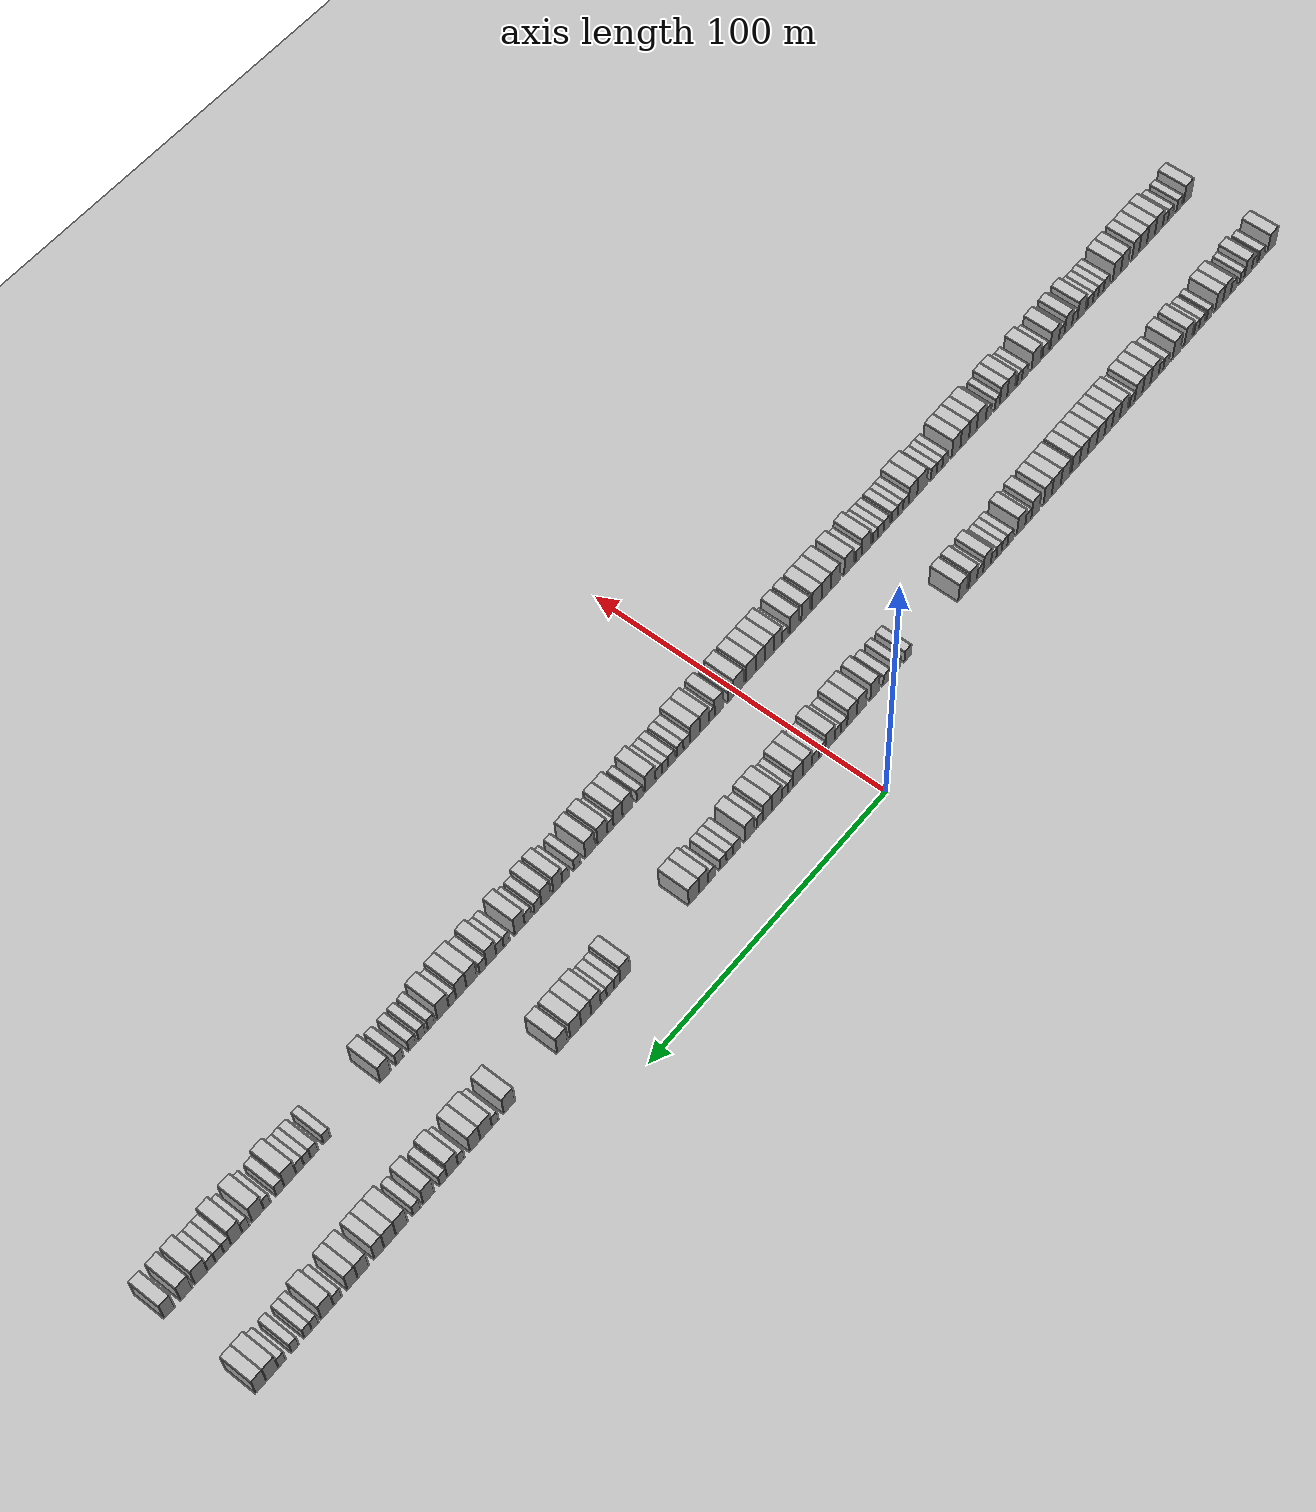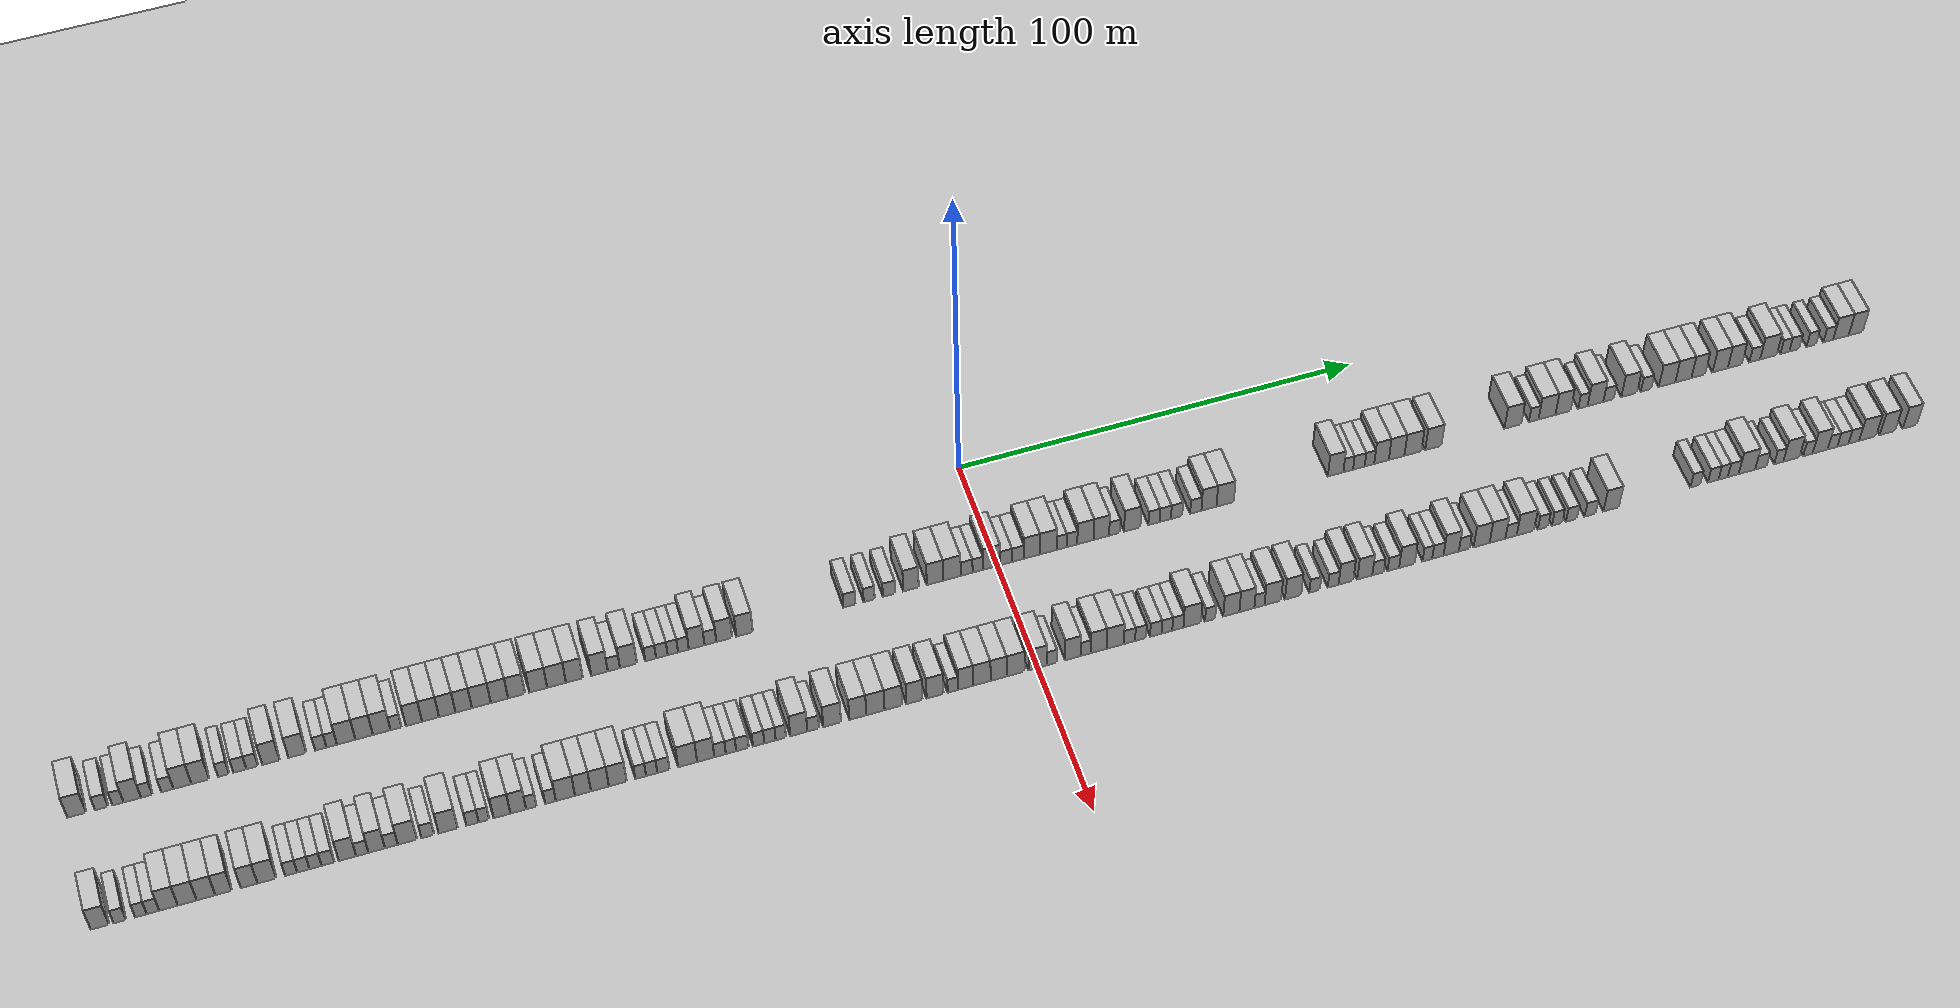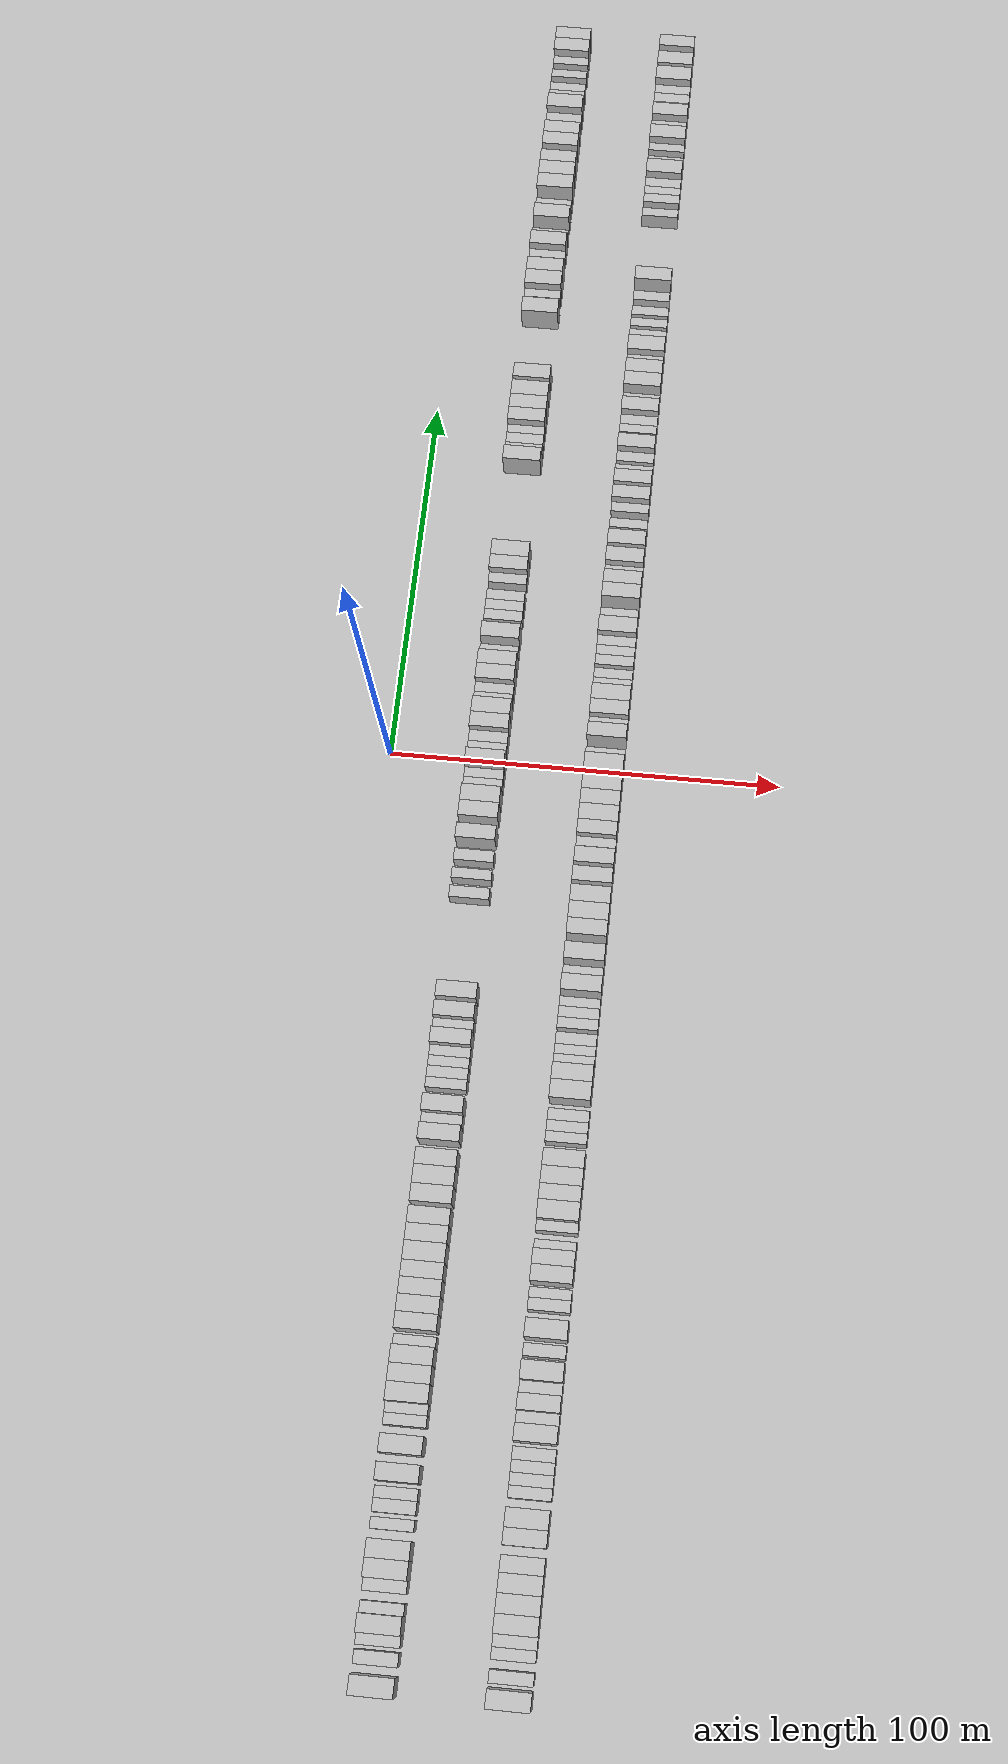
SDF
<?xml version="1.0" encoding="utf-8"?>

<sdf version="1.6">

   <world name="default">

      <gui fullscreen="0">

         <camera name="user_camera">

            <pose>-15 0 4.57585 0 0 0</pose>

            <view_controller>orbit</view_controller>

         </camera>

      </gui>

      <scene>

         <sky>

           <clouds>

             <speed>12</speed>

           </clouds>

         </sky>

         <ambient>0.4 0.4 0.4 1</ambient>

         <background>0.7 0.7 0.7 1</background>

         <shadows>1</shadows>

      </scene>

      <gravity>0 0 -9.8066</gravity>

      <magnetic_field>6e-06 2.3e-05 -4.2e-05</magnetic_field>

      <physics default="0" name="default_physics" type="ode">

         <ode>

            <solver>

               <type>quick</type>

               <iters>10</iters>

               <sor>1.0</sor>

               <use_dynamic_moi_rescaling>0</use_dynamic_moi_rescaling>

            </solver>

            <constraints>

               <cfm>0</cfm>

               <erp>0.2</erp>

               <contact_max_correcting_vel>100</contact_max_correcting_vel>

               <contact_surface_layer>0.001</contact_surface_layer>

            </constraints>

         </ode>

         <max_step_size>0.004</max_step_size>

         <real_time_factor>1</real_time_factor>

         <real_time_update_rate>250</real_time_update_rate>

      </physics>

      <light name="sun" type="directional">

         <cast_shadows>1</cast_shadows>

         <pose>0 0 10 0 0 0</pose>

         <diffuse>0.8 0.8 0.8 1</diffuse>

         <specular>0.2 0.2 0.2 1</specular>

         <attenuation>

            <range>1000</range>

            <constant>0.9</constant>

            <linear>0.01</linear>

            <quadratic>0.001</quadratic>

         </attenuation>

         <direction>-0.5 0.1 -0.9</direction>

      </light>

      <include>

         <name>ground_plane_1</name>

         <uri>model://HANNAS_ground_plane</uri>

         <pose>0 0 0  0 0 0</pose>

      </include>

      <include>

         <name>ground_plane_2</name>

         <uri>model://HANNAS_ground_plane</uri>

         <pose>100 0 0  0 0 0</pose>

      </include>

      <model name="building_1">

         <static>1</static>

         <pose frame="">25.0000 -217.8745 0 0.000000 0.000000 0.000000</pose>

         <link name="link">

            <pose frame="">0 0 4.50 0 0 0</pose>

            <collision name="collision">

               <geometry>

                  <box>

                     <size>10.0000 4.2509 9.0000</size>

                  </box>

               </geometry>

               <max_contacts>10</max_contacts>

               <surface>

                  <contact>

                     <ode/>

                  </contact>

                  <bounce/>

                  <friction>

                     <torsional>

                        <ode/>

                     </torsional>

                     <ode/>

                  </friction>

               </surface>

            </collision>

            <visual name="visual">

               <cast_shadows>0</cast_shadows>

               <geometry>

                  <box>

                     <size>10.0000 4.2509 9.0000</size>

                  </box>

               </geometry>

               <material>

                  <script>

                     <uri>model://HANNAS_wall/materials/scripts</uri>

                     <uri>model://HANNAS_wall/materials/textures</uri>

                     <name>vrc/HANNAS_wall</name>

                  </script>

               </material>

            </visual>

            <self_collide>0</self_collide>

            <enable_wind>0</enable_wind>

            <kinematic>0</kinematic>

         </link>

      </model>

      <model name="building_2">

         <static>1</static>

         <pose frame="">25.0000 -212.2686 0 0.000000 0.000000 0.000000</pose>

         <link name="link">

            <pose frame="">0 0 3.00 0 0 0</pose>

            <collision name="collision">

               <geometry>

                  <box>

                     <size>10.0000 2.9609 6.0000</size>

                  </box>

               </geometry>

               <max_contacts>10</max_contacts>

               <surface>

                  <contact>

                     <ode/>

                  </contact>

                  <bounce/>

                  <friction>

                     <torsional>

                        <ode/>

                     </torsional>

                     <ode/>

                  </friction>

               </surface>

            </collision>

            <visual name="visual">

               <cast_shadows>0</cast_shadows>

               <geometry>

                  <box>

                     <size>10.0000 2.9609 6.0000</size>

                  </box>

               </geometry>

               <material>

                  <script>

                     <uri>model://HANNAS_wall/materials/scripts</uri>

                     <uri>model://HANNAS_wall/materials/textures</uri>

                     <name>vrc/HANNAS_wall</name>

                  </script>

               </material>

            </visual>

            <self_collide>0</self_collide>

            <enable_wind>0</enable_wind>

            <kinematic>0</kinematic>

         </link>

      </model>

      <model name="building_3">

         <static>1</static>

         <pose frame="">25.0000 -208.5270 0 0.000000 0.000000 0.000000</pose>

         <link name="link">

            <pose frame="">0 0 3.00 0 0 0</pose>

            <collision name="collision">

               <geometry>

                  <box>

                     <size>10.0000 2.5222 6.0000</size>

                  </box>

               </geometry>

               <max_contacts>10</max_contacts>

               <surface>

                  <contact>

                     <ode/>

                  </contact>

                  <bounce/>

                  <friction>

                     <torsional>

                        <ode/>

                     </torsional>

                     <ode/>

                  </friction>

               </surface>

            </collision>

            <visual name="visual">

               <cast_shadows>0</cast_shadows>

               <geometry>

                  <box>

                     <size>10.0000 2.5222 6.0000</size>

                  </box>

               </geometry>

               <material>

                  <script>

                     <uri>model://HANNAS_wall/materials/scripts</uri>

                     <uri>model://HANNAS_wall/materials/textures</uri>

                     <name>vrc/HANNAS_wall</name>

                  </script>

               </material>

            </visual>

            <self_collide>0</self_collide>

            <enable_wind>0</enable_wind>

            <kinematic>0</kinematic>

         </link>

      </model>

      <model name="building_4">

         <static>1</static>

         <pose frame="">25.0000 -205.2757 0 0.000000 0.000000 0.000000</pose>

         <link name="link">

            <pose frame="">0 0 4.50 0 0 0</pose>

            <collision name="collision">

               <geometry>

                  <box>

                     <size>10.0000 3.9805 9.0000</size>

                  </box>

               </geometry>

               <max_contacts>10</max_contacts>

               <surface>

                  <contact>

                     <ode/>

                  </contact>

                  <bounce/>

                  <friction>

                     <torsional>

                        <ode/>

                     </torsional>

                     <ode/>

                  </friction>

               </surface>

            </collision>

            <visual name="visual">

               <cast_shadows>0</cast_shadows>

               <geometry>

                  <box>

                     <size>10.0000 3.9805 9.0000</size>

                  </box>

               </geometry>

               <material>

                  <script>

                     <uri>model://HANNAS_wall/materials/scripts</uri>

                     <uri>model://HANNAS_wall/materials/textures</uri>

                     <name>vrc/HANNAS_wall</name>

                  </script>

               </material>

            </visual>

            <self_collide>0</self_collide>

            <enable_wind>0</enable_wind>

            <kinematic>0</kinematic>

         </link>

      </model>

      <model name="building_5">

         <static>1</static>

         <pose frame="">25.0000 -202.0053 0 0.000000 0.000000 0.000000</pose>

         <link name="link">

            <pose frame="">0 0 3.00 0 0 0</pose>

            <collision name="collision">

               <geometry>

                  <box>

                     <size>10.0000 2.5604 6.0000</size>

                  </box>

               </geometry>

               <max_contacts>10</max_contacts>

               <surface>

                  <contact>

                     <ode/>

                  </contact>

                  <bounce/>

                  <friction>

                     <torsional>

                        <ode/>

                     </torsional>

                     <ode/>

                  </friction>

               </surface>

            </collision>

            <visual name="visual">

               <cast_shadows>0</cast_shadows>

               <geometry>

                  <box>

                     <size>10.0000 2.5604 6.0000</size>

                  </box>

               </geometry>

               <material>

                  <script>

                     <uri>model://HANNAS_wall/materials/scripts</uri>

                     <uri>model://HANNAS_wall/materials/textures</uri>

                     <name>vrc/HANNAS_wall</name>

                  </script>

               </material>

            </visual>

            <self_collide>0</self_collide>

            <enable_wind>0</enable_wind>

            <kinematic>0</kinematic>

         </link>

      </model>

      <model name="building_6">

         <static>1</static>

         <pose frame="">25.0000 -197.3337 0 0.000000 0.000000 0.000000</pose>

         <link name="link">

            <pose frame="">0 0 3.00 0 0 0</pose>

            <collision name="collision">

               <geometry>

                  <box>

                     <size>10.0000 2.7827 6.0000</size>

                  </box>

               </geometry>

               <max_contacts>10</max_contacts>

               <surface>

                  <contact>

                     <ode/>

                  </contact>

                  <bounce/>

                  <friction>

                     <torsional>

                        <ode/>

                     </torsional>

                     <ode/>

                  </friction>

               </surface>

            </collision>

            <visual name="visual">

               <cast_shadows>0</cast_shadows>

               <geometry>

                  <box>

                     <size>10.0000 2.7827 6.0000</size>

                  </box>

               </geometry>

               <material>

                  <script>

                     <uri>model://HANNAS_wall/materials/scripts</uri>

                     <uri>model://HANNAS_wall/materials/textures</uri>

                     <name>vrc/HANNAS_wall</name>

                  </script>

               </material>

            </visual>

            <self_collide>0</self_collide>

            <enable_wind>0</enable_wind>

            <kinematic>0</kinematic>

         </link>

      </model>

      <model name="building_7">

         <static>1</static>

         <pose frame="">25.0000 -193.8902 0 0.000000 0.000000 0.000000</pose>

         <link name="link">

            <pose frame="">0 0 4.50 0 0 0</pose>

            <collision name="collision">

               <geometry>

                  <box>

                     <size>10.0000 4.1044 9.0000</size>

                  </box>

               </geometry>

               <max_contacts>10</max_contacts>

               <surface>

                  <contact>

                     <ode/>

                  </contact>

                  <bounce/>

                  <friction>

                     <torsional>

                        <ode/>

                     </torsional>

                     <ode/>

                  </friction>

               </surface>

            </collision>

            <visual name="visual">

               <cast_shadows>0</cast_shadows>

               <geometry>

                  <box>

                     <size>10.0000 4.1044 9.0000</size>

                  </box>

               </geometry>

               <material>

                  <script>

                     <uri>model://HANNAS_wall/materials/scripts</uri>

                     <uri>model://HANNAS_wall/materials/textures</uri>

                     <name>vrc/HANNAS_wall</name>

                  </script>

               </material>

            </visual>

            <self_collide>0</self_collide>

            <enable_wind>0</enable_wind>

            <kinematic>0</kinematic>

         </link>

      </model>

      <model name="building_8">

         <static>1</static>

         <pose frame="">25.0000 -189.8039 0 0.000000 0.000000 0.000000</pose>

         <link name="link">

            <pose frame="">0 0 4.50 0 0 0</pose>

            <collision name="collision">

               <geometry>

                  <box>

                     <size>10.0000 4.0681 9.0000</size>

                  </box>

               </geometry>

               <max_contacts>10</max_contacts>

               <surface>

                  <contact>

                     <ode/>

                  </contact>

                  <bounce/>

                  <friction>

                     <torsional>

                        <ode/>

                     </torsional>

                     <ode/>

                  </friction>

               </surface>

            </collision>

            <visual name="visual">

               <cast_shadows>0</cast_shadows>

               <geometry>

                  <box>

                     <size>10.0000 4.0681 9.0000</size>

                  </box>

               </geometry>

               <material>

                  <script>

                     <uri>model://HANNAS_wall/materials/scripts</uri>

                     <uri>model://HANNAS_wall/materials/textures</uri>

                     <name>vrc/HANNAS_wall</name>

                  </script>

               </material>

            </visual>

            <self_collide>0</self_collide>

            <enable_wind>0</enable_wind>

            <kinematic>0</kinematic>

         </link>

      </model>

      <model name="building_9">

         <static>1</static>

         <pose frame="">25.0000 -184.4945 0 0.000000 0.000000 0.000000</pose>

         <link name="link">

            <pose frame="">0 0 3.00 0 0 0</pose>

            <collision name="collision">

               <geometry>

                  <box>

                     <size>10.0000 2.5507 6.0000</size>

                  </box>

               </geometry>

               <max_contacts>10</max_contacts>

               <surface>

                  <contact>

                     <ode/>

                  </contact>

                  <bounce/>

                  <friction>

                     <torsional>

                        <ode/>

                     </torsional>

                     <ode/>

                  </friction>

               </surface>

            </collision>

            <visual name="visual">

               <cast_shadows>0</cast_shadows>

               <geometry>

                  <box>

                     <size>10.0000 2.5507 6.0000</size>

                  </box>

               </geometry>

               <material>

                  <script>

                     <uri>model://HANNAS_wall/materials/scripts</uri>

                     <uri>model://HANNAS_wall/materials/textures</uri>

                     <name>vrc/HANNAS_wall</name>

                  </script>

               </material>

            </visual>

            <self_collide>0</self_collide>

            <enable_wind>0</enable_wind>

            <kinematic>0</kinematic>

         </link>

      </model>

      <model name="building_10">

         <static>1</static>

         <pose frame="">25.0000 -180.7242 0 0.000000 0.000000 0.000000</pose>

         <link name="link">

            <pose frame="">0 0 3.00 0 0 0</pose>

            <collision name="collision">

               <geometry>

                  <box>

                     <size>10.0000 2.9899 6.0000</size>

                  </box>

               </geometry>

               <max_contacts>10</max_contacts>

               <surface>

                  <contact>

                     <ode/>

                  </contact>

                  <bounce/>

                  <friction>

                     <torsional>

                        <ode/>

                     </torsional>

                     <ode/>

                  </friction>

               </surface>

            </collision>

            <visual name="visual">

               <cast_shadows>0</cast_shadows>

               <geometry>

                  <box>

                     <size>10.0000 2.9899 6.0000</size>

                  </box>

               </geometry>

               <material>

                  <script>

                     <uri>model://HANNAS_wall/materials/scripts</uri>

                     <uri>model://HANNAS_wall/materials/textures</uri>

                     <name>vrc/HANNAS_wall</name>

                  </script>

               </material>

            </visual>

            <self_collide>0</self_collide>

            <enable_wind>0</enable_wind>

            <kinematic>0</kinematic>

         </link>

      </model>

      <model name="building_11">

         <static>1</static>

         <pose frame="">25.0000 -177.8999 0 0.000000 0.000000 0.000000</pose>

         <link name="link">

            <pose frame="">0 0 3.00 0 0 0</pose>

            <collision name="collision">

               <geometry>

                  <box>

                     <size>10.0000 2.6587 6.0000</size>

                  </box>

               </geometry>

               <max_contacts>10</max_contacts>

               <surface>

                  <contact>

                     <ode/>

                  </contact>

                  <bounce/>

                  <friction>

                     <torsional>

                        <ode/>

                     </torsional>

                     <ode/>

                  </friction>

               </surface>

            </collision>

            <visual name="visual">

               <cast_shadows>0</cast_shadows>

               <geometry>

                  <box>

                     <size>10.0000 2.6587 6.0000</size>

                  </box>

               </geometry>

               <material>

                  <script>

                     <uri>model://HANNAS_wall/materials/scripts</uri>

                     <uri>model://HANNAS_wall/materials/textures</uri>

                     <name>vrc/HANNAS_wall</name>

                  </script>

               </material>

            </visual>

            <self_collide>0</self_collide>

            <enable_wind>0</enable_wind>

            <kinematic>0</kinematic>

         </link>

      </model>

      <model name="building_12">

         <static>1</static>

         <pose frame="">25.0000 -173.5764 0 0.000000 0.000000 0.000000</pose>

         <link name="link">

            <pose frame="">0 0 4.50 0 0 0</pose>

            <collision name="collision">

               <geometry>

                  <box>

                     <size>10.0000 3.9884 9.0000</size>

                  </box>

               </geometry>

               <max_contacts>10</max_contacts>

               <surface>

                  <contact>

                     <ode/>

                  </contact>

                  <bounce/>

                  <friction>

                     <torsional>

                        <ode/>

                     </torsional>

                     <ode/>

                  </friction>

               </surface>

            </collision>

            <visual name="visual">

               <cast_shadows>0</cast_shadows>

               <geometry>

                  <box>

                     <size>10.0000 3.9884 9.0000</size>

                  </box>

               </geometry>

               <material>

                  <script>

                     <uri>model://HANNAS_wall/materials/scripts</uri>

                     <uri>model://HANNAS_wall/materials/textures</uri>

                     <name>vrc/HANNAS_wall</name>

                  </script>

               </material>

            </visual>

            <self_collide>0</self_collide>

            <enable_wind>0</enable_wind>

            <kinematic>0</kinematic>

         </link>

      </model>

      <model name="building_13">

         <static>1</static>

         <pose frame="">25.0000 -167.5079 0 0.000000 0.000000 0.000000</pose>

         <link name="link">

            <pose frame="">0 0 4.50 0 0 0</pose>

            <collision name="collision">

               <geometry>

                  <box>

                     <size>10.0000 4.1485 9.0000</size>

                  </box>

               </geometry>

               <max_contacts>10</max_contacts>

               <surface>

                  <contact>

                     <ode/>

                  </contact>

                  <bounce/>

                  <friction>

                     <torsional>

                        <ode/>

                     </torsional>

                     <ode/>

                  </friction>

               </surface>

            </collision>

            <visual name="visual">

               <cast_shadows>0</cast_shadows>

               <geometry>

                  <box>

                     <size>10.0000 4.1485 9.0000</size>

                  </box>

               </geometry>

               <material>

                  <script>

                     <uri>model://HANNAS_wall/materials/scripts</uri>

                     <uri>model://HANNAS_wall/materials/textures</uri>

                     <name>vrc/HANNAS_wall</name>

                  </script>

               </material>

            </visual>

            <self_collide>0</self_collide>

            <enable_wind>0</enable_wind>

            <kinematic>0</kinematic>

         </link>

      </model>

      <model name="building_14">

         <static>1</static>

         <pose frame="">25.0000 -162.1096 0 0.000000 0.000000 0.000000</pose>

         <link name="link">

            <pose frame="">0 0 3.00 0 0 0</pose>

            <collision name="collision">

               <geometry>

                  <box>

                     <size>10.0000 2.6481 6.0000</size>

                  </box>

               </geometry>

               <max_contacts>10</max_contacts>

               <surface>

                  <contact>

                     <ode/>

                  </contact>

                  <bounce/>

                  <friction>

                     <torsional>

                        <ode/>

                     </torsional>

                     <ode/>

                  </friction>

               </surface>

            </collision>

            <visual name="visual">

               <cast_shadows>0</cast_shadows>

               <geometry>

                  <box>

                     <size>10.0000 2.6481 6.0000</size>

                  </box>

               </geometry>

               <material>

                  <script>

                     <uri>model://HANNAS_wall/materials/scripts</uri>

                     <uri>model://HANNAS_wall/materials/textures</uri>

                     <name>vrc/HANNAS_wall</name>

                  </script>

               </material>

            </visual>

            <self_collide>0</self_collide>

            <enable_wind>0</enable_wind>

            <kinematic>0</kinematic>

         </link>

      </model>

      <model name="building_15">

         <static>1</static>

         <pose frame="">25.0000 -159.5720 0 0.000000 0.000000 0.000000</pose>

         <link name="link">

            <pose frame="">0 0 3.00 0 0 0</pose>

            <collision name="collision">

               <geometry>

                  <box>

                     <size>10.0000 2.4272 6.0000</size>

                  </box>

               </geometry>

               <max_contacts>10</max_contacts>

               <surface>

                  <contact>

                     <ode/>

                  </contact>

                  <bounce/>

                  <friction>

                     <torsional>

                        <ode/>

                     </torsional>

                     <ode/>

                  </friction>

               </surface>

            </collision>

            <visual name="visual">

               <cast_shadows>0</cast_shadows>

               <geometry>

                  <box>

                     <size>10.0000 2.4272 6.0000</size>

                  </box>

               </geometry>

               <material>

                  <script>

                     <uri>model://HANNAS_wall/materials/scripts</uri>

                     <uri>model://HANNAS_wall/materials/textures</uri>

                     <name>vrc/HANNAS_wall</name>

                  </script>

               </material>

            </visual>

            <self_collide>0</self_collide>

            <enable_wind>0</enable_wind>

            <kinematic>0</kinematic>

         </link>

      </model>

      <model name="building_16">

         <static>1</static>

         <pose frame="">25.0000 -156.2153 0 0.000000 0.000000 0.000000</pose>

         <link name="link">

            <pose frame="">0 0 4.50 0 0 0</pose>

            <collision name="collision">

               <geometry>

                  <box>

                     <size>10.0000 4.2861 9.0000</size>

                  </box>

               </geometry>

               <max_contacts>10</max_contacts>

               <surface>

                  <contact>

                     <ode/>

                  </contact>

                  <bounce/>

                  <friction>

                     <torsional>

                        <ode/>

                     </torsional>

                     <ode/>

                  </friction>

               </surface>

            </collision>

            <visual name="visual">

               <cast_shadows>0</cast_shadows>

               <geometry>

                  <box>

                     <size>10.0000 4.2861 9.0000</size>

                  </box>

               </geometry>

               <material>

                  <script>

                     <uri>model://HANNAS_wall/materials/scripts</uri>

                     <uri>model://HANNAS_wall/materials/textures</uri>

                     <name>vrc/HANNAS_wall</name>

                  </script>

               </material>

            </visual>

            <self_collide>0</self_collide>

            <enable_wind>0</enable_wind>

            <kinematic>0</kinematic>

         </link>

      </model>

      <model name="building_17">

         <static>1</static>

         <pose frame="">25.0000 -152.0414 0 0.000000 0.000000 0.000000</pose>

         <link name="link">

            <pose frame="">0 0 4.50 0 0 0</pose>

            <collision name="collision">

               <geometry>

                  <box>

                     <size>10.0000 4.0616 9.0000</size>

                  </box>

               </geometry>

               <max_contacts>10</max_contacts>

               <surface>

                  <contact>

                     <ode/>

                  </contact>

                  <bounce/>

                  <friction>

                     <torsional>

                        <ode/>

                     </torsional>

                     <ode/>

                  </friction>

               </surface>

            </collision>

            <visual name="visual">

               <cast_shadows>0</cast_shadows>

               <geometry>

                  <box>

                     <size>10.0000 4.0616 9.0000</size>

                  </box>

               </geometry>

               <material>

                  <script>

                     <uri>model://HANNAS_wall/materials/scripts</uri>

                     <uri>model://HANNAS_wall/materials/textures</uri>

                     <name>vrc/HANNAS_wall</name>

                  </script>

               </material>

            </visual>

            <self_collide>0</self_collide>

            <enable_wind>0</enable_wind>

            <kinematic>0</kinematic>

         </link>

      </model>

      <model name="building_18">

         <static>1</static>

         <pose frame="">25.0000 -147.9637 0 0.000000 0.000000 0.000000</pose>

         <link name="link">

            <pose frame="">0 0 4.50 0 0 0</pose>

            <collision name="collision">

               <geometry>

                  <box>

                     <size>10.0000 4.0940 9.0000</size>

                  </box>

               </geometry>

               <max_contacts>10</max_contacts>

               <surface>

                  <contact>

                     <ode/>

                  </contact>

                  <bounce/>

                  <friction>

                     <torsional>

                        <ode/>

                     </torsional>

                     <ode/>

                  </friction>

               </surface>

            </collision>

            <visual name="visual">

               <cast_shadows>0</cast_shadows>

               <geometry>

                  <box>

                     <size>10.0000 4.0940 9.0000</size>

                  </box>

               </geometry>

               <material>

                  <script>

                     <uri>model://HANNAS_wall/materials/scripts</uri>

                     <uri>model://HANNAS_wall/materials/textures</uri>

                     <name>vrc/HANNAS_wall</name>

                  </script>

               </material>

            </visual>

            <self_collide>0</self_collide>

            <enable_wind>0</enable_wind>

            <kinematic>0</kinematic>

         </link>

      </model>

      <model name="building_19">

         <static>1</static>

         <pose frame="">25.0000 -144.6385 0 0.000000 0.000000 0.000000</pose>

         <link name="link">

            <pose frame="">0 0 3.00 0 0 0</pose>

            <collision name="collision">

               <geometry>

                  <box>

                     <size>10.0000 2.5564 6.0000</size>

                  </box>

               </geometry>

               <max_contacts>10</max_contacts>

               <surface>

                  <contact>

                     <ode/>

                  </contact>

                  <bounce/>

                  <friction>

                     <torsional>

                        <ode/>

                     </torsional>

                     <ode/>

                  </friction>

               </surface>

            </collision>

            <visual name="visual">

               <cast_shadows>0</cast_shadows>

               <geometry>

                  <box>

                     <size>10.0000 2.5564 6.0000</size>

                  </box>

               </geometry>

               <material>

                  <script>

                     <uri>model://HANNAS_wall/materials/scripts</uri>

                     <uri>model://HANNAS_wall/materials/textures</uri>

                     <name>vrc/HANNAS_wall</name>

                  </script>

               </material>

            </visual>

            <self_collide>0</self_collide>

            <enable_wind>0</enable_wind>

            <kinematic>0</kinematic>

         </link>

      </model>

      <model name="building_20">

         <static>1</static>

         <pose frame="">25.0000 -140.4562 0 0.000000 0.000000 0.000000</pose>

         <link name="link">

            <pose frame="">0 0 4.50 0 0 0</pose>

            <collision name="collision">

               <geometry>

                  <box>

                     <size>10.0000 3.8082 9.0000</size>

                  </box>

               </geometry>

               <max_contacts>10</max_contacts>

               <surface>

                  <contact>

                     <ode/>

                  </contact>

                  <bounce/>

                  <friction>

                     <torsional>

                        <ode/>

                     </torsional>

                     <ode/>

                  </friction>

               </surface>

            </collision>

            <visual name="visual">

               <cast_shadows>0</cast_shadows>

               <geometry>

                  <box>

                     <size>10.0000 3.8082 9.0000</size>

                  </box>

               </geometry>

               <material>

                  <script>

                     <uri>model://HANNAS_wall/materials/scripts</uri>

                     <uri>model://HANNAS_wall/materials/textures</uri>

                     <name>vrc/HANNAS_wall</name>

                  </script>

               </material>

            </visual>

            <self_collide>0</self_collide>

            <enable_wind>0</enable_wind>

            <kinematic>0</kinematic>

         </link>

      </model>

      <model name="building_21">

         <static>1</static>

         <pose frame="">25.0000 -136.5784 0 0.000000 0.000000 0.000000</pose>

         <link name="link">

            <pose frame="">0 0 4.50 0 0 0</pose>

            <collision name="collision">

               <geometry>

                  <box>

                     <size>10.0000 3.9473 9.0000</size>

                  </box>

               </geometry>

               <max_contacts>10</max_contacts>

               <surface>

                  <contact>

                     <ode/>

                  </contact>

                  <bounce/>

                  <friction>

                     <torsional>

                        <ode/>

                     </torsional>

                     <ode/>

                  </friction>

               </surface>

            </collision>

            <visual name="visual">

               <cast_shadows>0</cast_shadows>

               <geometry>

                  <box>

                     <size>10.0000 3.9473 9.0000</size>

                  </box>

               </geometry>

               <material>

                  <script>

                     <uri>model://HANNAS_wall/materials/scripts</uri>

                     <uri>model://HANNAS_wall/materials/textures</uri>

                     <name>vrc/HANNAS_wall</name>

                  </script>

               </material>

            </visual>

            <self_collide>0</self_collide>

            <enable_wind>0</enable_wind>

            <kinematic>0</kinematic>

         </link>

      </model>

      <model name="building_22">

         <static>1</static>

         <pose frame="">25.0000 -132.6678 0 0.000000 0.000000 0.000000</pose>

         <link name="link">

            <pose frame="">0 0 4.50 0 0 0</pose>

            <collision name="collision">

               <geometry>

                  <box>

                     <size>10.0000 3.8739 9.0000</size>

                  </box>

               </geometry>

               <max_contacts>10</max_contacts>

               <surface>

                  <contact>

                     <ode/>

                  </contact>

                  <bounce/>

                  <friction>

                     <torsional>

                        <ode/>

                     </torsional>

                     <ode/>

                  </friction>

               </surface>

            </collision>

            <visual name="visual">

               <cast_shadows>0</cast_shadows>

               <geometry>

                  <box>

                     <size>10.0000 3.8739 9.0000</size>

                  </box>

               </geometry>

               <material>

                  <script>

                     <uri>model://HANNAS_wall/materials/scripts</uri>

                     <uri>model://HANNAS_wall/materials/textures</uri>

                     <name>vrc/HANNAS_wall</name>

                  </script>

               </material>

            </visual>

            <self_collide>0</self_collide>

            <enable_wind>0</enable_wind>

            <kinematic>0</kinematic>

         </link>

      </model>

      <model name="building_23">

         <static>1</static>

         <pose frame="">25.0000 -128.8086 0 0.000000 0.000000 0.000000</pose>

         <link name="link">

            <pose frame="">0 0 4.50 0 0 0</pose>

            <collision name="collision">

               <geometry>

                  <box>

                     <size>10.0000 3.8445 9.0000</size>

                  </box>

               </geometry>

               <max_contacts>10</max_contacts>

               <surface>

                  <contact>

                     <ode/>

                  </contact>

                  <bounce/>

                  <friction>

                     <torsional>

                        <ode/>

                     </torsional>

                     <ode/>

                  </friction>

               </surface>

            </collision>

            <visual name="visual">

               <cast_shadows>0</cast_shadows>

               <geometry>

                  <box>

                     <size>10.0000 3.8445 9.0000</size>

                  </box>

               </geometry>

               <material>

                  <script>

                     <uri>model://HANNAS_wall/materials/scripts</uri>

                     <uri>model://HANNAS_wall/materials/textures</uri>

                     <name>vrc/HANNAS_wall</name>

                  </script>

               </material>

            </visual>

            <self_collide>0</self_collide>

            <enable_wind>0</enable_wind>

            <kinematic>0</kinematic>

         </link>

      </model>

      <model name="building_24">

         <static>1</static>

         <pose frame="">25.0000 -124.6665 0 0.000000 0.000000 0.000000</pose>

         <link name="link">

            <pose frame="">0 0 4.50 0 0 0</pose>

            <collision name="collision">

               <geometry>

                  <box>

                     <size>10.0000 4.4397 9.0000</size>

                  </box>

               </geometry>

               <max_contacts>10</max_contacts>

               <surface>

                  <contact>

                     <ode/>

                  </contact>

                  <bounce/>

                  <friction>

                     <torsional>

                        <ode/>

                     </torsional>

                     <ode/>

                  </friction>

               </surface>

            </collision>

            <visual name="visual">

               <cast_shadows>0</cast_shadows>

               <geometry>

                  <box>

                     <size>10.0000 4.4397 9.0000</size>

                  </box>

               </geometry>

               <material>

                  <script>

                     <uri>model://HANNAS_wall/materials/scripts</uri>

                     <uri>model://HANNAS_wall/materials/textures</uri>

                     <name>vrc/HANNAS_wall</name>

                  </script>

               </material>

            </visual>

            <self_collide>0</self_collide>

            <enable_wind>0</enable_wind>

            <kinematic>0</kinematic>

         </link>

      </model>

      <model name="building_25">

         <static>1</static>

         <pose frame="">25.0000 -120.4193 0 0.000000 0.000000 0.000000</pose>

         <link name="link">

            <pose frame="">0 0 4.50 0 0 0</pose>

            <collision name="collision">

               <geometry>

                  <box>

                     <size>10.0000 4.0547 9.0000</size>

                  </box>

               </geometry>

               <max_contacts>10</max_contacts>

               <surface>

                  <contact>

                     <ode/>

                  </contact>

                  <bounce/>

                  <friction>

                     <torsional>

                        <ode/>

                     </torsional>

                     <ode/>

                  </friction>

               </surface>

            </collision>

            <visual name="visual">

               <cast_shadows>0</cast_shadows>

               <geometry>

                  <box>

                     <size>10.0000 4.0547 9.0000</size>

                  </box>

               </geometry>

               <material>

                  <script>

                     <uri>model://HANNAS_wall/materials/scripts</uri>

                     <uri>model://HANNAS_wall/materials/textures</uri>

                     <name>vrc/HANNAS_wall</name>

                  </script>

               </material>

            </visual>

            <self_collide>0</self_collide>

            <enable_wind>0</enable_wind>

            <kinematic>0</kinematic>

         </link>

      </model>

      <model name="building_26">

         <static>1</static>

         <pose frame="">25.0000 -116.3784 0 0.000000 0.000000 0.000000</pose>

         <link name="link">

            <pose frame="">0 0 4.50 0 0 0</pose>

            <collision name="collision">

               <geometry>

                  <box>

                     <size>10.0000 4.0271 9.0000</size>

                  </box>

               </geometry>

               <max_contacts>10</max_contacts>

               <surface>

                  <contact>

                     <ode/>

                  </contact>

                  <bounce/>

                  <friction>

                     <torsional>

                        <ode/>

                     </torsional>

                     <ode/>

                  </friction>

               </surface>

            </collision>

            <visual name="visual">

               <cast_shadows>0</cast_shadows>

               <geometry>

                  <box>

                     <size>10.0000 4.0271 9.0000</size>

                  </box>

               </geometry>

               <material>

                  <script>

                     <uri>model://HANNAS_wall/materials/scripts</uri>

                     <uri>model://HANNAS_wall/materials/textures</uri>

                     <name>vrc/HANNAS_wall</name>

                  </script>

               </material>

            </visual>

            <self_collide>0</self_collide>

            <enable_wind>0</enable_wind>

            <kinematic>0</kinematic>

         </link>

      </model>

      <model name="building_27">

         <static>1</static>

         <pose frame="">25.0000 -111.2638 0 0.000000 0.000000 0.000000</pose>

         <link name="link">

            <pose frame="">0 0 4.50 0 0 0</pose>

            <collision name="collision">

               <geometry>

                  <box>

                     <size>10.0000 4.2020 9.0000</size>

                  </box>

               </geometry>

               <max_contacts>10</max_contacts>

               <surface>

                  <contact>

                     <ode/>

                  </contact>

                  <bounce/>

                  <friction>

                     <torsional>

                        <ode/>

                     </torsional>

                     <ode/>

                  </friction>

               </surface>

            </collision>

            <visual name="visual">

               <cast_shadows>0</cast_shadows>

               <geometry>

                  <box>

                     <size>10.0000 4.2020 9.0000</size>

                  </box>

               </geometry>

               <material>

                  <script>

                     <uri>model://HANNAS_wall/materials/scripts</uri>

                     <uri>model://HANNAS_wall/materials/textures</uri>

                     <name>vrc/HANNAS_wall</name>

                  </script>

               </material>

            </visual>

            <self_collide>0</self_collide>

            <enable_wind>0</enable_wind>

            <kinematic>0</kinematic>

         </link>

      </model>

      <model name="building_28">

         <static>1</static>

         <pose frame="">25.0000 -106.9423 0 0.000000 0.000000 0.000000</pose>

         <link name="link">

            <pose frame="">0 0 4.50 0 0 0</pose>

            <collision name="collision">

               <geometry>

                  <box>

                     <size>10.0000 4.4410 9.0000</size>

                  </box>

               </geometry>

               <max_contacts>10</max_contacts>

               <surface>

                  <contact>

                     <ode/>

                  </contact>

                  <bounce/>

                  <friction>

                     <torsional>

                        <ode/>

                     </torsional>

                     <ode/>

                  </friction>

               </surface>

            </collision>

            <visual name="visual">

               <cast_shadows>0</cast_shadows>

               <geometry>

                  <box>

                     <size>10.0000 4.4410 9.0000</size>

                  </box>

               </geometry>

               <material>

                  <script>

                     <uri>model://HANNAS_wall/materials/scripts</uri>

                     <uri>model://HANNAS_wall/materials/textures</uri>

                     <name>vrc/HANNAS_wall</name>

                  </script>

               </material>

            </visual>

            <self_collide>0</self_collide>

            <enable_wind>0</enable_wind>

            <kinematic>0</kinematic>

         </link>

      </model>

      <model name="building_29">

         <static>1</static>

         <pose frame="">25.0000 -102.7202 0 0.000000 0.000000 0.000000</pose>

         <link name="link">

            <pose frame="">0 0 4.50 0 0 0</pose>

            <collision name="collision">

               <geometry>

                  <box>

                     <size>10.0000 4.0032 9.0000</size>

                  </box>

               </geometry>

               <max_contacts>10</max_contacts>

               <surface>

                  <contact>

                     <ode/>

                  </contact>

                  <bounce/>

                  <friction>

                     <torsional>

                        <ode/>

                     </torsional>

                     <ode/>

                  </friction>

               </surface>

            </collision>

            <visual name="visual">

               <cast_shadows>0</cast_shadows>

               <geometry>

                  <box>

                     <size>10.0000 4.0032 9.0000</size>

                  </box>

               </geometry>

               <material>

                  <script>

                     <uri>model://HANNAS_wall/materials/scripts</uri>

                     <uri>model://HANNAS_wall/materials/textures</uri>

                     <name>vrc/HANNAS_wall</name>

                  </script>

               </material>

            </visual>

            <self_collide>0</self_collide>

            <enable_wind>0</enable_wind>

            <kinematic>0</kinematic>

         </link>

      </model>

      <model name="building_30">

         <static>1</static>

         <pose frame="">25.0000 -96.7549 0 0.000000 0.000000 0.000000</pose>

         <link name="link">

            <pose frame="">0 0 4.50 0 0 0</pose>

            <collision name="collision">

               <geometry>

                  <box>

                     <size>10.0000 3.9276 9.0000</size>

                  </box>

               </geometry>

               <max_contacts>10</max_contacts>

               <surface>

                  <contact>

                     <ode/>

                  </contact>

                  <bounce/>

                  <friction>

                     <torsional>

                        <ode/>

                     </torsional>

                     <ode/>

                  </friction>

               </surface>

            </collision>

            <visual name="visual">

               <cast_shadows>0</cast_shadows>

               <geometry>

                  <box>

                     <size>10.0000 3.9276 9.0000</size>

                  </box>

               </geometry>

               <material>

                  <script>

                     <uri>model://HANNAS_wall/materials/scripts</uri>

                     <uri>model://HANNAS_wall/materials/textures</uri>

                     <name>vrc/HANNAS_wall</name>

                  </script>

               </material>

            </visual>

            <self_collide>0</self_collide>

            <enable_wind>0</enable_wind>

            <kinematic>0</kinematic>

         </link>

      </model>

      <model name="building_31">

         <static>1</static>

         <pose frame="">25.0000 -93.3359 0 0.000000 0.000000 0.000000</pose>

         <link name="link">

            <pose frame="">0 0 3.00 0 0 0</pose>

            <collision name="collision">

               <geometry>

                  <box>

                     <size>10.0000 2.9104 6.0000</size>

                  </box>

               </geometry>

               <max_contacts>10</max_contacts>

               <surface>

                  <contact>

                     <ode/>

                  </contact>

                  <bounce/>

                  <friction>

                     <torsional>

                        <ode/>

                     </torsional>

                     <ode/>

                  </friction>

               </surface>

            </collision>

            <visual name="visual">

               <cast_shadows>0</cast_shadows>

               <geometry>

                  <box>

                     <size>10.0000 2.9104 6.0000</size>

                  </box>

               </geometry>

               <material>

                  <script>

                     <uri>model://HANNAS_wall/materials/scripts</uri>

                     <uri>model://HANNAS_wall/materials/textures</uri>

                     <name>vrc/HANNAS_wall</name>

                  </script>

               </material>

            </visual>

            <self_collide>0</self_collide>

            <enable_wind>0</enable_wind>

            <kinematic>0</kinematic>

         </link>

      </model>

      <model name="building_32">

         <static>1</static>

         <pose frame="">25.0000 -89.8623 0 0.000000 0.000000 0.000000</pose>

         <link name="link">

            <pose frame="">0 0 4.50 0 0 0</pose>

            <collision name="collision">

               <geometry>

                  <box>

                     <size>10.0000 4.0367 9.0000</size>

                  </box>

               </geometry>

               <max_contacts>10</max_contacts>

               <surface>

                  <contact>

                     <ode/>

                  </contact>

                  <bounce/>

                  <friction>

                     <torsional>

                        <ode/>

                     </torsional>

                     <ode/>

                  </friction>

               </surface>

            </collision>

            <visual name="visual">

               <cast_shadows>0</cast_shadows>

               <geometry>

                  <box>

                     <size>10.0000 4.0367 9.0000</size>

                  </box>

               </geometry>

               <material>

                  <script>

                     <uri>model://HANNAS_wall/materials/scripts</uri>

                     <uri>model://HANNAS_wall/materials/textures</uri>

                     <name>vrc/HANNAS_wall</name>

                  </script>

               </material>

            </visual>

            <self_collide>0</self_collide>

            <enable_wind>0</enable_wind>

            <kinematic>0</kinematic>

         </link>

      </model>

      <model name="building_33">

         <static>1</static>

         <pose frame="">25.0000 -84.5632 0 0.000000 0.000000 0.000000</pose>

         <link name="link">

            <pose frame="">0 0 3.00 0 0 0</pose>

            <collision name="collision">

               <geometry>

                  <box>

                     <size>10.0000 2.5615 6.0000</size>

                  </box>

               </geometry>

               <max_contacts>10</max_contacts>

               <surface>

                  <contact>

                     <ode/>

                  </contact>

                  <bounce/>

                  <friction>

                     <torsional>

                        <ode/>

                     </torsional>

                     <ode/>

                  </friction>

               </surface>

            </collision>

            <visual name="visual">

               <cast_shadows>0</cast_shadows>

               <geometry>

                  <box>

                     <size>10.0000 2.5615 6.0000</size>

                  </box>

               </geometry>

               <material>

                  <script>

                     <uri>model://HANNAS_wall/materials/scripts</uri>

                     <uri>model://HANNAS_wall/materials/textures</uri>

                     <name>vrc/HANNAS_wall</name>

                  </script>

               </material>

            </visual>

            <self_collide>0</self_collide>

            <enable_wind>0</enable_wind>

            <kinematic>0</kinematic>

         </link>

      </model>

      <model name="building_34">

         <static>1</static>

         <pose frame="">25.0000 -81.9005 0 0.000000 0.000000 0.000000</pose>

         <link name="link">

            <pose frame="">0 0 3.00 0 0 0</pose>

            <collision name="collision">

               <geometry>

                  <box>

                     <size>10.0000 2.7639 6.0000</size>

                  </box>

               </geometry>

               <max_contacts>10</max_contacts>

               <surface>

                  <contact>

                     <ode/>

                  </contact>

                  <bounce/>

                  <friction>

                     <torsional>

                        <ode/>

                     </torsional>

                     <ode/>

                  </friction>

               </surface>

            </collision>

            <visual name="visual">

               <cast_shadows>0</cast_shadows>

               <geometry>

                  <box>

                     <size>10.0000 2.7639 6.0000</size>

                  </box>

               </geometry>

               <material>

                  <script>

                     <uri>model://HANNAS_wall/materials/scripts</uri>

                     <uri>model://HANNAS_wall/materials/textures</uri>

                     <name>vrc/HANNAS_wall</name>

                  </script>

               </material>

            </visual>

            <self_collide>0</self_collide>

            <enable_wind>0</enable_wind>

            <kinematic>0</kinematic>

         </link>

      </model>

      <model name="building_35">

         <static>1</static>

         <pose frame="">25.0000 -79.2666 0 0.000000 0.000000 0.000000</pose>

         <link name="link">

            <pose frame="">0 0 3.00 0 0 0</pose>

            <collision name="collision">

               <geometry>

                  <box>

                     <size>10.0000 2.5040 6.0000</size>

                  </box>

               </geometry>

               <max_contacts>10</max_contacts>

               <surface>

                  <contact>

                     <ode/>

                  </contact>

                  <bounce/>

                  <friction>

                     <torsional>

                        <ode/>

                     </torsional>

                     <ode/>

                  </friction>

               </surface>

            </collision>

            <visual name="visual">

               <cast_shadows>0</cast_shadows>

               <geometry>

                  <box>

                     <size>10.0000 2.5040 6.0000</size>

                  </box>

               </geometry>

               <material>

                  <script>

                     <uri>model://HANNAS_wall/materials/scripts</uri>

                     <uri>model://HANNAS_wall/materials/textures</uri>

                     <name>vrc/HANNAS_wall</name>

                  </script>

               </material>

            </visual>

            <self_collide>0</self_collide>

            <enable_wind>0</enable_wind>

            <kinematic>0</kinematic>

         </link>

      </model>

      <model name="building_36">

         <static>1</static>

         <pose frame="">25.0000 -76.7242 0 0.000000 0.000000 0.000000</pose>

         <link name="link">

            <pose frame="">0 0 3.00 0 0 0</pose>

            <collision name="collision">

               <geometry>

                  <box>

                     <size>10.0000 2.5807 6.0000</size>

                  </box>

               </geometry>

               <max_contacts>10</max_contacts>

               <surface>

                  <contact>

                     <ode/>

                  </contact>

                  <bounce/>

                  <friction>

                     <torsional>

                        <ode/>

                     </torsional>

                     <ode/>

                  </friction>

               </surface>

            </collision>

            <visual name="visual">

               <cast_shadows>0</cast_shadows>

               <geometry>

                  <box>

                     <size>10.0000 2.5807 6.0000</size>

                  </box>

               </geometry>

               <material>

                  <script>

                     <uri>model://HANNAS_wall/materials/scripts</uri>

                     <uri>model://HANNAS_wall/materials/textures</uri>

                     <name>vrc/HANNAS_wall</name>

                  </script>

               </material>

            </visual>

            <self_collide>0</self_collide>

            <enable_wind>0</enable_wind>

            <kinematic>0</kinematic>

         </link>

      </model>

      <model name="building_37">

         <static>1</static>

         <pose frame="">25.0000 -73.5472 0 0.000000 0.000000 0.000000</pose>

         <link name="link">

            <pose frame="">0 0 4.50 0 0 0</pose>

            <collision name="collision">

               <geometry>

                  <box>

                     <size>10.0000 3.7734 9.0000</size>

                  </box>

               </geometry>

               <max_contacts>10</max_contacts>

               <surface>

                  <contact>

                     <ode/>

                  </contact>

                  <bounce/>

                  <friction>

                     <torsional>

                        <ode/>

                     </torsional>

                     <ode/>

                  </friction>

               </surface>

            </collision>

            <visual name="visual">

               <cast_shadows>0</cast_shadows>

               <geometry>

                  <box>

                     <size>10.0000 3.7734 9.0000</size>

                  </box>

               </geometry>

               <material>

                  <script>

                     <uri>model://HANNAS_wall/materials/scripts</uri>

                     <uri>model://HANNAS_wall/materials/textures</uri>

                     <name>vrc/HANNAS_wall</name>

                  </script>

               </material>

            </visual>

            <self_collide>0</self_collide>

            <enable_wind>0</enable_wind>

            <kinematic>0</kinematic>

         </link>

      </model>

      <model name="building_38">

         <static>1</static>

         <pose frame="">25.0000 -70.2390 0 0.000000 0.000000 0.000000</pose>

         <link name="link">

            <pose frame="">0 0 3.00 0 0 0</pose>

            <collision name="collision">

               <geometry>

                  <box>

                     <size>10.0000 2.8429 6.0000</size>

                  </box>

               </geometry>

               <max_contacts>10</max_contacts>

               <surface>

                  <contact>

                     <ode/>

                  </contact>

                  <bounce/>

                  <friction>

                     <torsional>

                        <ode/>

                     </torsional>

                     <ode/>

                  </friction>

               </surface>

            </collision>

            <visual name="visual">

               <cast_shadows>0</cast_shadows>

               <geometry>

                  <box>

                     <size>10.0000 2.8429 6.0000</size>

                  </box>

               </geometry>

               <material>

                  <script>

                     <uri>model://HANNAS_wall/materials/scripts</uri>

                     <uri>model://HANNAS_wall/materials/textures</uri>

                     <name>vrc/HANNAS_wall</name>

                  </script>

               </material>

            </visual>

            <self_collide>0</self_collide>

            <enable_wind>0</enable_wind>

            <kinematic>0</kinematic>

         </link>

      </model>

      <model name="building_39">

         <static>1</static>

         <pose frame="">25.0000 -66.9153 0 0.000000 0.000000 0.000000</pose>

         <link name="link">

            <pose frame="">0 0 4.50 0 0 0</pose>

            <collision name="collision">

               <geometry>

                  <box>

                     <size>10.0000 3.8045 9.0000</size>

                  </box>

               </geometry>

               <max_contacts>10</max_contacts>

               <surface>

                  <contact>

                     <ode/>

                  </contact>

                  <bounce/>

                  <friction>

                     <torsional>

                        <ode/>

                     </torsional>

                     <ode/>

                  </friction>

               </surface>

            </collision>

            <visual name="visual">

               <cast_shadows>0</cast_shadows>

               <geometry>

                  <box>

                     <size>10.0000 3.8045 9.0000</size>

                  </box>

               </geometry>

               <material>

                  <script>

                     <uri>model://HANNAS_wall/materials/scripts</uri>

                     <uri>model://HANNAS_wall/materials/textures</uri>

                     <name>vrc/HANNAS_wall</name>

                  </script>

               </material>

            </visual>

            <self_collide>0</self_collide>

            <enable_wind>0</enable_wind>

            <kinematic>0</kinematic>

         </link>

      </model>

      <model name="building_40">

         <static>1</static>

         <pose frame="">25.0000 -62.0282 0 0.000000 0.000000 0.000000</pose>

         <link name="link">

            <pose frame="">0 0 4.50 0 0 0</pose>

            <collision name="collision">

               <geometry>

                  <box>

                     <size>10.0000 3.9697 9.0000</size>

                  </box>

               </geometry>

               <max_contacts>10</max_contacts>

               <surface>

                  <contact>

                     <ode/>

                  </contact>

                  <bounce/>

                  <friction>

                     <torsional>

                        <ode/>

                     </torsional>

                     <ode/>

                  </friction>

               </surface>

            </collision>

            <visual name="visual">

               <cast_shadows>0</cast_shadows>

               <geometry>

                  <box>

                     <size>10.0000 3.9697 9.0000</size>

                  </box>

               </geometry>

               <material>

                  <script>

                     <uri>model://HANNAS_wall/materials/scripts</uri>

                     <uri>model://HANNAS_wall/materials/textures</uri>

                     <name>vrc/HANNAS_wall</name>

                  </script>

               </material>

            </visual>

            <self_collide>0</self_collide>

            <enable_wind>0</enable_wind>

            <kinematic>0</kinematic>

         </link>

      </model>

      <model name="building_41">

         <static>1</static>

         <pose frame="">25.0000 -36.5963 0 0.000000 0.000000 0.000000</pose>

         <link name="link">

            <pose frame="">0 0 3.00 0 0 0</pose>

            <collision name="collision">

               <geometry>

                  <box>

                     <size>10.0000 2.9647 6.0000</size>

                  </box>

               </geometry>

               <max_contacts>10</max_contacts>

               <surface>

                  <contact>

                     <ode/>

                  </contact>

                  <bounce/>

                  <friction>

                     <torsional>

                        <ode/>

                     </torsional>

                     <ode/>

                  </friction>

               </surface>

            </collision>

            <visual name="visual">

               <cast_shadows>0</cast_shadows>

               <geometry>

                  <box>

                     <size>10.0000 2.9647 6.0000</size>

                  </box>

               </geometry>

               <material>

                  <script>

                     <uri>model://HANNAS_wall/materials/scripts</uri>

                     <uri>model://HANNAS_wall/materials/textures</uri>

                     <name>vrc/HANNAS_wall</name>

                  </script>

               </material>

            </visual>

            <self_collide>0</self_collide>

            <enable_wind>0</enable_wind>

            <kinematic>0</kinematic>

         </link>

      </model>

      <model name="building_42">

         <static>1</static>

         <pose frame="">25.0000 -31.7684 0 0.000000 0.000000 0.000000</pose>

         <link name="link">

            <pose frame="">0 0 3.00 0 0 0</pose>

            <collision name="collision">

               <geometry>

                  <box>

                     <size>10.0000 2.6911 6.0000</size>

                  </box>

               </geometry>

               <max_contacts>10</max_contacts>

               <surface>

                  <contact>

                     <ode/>

                  </contact>

                  <bounce/>

                  <friction>

                     <torsional>

                        <ode/>

                     </torsional>

                     <ode/>

                  </friction>

               </surface>

            </collision>

            <visual name="visual">

               <cast_shadows>0</cast_shadows>

               <geometry>

                  <box>

                     <size>10.0000 2.6911 6.0000</size>

                  </box>

               </geometry>

               <material>

                  <script>

                     <uri>model://HANNAS_wall/materials/scripts</uri>

                     <uri>model://HANNAS_wall/materials/textures</uri>

                     <name>vrc/HANNAS_wall</name>

                  </script>

               </material>

            </visual>

            <self_collide>0</self_collide>

            <enable_wind>0</enable_wind>

            <kinematic>0</kinematic>

         </link>

      </model>

      <model name="building_43">

         <static>1</static>

         <pose frame="">25.0000 -26.9302 0 0.000000 0.000000 0.000000</pose>

         <link name="link">

            <pose frame="">0 0 3.00 0 0 0</pose>

            <collision name="collision">

               <geometry>

                  <box>

                     <size>10.0000 2.9854 6.0000</size>

                  </box>

               </geometry>

               <max_contacts>10</max_contacts>

               <surface>

                  <contact>

                     <ode/>

                  </contact>

                  <bounce/>

                  <friction>

                     <torsional>

                        <ode/>

                     </torsional>

                     <ode/>

                  </friction>

               </surface>

            </collision>

            <visual name="visual">

               <cast_shadows>0</cast_shadows>

               <geometry>

                  <box>

                     <size>10.0000 2.9854 6.0000</size>

                  </box>

               </geometry>

               <material>

                  <script>

                     <uri>model://HANNAS_wall/materials/scripts</uri>

                     <uri>model://HANNAS_wall/materials/textures</uri>

                     <name>vrc/HANNAS_wall</name>

                  </script>

               </material>

            </visual>

            <self_collide>0</self_collide>

            <enable_wind>0</enable_wind>

            <kinematic>0</kinematic>

         </link>

      </model>

      <model name="building_44">

         <static>1</static>

         <pose frame="">25.0000 -21.5450 0 0.000000 0.000000 0.000000</pose>

         <link name="link">

            <pose frame="">0 0 4.50 0 0 0</pose>

            <collision name="collision">

               <geometry>

                  <box>

                     <size>10.0000 3.7849 9.0000</size>

                  </box>

               </geometry>

               <max_contacts>10</max_contacts>

               <surface>

                  <contact>

                     <ode/>

                  </contact>

                  <bounce/>

                  <friction>

                     <torsional>

                        <ode/>

                     </torsional>

                     <ode/>

                  </friction>

               </surface>

            </collision>

            <visual name="visual">

               <cast_shadows>0</cast_shadows>

               <geometry>

                  <box>

                     <size>10.0000 3.7849 9.0000</size>

                  </box>

               </geometry>

               <material>

                  <script>

                     <uri>model://HANNAS_wall/materials/scripts</uri>

                     <uri>model://HANNAS_wall/materials/textures</uri>

                     <name>vrc/HANNAS_wall</name>

                  </script>

               </material>

            </visual>

            <self_collide>0</self_collide>

            <enable_wind>0</enable_wind>

            <kinematic>0</kinematic>

         </link>

      </model>

      <model name="building_45">

         <static>1</static>

         <pose frame="">25.0000 -15.6353 0 0.000000 0.000000 0.000000</pose>

         <link name="link">

            <pose frame="">0 0 4.50 0 0 0</pose>

            <collision name="collision">

               <geometry>

                  <box>

                     <size>10.0000 4.0346 9.0000</size>

                  </box>

               </geometry>

               <max_contacts>10</max_contacts>

               <surface>

                  <contact>

                     <ode/>

                  </contact>

                  <bounce/>

                  <friction>

                     <torsional>

                        <ode/>

                     </torsional>

                     <ode/>

                  </friction>

               </surface>

            </collision>

            <visual name="visual">

               <cast_shadows>0</cast_shadows>

               <geometry>

                  <box>

                     <size>10.0000 4.0346 9.0000</size>

                  </box>

               </geometry>

               <material>

                  <script>

                     <uri>model://HANNAS_wall/materials/scripts</uri>

                     <uri>model://HANNAS_wall/materials/textures</uri>

                     <name>vrc/HANNAS_wall</name>

                  </script>

               </material>

            </visual>

            <self_collide>0</self_collide>

            <enable_wind>0</enable_wind>

            <kinematic>0</kinematic>

         </link>

      </model>

      <model name="building_46">

         <static>1</static>

         <pose frame="">25.0000 -11.4569 0 0.000000 0.000000 0.000000</pose>

         <link name="link">

            <pose frame="">0 0 4.50 0 0 0</pose>

            <collision name="collision">

               <geometry>

                  <box>

                     <size>10.0000 4.3222 9.0000</size>

                  </box>

               </geometry>

               <max_contacts>10</max_contacts>

               <surface>

                  <contact>

                     <ode/>

                  </contact>

                  <bounce/>

                  <friction>

                     <torsional>

                        <ode/>

                     </torsional>

                     <ode/>

                  </friction>

               </surface>

            </collision>

            <visual name="visual">

               <cast_shadows>0</cast_shadows>

               <geometry>

                  <box>

                     <size>10.0000 4.3222 9.0000</size>

                  </box>

               </geometry>

               <material>

                  <script>

                     <uri>model://HANNAS_wall/materials/scripts</uri>

                     <uri>model://HANNAS_wall/materials/textures</uri>

                     <name>vrc/HANNAS_wall</name>

                  </script>

               </material>

            </visual>

            <self_collide>0</self_collide>

            <enable_wind>0</enable_wind>

            <kinematic>0</kinematic>

         </link>

      </model>

      <model name="building_47">

         <static>1</static>

         <pose frame="">25.0000 -7.8419 0 0.000000 0.000000 0.000000</pose>

         <link name="link">

            <pose frame="">0 0 3.00 0 0 0</pose>

            <collision name="collision">

               <geometry>

                  <box>

                     <size>10.0000 2.9079 6.0000</size>

                  </box>

               </geometry>

               <max_contacts>10</max_contacts>

               <surface>

                  <contact>

                     <ode/>

                  </contact>

                  <bounce/>

                  <friction>

                     <torsional>

                        <ode/>

                     </torsional>

                     <ode/>

                  </friction>

               </surface>

            </collision>

            <visual name="visual">

               <cast_shadows>0</cast_shadows>

               <geometry>

                  <box>

                     <size>10.0000 2.9079 6.0000</size>

                  </box>

               </geometry>

               <material>

                  <script>

                     <uri>model://HANNAS_wall/materials/scripts</uri>

                     <uri>model://HANNAS_wall/materials/textures</uri>

                     <name>vrc/HANNAS_wall</name>

                  </script>

               </material>

            </visual>

            <self_collide>0</self_collide>

            <enable_wind>0</enable_wind>

            <kinematic>0</kinematic>

         </link>

      </model>

      <model name="building_48">

         <static>1</static>

         <pose frame="">25.0000 -5.0997 0 0.000000 0.000000 0.000000</pose>

         <link name="link">

            <pose frame="">0 0 3.00 0 0 0</pose>

            <collision name="collision">

               <geometry>

                  <box>

                     <size>10.0000 2.5764 6.0000</size>

                  </box>

               </geometry>

               <max_contacts>10</max_contacts>

               <surface>

                  <contact>

                     <ode/>

                  </contact>

                  <bounce/>

                  <friction>

                     <torsional>

                        <ode/>

                     </torsional>

                     <ode/>

                  </friction>

               </surface>

            </collision>

            <visual name="visual">

               <cast_shadows>0</cast_shadows>

               <geometry>

                  <box>

                     <size>10.0000 2.5764 6.0000</size>

                  </box>

               </geometry>

               <material>

                  <script>

                     <uri>model://HANNAS_wall/materials/scripts</uri>

                     <uri>model://HANNAS_wall/materials/textures</uri>

                     <name>vrc/HANNAS_wall</name>

                  </script>

               </material>

            </visual>

            <self_collide>0</self_collide>

            <enable_wind>0</enable_wind>

            <kinematic>0</kinematic>

         </link>

      </model>

      <model name="building_49">

         <static>1</static>

         <pose frame="">25.0000 -1.6873 0 0.000000 0.000000 0.000000</pose>

         <link name="link">

            <pose frame="">0 0 4.50 0 0 0</pose>

            <collision name="collision">

               <geometry>

                  <box>

                     <size>10.0000 4.2484 9.0000</size>

                  </box>

               </geometry>

               <max_contacts>10</max_contacts>

               <surface>

                  <contact>

                     <ode/>

                  </contact>

                  <bounce/>

                  <friction>

                     <torsional>

                        <ode/>

                     </torsional>

                     <ode/>

                  </friction>

               </surface>

            </collision>

            <visual name="visual">

               <cast_shadows>0</cast_shadows>

               <geometry>

                  <box>

                     <size>10.0000 4.2484 9.0000</size>

                  </box>

               </geometry>

               <material>

                  <script>

                     <uri>model://HANNAS_wall/materials/scripts</uri>

                     <uri>model://HANNAS_wall/materials/textures</uri>

                     <name>vrc/HANNAS_wall</name>

                  </script>

               </material>

            </visual>

            <self_collide>0</self_collide>

            <enable_wind>0</enable_wind>

            <kinematic>0</kinematic>

         </link>

      </model>

      <model name="building_50">

         <static>1</static>

         <pose frame="">25.0000 1.9094 0 0.000000 0.000000 0.000000</pose>

         <link name="link">

            <pose frame="">0 0 3.00 0 0 0</pose>

            <collision name="collision">

               <geometry>

                  <box>

                     <size>10.0000 2.9451 6.0000</size>

                  </box>

               </geometry>

               <max_contacts>10</max_contacts>

               <surface>

                  <contact>

                     <ode/>

                  </contact>

                  <bounce/>

                  <friction>

                     <torsional>

                        <ode/>

                     </torsional>

                     <ode/>

                  </friction>

               </surface>

            </collision>

            <visual name="visual">

               <cast_shadows>0</cast_shadows>

               <geometry>

                  <box>

                     <size>10.0000 2.9451 6.0000</size>

                  </box>

               </geometry>

               <material>

                  <script>

                     <uri>model://HANNAS_wall/materials/scripts</uri>

                     <uri>model://HANNAS_wall/materials/textures</uri>

                     <name>vrc/HANNAS_wall</name>

                  </script>

               </material>

            </visual>

            <self_collide>0</self_collide>

            <enable_wind>0</enable_wind>

            <kinematic>0</kinematic>

         </link>

      </model>

      <model name="building_51">

         <static>1</static>

         <pose frame="">25.0000 4.8736 0 0.000000 0.000000 0.000000</pose>

         <link name="link">

            <pose frame="">0 0 3.00 0 0 0</pose>

            <collision name="collision">

               <geometry>

                  <box>

                     <size>10.0000 2.9833 6.0000</size>

                  </box>

               </geometry>

               <max_contacts>10</max_contacts>

               <surface>

                  <contact>

                     <ode/>

                  </contact>

                  <bounce/>

                  <friction>

                     <torsional>

                        <ode/>

                     </torsional>

                     <ode/>

                  </friction>

               </surface>

            </collision>

            <visual name="visual">

               <cast_shadows>0</cast_shadows>

               <geometry>

                  <box>

                     <size>10.0000 2.9833 6.0000</size>

                  </box>

               </geometry>

               <material>

                  <script>

                     <uri>model://HANNAS_wall/materials/scripts</uri>

                     <uri>model://HANNAS_wall/materials/textures</uri>

                     <name>vrc/HANNAS_wall</name>

                  </script>

               </material>

            </visual>

            <self_collide>0</self_collide>

            <enable_wind>0</enable_wind>

            <kinematic>0</kinematic>

         </link>

      </model>

      <model name="building_52">

         <static>1</static>

         <pose frame="">25.0000 8.3156 0 0.000000 0.000000 0.000000</pose>

         <link name="link">

            <pose frame="">0 0 4.50 0 0 0</pose>

            <collision name="collision">

               <geometry>

                  <box>

                     <size>10.0000 3.9007 9.0000</size>

                  </box>

               </geometry>

               <max_contacts>10</max_contacts>

               <surface>

                  <contact>

                     <ode/>

                  </contact>

                  <bounce/>

                  <friction>

                     <torsional>

                        <ode/>

                     </torsional>

                     <ode/>

                  </friction>

               </surface>

            </collision>

            <visual name="visual">

               <cast_shadows>0</cast_shadows>

               <geometry>

                  <box>

                     <size>10.0000 3.9007 9.0000</size>

                  </box>

               </geometry>

               <material>

                  <script>

                     <uri>model://HANNAS_wall/materials/scripts</uri>

                     <uri>model://HANNAS_wall/materials/textures</uri>

                     <name>vrc/HANNAS_wall</name>

                  </script>

               </material>

            </visual>

            <self_collide>0</self_collide>

            <enable_wind>0</enable_wind>

            <kinematic>0</kinematic>

         </link>

      </model>

      <model name="building_53">

         <static>1</static>

         <pose frame="">25.0000 12.3858 0 0.000000 0.000000 0.000000</pose>

         <link name="link">

            <pose frame="">0 0 4.50 0 0 0</pose>

            <collision name="collision">

               <geometry>

                  <box>

                     <size>10.0000 4.2398 9.0000</size>

                  </box>

               </geometry>

               <max_contacts>10</max_contacts>

               <surface>

                  <contact>

                     <ode/>

                  </contact>

                  <bounce/>

                  <friction>

                     <torsional>

                        <ode/>

                     </torsional>

                     <ode/>

                  </friction>

               </surface>

            </collision>

            <visual name="visual">

               <cast_shadows>0</cast_shadows>

               <geometry>

                  <box>

                     <size>10.0000 4.2398 9.0000</size>

                  </box>

               </geometry>

               <material>

                  <script>

                     <uri>model://HANNAS_wall/materials/scripts</uri>

                     <uri>model://HANNAS_wall/materials/textures</uri>

                     <name>vrc/HANNAS_wall</name>

                  </script>

               </material>

            </visual>

            <self_collide>0</self_collide>

            <enable_wind>0</enable_wind>

            <kinematic>0</kinematic>

         </link>

      </model>

      <model name="building_54">

         <static>1</static>

         <pose frame="">25.0000 15.7181 0 0.000000 0.000000 0.000000</pose>

         <link name="link">

            <pose frame="">0 0 3.00 0 0 0</pose>

            <collision name="collision">

               <geometry>

                  <box>

                     <size>10.0000 2.4247 6.0000</size>

                  </box>

               </geometry>

               <max_contacts>10</max_contacts>

               <surface>

                  <contact>

                     <ode/>

                  </contact>

                  <bounce/>

                  <friction>

                     <torsional>

                        <ode/>

                     </torsional>

                     <ode/>

                  </friction>

               </surface>

            </collision>

            <visual name="visual">

               <cast_shadows>0</cast_shadows>

               <geometry>

                  <box>

                     <size>10.0000 2.4247 6.0000</size>

                  </box>

               </geometry>

               <material>

                  <script>

                     <uri>model://HANNAS_wall/materials/scripts</uri>

                     <uri>model://HANNAS_wall/materials/textures</uri>

                     <name>vrc/HANNAS_wall</name>

                  </script>

               </material>

            </visual>

            <self_collide>0</self_collide>

            <enable_wind>0</enable_wind>

            <kinematic>0</kinematic>

         </link>

      </model>

      <model name="building_55">

         <static>1</static>

         <pose frame="">25.0000 18.2639 0 0.000000 0.000000 0.000000</pose>

         <link name="link">

            <pose frame="">0 0 3.00 0 0 0</pose>

            <collision name="collision">

               <geometry>

                  <box>

                     <size>10.0000 2.6669 6.0000</size>

                  </box>

               </geometry>

               <max_contacts>10</max_contacts>

               <surface>

                  <contact>

                     <ode/>

                  </contact>

                  <bounce/>

                  <friction>

                     <torsional>

                        <ode/>

                     </torsional>

                     <ode/>

                  </friction>

               </surface>

            </collision>

            <visual name="visual">

               <cast_shadows>0</cast_shadows>

               <geometry>

                  <box>

                     <size>10.0000 2.6669 6.0000</size>

                  </box>

               </geometry>

               <material>

                  <script>

                     <uri>model://HANNAS_wall/materials/scripts</uri>

                     <uri>model://HANNAS_wall/materials/textures</uri>

                     <name>vrc/HANNAS_wall</name>

                  </script>

               </material>

            </visual>

            <self_collide>0</self_collide>

            <enable_wind>0</enable_wind>

            <kinematic>0</kinematic>

         </link>

      </model>

      <model name="building_56">

         <static>1</static>

         <pose frame="">25.0000 21.6509 0 0.000000 0.000000 0.000000</pose>

         <link name="link">

            <pose frame="">0 0 4.50 0 0 0</pose>

            <collision name="collision">

               <geometry>

                  <box>

                     <size>10.0000 4.1072 9.0000</size>

                  </box>

               </geometry>

               <max_contacts>10</max_contacts>

               <surface>

                  <contact>

                     <ode/>

                  </contact>

                  <bounce/>

                  <friction>

                     <torsional>

                        <ode/>

                     </torsional>

                     <ode/>

                  </friction>

               </surface>

            </collision>

            <visual name="visual">

               <cast_shadows>0</cast_shadows>

               <geometry>

                  <box>

                     <size>10.0000 4.1072 9.0000</size>

                  </box>

               </geometry>

               <material>

                  <script>

                     <uri>model://HANNAS_wall/materials/scripts</uri>

                     <uri>model://HANNAS_wall/materials/textures</uri>

                     <name>vrc/HANNAS_wall</name>

                  </script>

               </material>

            </visual>

            <self_collide>0</self_collide>

            <enable_wind>0</enable_wind>

            <kinematic>0</kinematic>

         </link>

      </model>

      <model name="building_57">

         <static>1</static>

         <pose frame="">25.0000 25.6340 0 0.000000 0.000000 0.000000</pose>

         <link name="link">

            <pose frame="">0 0 4.50 0 0 0</pose>

            <collision name="collision">

               <geometry>

                  <box>

                     <size>10.0000 3.8590 9.0000</size>

                  </box>

               </geometry>

               <max_contacts>10</max_contacts>

               <surface>

                  <contact>

                     <ode/>

                  </contact>

                  <bounce/>

                  <friction>

                     <torsional>

                        <ode/>

                     </torsional>

                     <ode/>

                  </friction>

               </surface>

            </collision>

            <visual name="visual">

               <cast_shadows>0</cast_shadows>

               <geometry>

                  <box>

                     <size>10.0000 3.8590 9.0000</size>

                  </box>

               </geometry>

               <material>

                  <script>

                     <uri>model://HANNAS_wall/materials/scripts</uri>

                     <uri>model://HANNAS_wall/materials/textures</uri>

                     <name>vrc/HANNAS_wall</name>

                  </script>

               </material>

            </visual>

            <self_collide>0</self_collide>

            <enable_wind>0</enable_wind>

            <kinematic>0</kinematic>

         </link>

      </model>

      <model name="building_58">

         <static>1</static>

         <pose frame="">25.0000 28.9317 0 0.000000 0.000000 0.000000</pose>

         <link name="link">

            <pose frame="">0 0 3.00 0 0 0</pose>

            <collision name="collision">

               <geometry>

                  <box>

                     <size>10.0000 2.7363 6.0000</size>

                  </box>

               </geometry>

               <max_contacts>10</max_contacts>

               <surface>

                  <contact>

                     <ode/>

                  </contact>

                  <bounce/>

                  <friction>

                     <torsional>

                        <ode/>

                     </torsional>

                     <ode/>

                  </friction>

               </surface>

            </collision>

            <visual name="visual">

               <cast_shadows>0</cast_shadows>

               <geometry>

                  <box>

                     <size>10.0000 2.7363 6.0000</size>

                  </box>

               </geometry>

               <material>

                  <script>

                     <uri>model://HANNAS_wall/materials/scripts</uri>

                     <uri>model://HANNAS_wall/materials/textures</uri>

                     <name>vrc/HANNAS_wall</name>

                  </script>

               </material>

            </visual>

            <self_collide>0</self_collide>

            <enable_wind>0</enable_wind>

            <kinematic>0</kinematic>

         </link>

      </model>

      <model name="building_59">

         <static>1</static>

         <pose frame="">25.0000 33.3434 0 0.000000 0.000000 0.000000</pose>

         <link name="link">

            <pose frame="">0 0 4.50 0 0 0</pose>

            <collision name="collision">

               <geometry>

                  <box>

                     <size>10.0000 4.0870 9.0000</size>

                  </box>

               </geometry>

               <max_contacts>10</max_contacts>

               <surface>

                  <contact>

                     <ode/>

                  </contact>

                  <bounce/>

                  <friction>

                     <torsional>

                        <ode/>

                     </torsional>

                     <ode/>

                  </friction>

               </surface>

            </collision>

            <visual name="visual">

               <cast_shadows>0</cast_shadows>

               <geometry>

                  <box>

                     <size>10.0000 4.0870 9.0000</size>

                  </box>

               </geometry>

               <material>

                  <script>

                     <uri>model://HANNAS_wall/materials/scripts</uri>

                     <uri>model://HANNAS_wall/materials/textures</uri>

                     <name>vrc/HANNAS_wall</name>

                  </script>

               </material>

            </visual>

            <self_collide>0</self_collide>

            <enable_wind>0</enable_wind>

            <kinematic>0</kinematic>

         </link>

      </model>

      <model name="building_60">

         <static>1</static>

         <pose frame="">25.0000 38.8239 0 0.000000 0.000000 0.000000</pose>

         <link name="link">

            <pose frame="">0 0 3.00 0 0 0</pose>

            <collision name="collision">

               <geometry>

                  <box>

                     <size>10.0000 2.8741 6.0000</size>

                  </box>

               </geometry>

               <max_contacts>10</max_contacts>

               <surface>

                  <contact>

                     <ode/>

                  </contact>

                  <bounce/>

                  <friction>

                     <torsional>

                        <ode/>

                     </torsional>

                     <ode/>

                  </friction>

               </surface>

            </collision>

            <visual name="visual">

               <cast_shadows>0</cast_shadows>

               <geometry>

                  <box>

                     <size>10.0000 2.8741 6.0000</size>

                  </box>

               </geometry>

               <material>

                  <script>

                     <uri>model://HANNAS_wall/materials/scripts</uri>

                     <uri>model://HANNAS_wall/materials/textures</uri>

                     <name>vrc/HANNAS_wall</name>

                  </script>

               </material>

            </visual>

            <self_collide>0</self_collide>

            <enable_wind>0</enable_wind>

            <kinematic>0</kinematic>

         </link>

      </model>

      <model name="building_61">

         <static>1</static>

         <pose frame="">25.0000 41.6775 0 0.000000 0.000000 0.000000</pose>

         <link name="link">

            <pose frame="">0 0 3.00 0 0 0</pose>

            <collision name="collision">

               <geometry>

                  <box>

                     <size>10.0000 2.8331 6.0000</size>

                  </box>

               </geometry>

               <max_contacts>10</max_contacts>

               <surface>

                  <contact>

                     <ode/>

                  </contact>

                  <bounce/>

                  <friction>

                     <torsional>

                        <ode/>

                     </torsional>

                     <ode/>

                  </friction>

               </surface>

            </collision>

            <visual name="visual">

               <cast_shadows>0</cast_shadows>

               <geometry>

                  <box>

                     <size>10.0000 2.8331 6.0000</size>

                  </box>

               </geometry>

               <material>

                  <script>

                     <uri>model://HANNAS_wall/materials/scripts</uri>

                     <uri>model://HANNAS_wall/materials/textures</uri>

                     <name>vrc/HANNAS_wall</name>

                  </script>

               </material>

            </visual>

            <self_collide>0</self_collide>

            <enable_wind>0</enable_wind>

            <kinematic>0</kinematic>

         </link>

      </model>

      <model name="building_62">

         <static>1</static>

         <pose frame="">25.0000 44.5064 0 0.000000 0.000000 0.000000</pose>

         <link name="link">

            <pose frame="">0 0 3.00 0 0 0</pose>

            <collision name="collision">

               <geometry>

                  <box>

                     <size>10.0000 2.8246 6.0000</size>

                  </box>

               </geometry>

               <max_contacts>10</max_contacts>

               <surface>

                  <contact>

                     <ode/>

                  </contact>

                  <bounce/>

                  <friction>

                     <torsional>

                        <ode/>

                     </torsional>

                     <ode/>

                  </friction>

               </surface>

            </collision>

            <visual name="visual">

               <cast_shadows>0</cast_shadows>

               <geometry>

                  <box>

                     <size>10.0000 2.8246 6.0000</size>

                  </box>

               </geometry>

               <material>

                  <script>

                     <uri>model://HANNAS_wall/materials/scripts</uri>

                     <uri>model://HANNAS_wall/materials/textures</uri>

                     <name>vrc/HANNAS_wall</name>

                  </script>

               </material>

            </visual>

            <self_collide>0</self_collide>

            <enable_wind>0</enable_wind>

            <kinematic>0</kinematic>

         </link>

      </model>

      <model name="building_63">

         <static>1</static>

         <pose frame="">25.0000 49.3400 0 0.000000 0.000000 0.000000</pose>

         <link name="link">

            <pose frame="">0 0 3.00 0 0 0</pose>

            <collision name="collision">

               <geometry>

                  <box>

                     <size>10.0000 2.8425 6.0000</size>

                  </box>

               </geometry>

               <max_contacts>10</max_contacts>

               <surface>

                  <contact>

                     <ode/>

                  </contact>

                  <bounce/>

                  <friction>

                     <torsional>

                        <ode/>

                     </torsional>

                     <ode/>

                  </friction>

               </surface>

            </collision>

            <visual name="visual">

               <cast_shadows>0</cast_shadows>

               <geometry>

                  <box>

                     <size>10.0000 2.8425 6.0000</size>

                  </box>

               </geometry>

               <material>

                  <script>

                     <uri>model://HANNAS_wall/materials/scripts</uri>

                     <uri>model://HANNAS_wall/materials/textures</uri>

                     <name>vrc/HANNAS_wall</name>

                  </script>

               </material>

            </visual>

            <self_collide>0</self_collide>

            <enable_wind>0</enable_wind>

            <kinematic>0</kinematic>

         </link>

      </model>

      <model name="building_64">

         <static>1</static>

         <pose frame="">25.0000 52.6795 0 0.000000 0.000000 0.000000</pose>

         <link name="link">

            <pose frame="">0 0 4.50 0 0 0</pose>

            <collision name="collision">

               <geometry>

                  <box>

                     <size>10.0000 3.8364 9.0000</size>

                  </box>

               </geometry>

               <max_contacts>10</max_contacts>

               <surface>

                  <contact>

                     <ode/>

                  </contact>

                  <bounce/>

                  <friction>

                     <torsional>

                        <ode/>

                     </torsional>

                     <ode/>

                  </friction>

               </surface>

            </collision>

            <visual name="visual">

               <cast_shadows>0</cast_shadows>

               <geometry>

                  <box>

                     <size>10.0000 3.8364 9.0000</size>

                  </box>

               </geometry>

               <material>

                  <script>

                     <uri>model://HANNAS_wall/materials/scripts</uri>

                     <uri>model://HANNAS_wall/materials/textures</uri>

                     <name>vrc/HANNAS_wall</name>

                  </script>

               </material>

            </visual>

            <self_collide>0</self_collide>

            <enable_wind>0</enable_wind>

            <kinematic>0</kinematic>

         </link>

      </model>

      <model name="building_65">

         <static>1</static>

         <pose frame="">25.0000 56.7754 0 0.000000 0.000000 0.000000</pose>

         <link name="link">

            <pose frame="">0 0 4.50 0 0 0</pose>

            <collision name="collision">

               <geometry>

                  <box>

                     <size>10.0000 4.3555 9.0000</size>

                  </box>

               </geometry>

               <max_contacts>10</max_contacts>

               <surface>

                  <contact>

                     <ode/>

                  </contact>

                  <bounce/>

                  <friction>

                     <torsional>

                        <ode/>

                     </torsional>

                     <ode/>

                  </friction>

               </surface>

            </collision>

            <visual name="visual">

               <cast_shadows>0</cast_shadows>

               <geometry>

                  <box>

                     <size>10.0000 4.3555 9.0000</size>

                  </box>

               </geometry>

               <material>

                  <script>

                     <uri>model://HANNAS_wall/materials/scripts</uri>

                     <uri>model://HANNAS_wall/materials/textures</uri>

                     <name>vrc/HANNAS_wall</name>

                  </script>

               </material>

            </visual>

            <self_collide>0</self_collide>

            <enable_wind>0</enable_wind>

            <kinematic>0</kinematic>

         </link>

      </model>

      <model name="building_66">

         <static>1</static>

         <pose frame="">25.0000 84.9210 0 0.000000 0.000000 0.000000</pose>

         <link name="link">

            <pose frame="">0 0 4.50 0 0 0</pose>

            <collision name="collision">

               <geometry>

                  <box>

                     <size>10.0000 3.9785 9.0000</size>

                  </box>

               </geometry>

               <max_contacts>10</max_contacts>

               <surface>

                  <contact>

                     <ode/>

                  </contact>

                  <bounce/>

                  <friction>

                     <torsional>

                        <ode/>

                     </torsional>

                     <ode/>

                  </friction>

               </surface>

            </collision>

            <visual name="visual">

               <cast_shadows>0</cast_shadows>

               <geometry>

                  <box>

                     <size>10.0000 3.9785 9.0000</size>

                  </box>

               </geometry>

               <material>

                  <script>

                     <uri>model://HANNAS_wall/materials/scripts</uri>

                     <uri>model://HANNAS_wall/materials/textures</uri>

                     <name>vrc/HANNAS_wall</name>

                  </script>

               </material>

            </visual>

            <self_collide>0</self_collide>

            <enable_wind>0</enable_wind>

            <kinematic>0</kinematic>

         </link>

      </model>

      <model name="building_67">

         <static>1</static>

         <pose frame="">25.0000 88.1541 0 0.000000 0.000000 0.000000</pose>

         <link name="link">

            <pose frame="">0 0 3.00 0 0 0</pose>

            <collision name="collision">

               <geometry>

                  <box>

                     <size>10.0000 2.4878 6.0000</size>

                  </box>

               </geometry>

               <max_contacts>10</max_contacts>

               <surface>

                  <contact>

                     <ode/>

                  </contact>

                  <bounce/>

                  <friction>

                     <torsional>

                        <ode/>

                     </torsional>

                     <ode/>

                  </friction>

               </surface>

            </collision>

            <visual name="visual">

               <cast_shadows>0</cast_shadows>

               <geometry>

                  <box>

                     <size>10.0000 2.4878 6.0000</size>

                  </box>

               </geometry>

               <material>

                  <script>

                     <uri>model://HANNAS_wall/materials/scripts</uri>

                     <uri>model://HANNAS_wall/materials/textures</uri>

                     <name>vrc/HANNAS_wall</name>

                  </script>

               </material>

            </visual>

            <self_collide>0</self_collide>

            <enable_wind>0</enable_wind>

            <kinematic>0</kinematic>

         </link>

      </model>

      <model name="building_68">

         <static>1</static>

         <pose frame="">25.0000 90.8943 0 0.000000 0.000000 0.000000</pose>

         <link name="link">

            <pose frame="">0 0 3.00 0 0 0</pose>

            <collision name="collision">

               <geometry>

                  <box>

                     <size>10.0000 2.9925 6.0000</size>

                  </box>

               </geometry>

               <max_contacts>10</max_contacts>

               <surface>

                  <contact>

                     <ode/>

                  </contact>

                  <bounce/>

                  <friction>

                     <torsional>

                        <ode/>

                     </torsional>

                     <ode/>

                  </friction>

               </surface>

            </collision>

            <visual name="visual">

               <cast_shadows>0</cast_shadows>

               <geometry>

                  <box>

                     <size>10.0000 2.9925 6.0000</size>

                  </box>

               </geometry>

               <material>

                  <script>

                     <uri>model://HANNAS_wall/materials/scripts</uri>

                     <uri>model://HANNAS_wall/materials/textures</uri>

                     <name>vrc/HANNAS_wall</name>

                  </script>

               </material>

            </visual>

            <self_collide>0</self_collide>

            <enable_wind>0</enable_wind>

            <kinematic>0</kinematic>

         </link>

      </model>

      <model name="building_69">

         <static>1</static>

         <pose frame="">25.0000 93.6027 0 0.000000 0.000000 0.000000</pose>

         <link name="link">

            <pose frame="">0 0 3.00 0 0 0</pose>

            <collision name="collision">

               <geometry>

                  <box>

                     <size>10.0000 2.4242 6.0000</size>

                  </box>

               </geometry>

               <max_contacts>10</max_contacts>

               <surface>

                  <contact>

                     <ode/>

                  </contact>

                  <bounce/>

                  <friction>

                     <torsional>

                        <ode/>

                     </torsional>

                     <ode/>

                  </friction>

               </surface>

            </collision>

            <visual name="visual">

               <cast_shadows>0</cast_shadows>

               <geometry>

                  <box>

                     <size>10.0000 2.4242 6.0000</size>

                  </box>

               </geometry>

               <material>

                  <script>

                     <uri>model://HANNAS_wall/materials/scripts</uri>

                     <uri>model://HANNAS_wall/materials/textures</uri>

                     <name>vrc/HANNAS_wall</name>

                  </script>

               </material>

            </visual>

            <self_collide>0</self_collide>

            <enable_wind>0</enable_wind>

            <kinematic>0</kinematic>

         </link>

      </model>

      <model name="building_70">

         <static>1</static>

         <pose frame="">25.0000 96.6988 0 0.000000 0.000000 0.000000</pose>

         <link name="link">

            <pose frame="">0 0 4.50 0 0 0</pose>

            <collision name="collision">

               <geometry>

                  <box>

                     <size>10.0000 3.7680 9.0000</size>

                  </box>

               </geometry>

               <max_contacts>10</max_contacts>

               <surface>

                  <contact>

                     <ode/>

                  </contact>

                  <bounce/>

                  <friction>

                     <torsional>

                        <ode/>

                     </torsional>

                     <ode/>

                  </friction>

               </surface>

            </collision>

            <visual name="visual">

               <cast_shadows>0</cast_shadows>

               <geometry>

                  <box>

                     <size>10.0000 3.7680 9.0000</size>

                  </box>

               </geometry>

               <material>

                  <script>

                     <uri>model://HANNAS_wall/materials/scripts</uri>

                     <uri>model://HANNAS_wall/materials/textures</uri>

                     <name>vrc/HANNAS_wall</name>

                  </script>

               </material>

            </visual>

            <self_collide>0</self_collide>

            <enable_wind>0</enable_wind>

            <kinematic>0</kinematic>

         </link>

      </model>

      <model name="building_71">

         <static>1</static>

         <pose frame="">25.0000 100.5900 0 0.000000 0.000000 0.000000</pose>

         <link name="link">

            <pose frame="">0 0 4.50 0 0 0</pose>

            <collision name="collision">

               <geometry>

                  <box>

                     <size>10.0000 4.0145 9.0000</size>

                  </box>

               </geometry>

               <max_contacts>10</max_contacts>

               <surface>

                  <contact>

                     <ode/>

                  </contact>

                  <bounce/>

                  <friction>

                     <torsional>

                        <ode/>

                     </torsional>

                     <ode/>

                  </friction>

               </surface>

            </collision>

            <visual name="visual">

               <cast_shadows>0</cast_shadows>

               <geometry>

                  <box>

                     <size>10.0000 4.0145 9.0000</size>

                  </box>

               </geometry>

               <material>

                  <script>

                     <uri>model://HANNAS_wall/materials/scripts</uri>

                     <uri>model://HANNAS_wall/materials/textures</uri>

                     <name>vrc/HANNAS_wall</name>

                  </script>

               </material>

            </visual>

            <self_collide>0</self_collide>

            <enable_wind>0</enable_wind>

            <kinematic>0</kinematic>

         </link>

      </model>

      <model name="building_72">

         <static>1</static>

         <pose frame="">25.0000 104.7903 0 0.000000 0.000000 0.000000</pose>

         <link name="link">

            <pose frame="">0 0 4.50 0 0 0</pose>

            <collision name="collision">

               <geometry>

                  <box>

                     <size>10.0000 4.3861 9.0000</size>

                  </box>

               </geometry>

               <max_contacts>10</max_contacts>

               <surface>

                  <contact>

                     <ode/>

                  </contact>

                  <bounce/>

                  <friction>

                     <torsional>

                        <ode/>

                     </torsional>

                     <ode/>

                  </friction>

               </surface>

            </collision>

            <visual name="visual">

               <cast_shadows>0</cast_shadows>

               <geometry>

                  <box>

                     <size>10.0000 4.3861 9.0000</size>

                  </box>

               </geometry>

               <material>

                  <script>

                     <uri>model://HANNAS_wall/materials/scripts</uri>

                     <uri>model://HANNAS_wall/materials/textures</uri>

                     <name>vrc/HANNAS_wall</name>

                  </script>

               </material>

            </visual>

            <self_collide>0</self_collide>

            <enable_wind>0</enable_wind>

            <kinematic>0</kinematic>

         </link>

      </model>

      <model name="building_73">

         <static>1</static>

         <pose frame="">25.0000 110.0732 0 0.000000 0.000000 0.000000</pose>

         <link name="link">

            <pose frame="">0 0 4.50 0 0 0</pose>

            <collision name="collision">

               <geometry>

                  <box>

                     <size>10.0000 4.1797 9.0000</size>

                  </box>

               </geometry>

               <max_contacts>10</max_contacts>

               <surface>

                  <contact>

                     <ode/>

                  </contact>

                  <bounce/>

                  <friction>

                     <torsional>

                        <ode/>

                     </torsional>

                     <ode/>

                  </friction>

               </surface>

            </collision>

            <visual name="visual">

               <cast_shadows>0</cast_shadows>

               <geometry>

                  <box>

                     <size>10.0000 4.1797 9.0000</size>

                  </box>

               </geometry>

               <material>

                  <script>

                     <uri>model://HANNAS_wall/materials/scripts</uri>

                     <uri>model://HANNAS_wall/materials/textures</uri>

                     <name>vrc/HANNAS_wall</name>

                  </script>

               </material>

            </visual>

            <self_collide>0</self_collide>

            <enable_wind>0</enable_wind>

            <kinematic>0</kinematic>

         </link>

      </model>

      <model name="building_74">

         <static>1</static>

         <pose frame="">25.0000 130.7508 0 0.000000 0.000000 0.000000</pose>

         <link name="link">

            <pose frame="">0 0 4.50 0 0 0</pose>

            <collision name="collision">

               <geometry>

                  <box>

                     <size>10.0000 4.3918 9.0000</size>

                  </box>

               </geometry>

               <max_contacts>10</max_contacts>

               <surface>

                  <contact>

                     <ode/>

                  </contact>

                  <bounce/>

                  <friction>

                     <torsional>

                        <ode/>

                     </torsional>

                     <ode/>

                  </friction>

               </surface>

            </collision>

            <visual name="visual">

               <cast_shadows>0</cast_shadows>

               <geometry>

                  <box>

                     <size>10.0000 4.3918 9.0000</size>

                  </box>

               </geometry>

               <material>

                  <script>

                     <uri>model://HANNAS_wall/materials/scripts</uri>

                     <uri>model://HANNAS_wall/materials/textures</uri>

                     <name>vrc/HANNAS_wall</name>

                  </script>

               </material>

            </visual>

            <self_collide>0</self_collide>

            <enable_wind>0</enable_wind>

            <kinematic>0</kinematic>

         </link>

      </model>

      <model name="building_75">

         <static>1</static>

         <pose frame="">25.0000 136.1969 0 0.000000 0.000000 0.000000</pose>

         <link name="link">

            <pose frame="">0 0 3.00 0 0 0</pose>

            <collision name="collision">

               <geometry>

                  <box>

                     <size>10.0000 2.5005 6.0000</size>

                  </box>

               </geometry>

               <max_contacts>10</max_contacts>

               <surface>

                  <contact>

                     <ode/>

                  </contact>

                  <bounce/>

                  <friction>

                     <torsional>

                        <ode/>

                     </torsional>

                     <ode/>

                  </friction>

               </surface>

            </collision>

            <visual name="visual">

               <cast_shadows>0</cast_shadows>

               <geometry>

                  <box>

                     <size>10.0000 2.5005 6.0000</size>

                  </box>

               </geometry>

               <material>

                  <script>

                     <uri>model://HANNAS_wall/materials/scripts</uri>

                     <uri>model://HANNAS_wall/materials/textures</uri>

                     <name>vrc/HANNAS_wall</name>

                  </script>

               </material>

            </visual>

            <self_collide>0</self_collide>

            <enable_wind>0</enable_wind>

            <kinematic>0</kinematic>

         </link>

      </model>

      <model name="building_76">

         <static>1</static>

         <pose frame="">25.0000 139.6686 0 0.000000 0.000000 0.000000</pose>

         <link name="link">

            <pose frame="">0 0 4.50 0 0 0</pose>

            <collision name="collision">

               <geometry>

                  <box>

                     <size>10.0000 4.4429 9.0000</size>

                  </box>

               </geometry>

               <max_contacts>10</max_contacts>

               <surface>

                  <contact>

                     <ode/>

                  </contact>

                  <bounce/>

                  <friction>

                     <torsional>

                        <ode/>

                     </torsional>

                     <ode/>

                  </friction>

               </surface>

            </collision>

            <visual name="visual">

               <cast_shadows>0</cast_shadows>

               <geometry>

                  <box>

                     <size>10.0000 4.4429 9.0000</size>

                  </box>

               </geometry>

               <material>

                  <script>

                     <uri>model://HANNAS_wall/materials/scripts</uri>

                     <uri>model://HANNAS_wall/materials/textures</uri>

                     <name>vrc/HANNAS_wall</name>

                  </script>

               </material>

            </visual>

            <self_collide>0</self_collide>

            <enable_wind>0</enable_wind>

            <kinematic>0</kinematic>

         </link>

      </model>

      <model name="building_77">

         <static>1</static>

         <pose frame="">25.0000 143.8794 0 0.000000 0.000000 0.000000</pose>

         <link name="link">

            <pose frame="">0 0 4.50 0 0 0</pose>

            <collision name="collision">

               <geometry>

                  <box>

                     <size>10.0000 3.9786 9.0000</size>

                  </box>

               </geometry>

               <max_contacts>10</max_contacts>

               <surface>

                  <contact>

                     <ode/>

                  </contact>

                  <bounce/>

                  <friction>

                     <torsional>

                        <ode/>

                     </torsional>

                     <ode/>

                  </friction>

               </surface>

            </collision>

            <visual name="visual">

               <cast_shadows>0</cast_shadows>

               <geometry>

                  <box>

                     <size>10.0000 3.9786 9.0000</size>

                  </box>

               </geometry>

               <material>

                  <script>

                     <uri>model://HANNAS_wall/materials/scripts</uri>

                     <uri>model://HANNAS_wall/materials/textures</uri>

                     <name>vrc/HANNAS_wall</name>

                  </script>

               </material>

            </visual>

            <self_collide>0</self_collide>

            <enable_wind>0</enable_wind>

            <kinematic>0</kinematic>

         </link>

      </model>

      <model name="building_78">

         <static>1</static>

         <pose frame="">25.0000 149.0896 0 0.000000 0.000000 0.000000</pose>

         <link name="link">

            <pose frame="">0 0 3.00 0 0 0</pose>

            <collision name="collision">

               <geometry>

                  <box>

                     <size>10.0000 2.4418 6.0000</size>

                  </box>

               </geometry>

               <max_contacts>10</max_contacts>

               <surface>

                  <contact>

                     <ode/>

                  </contact>

                  <bounce/>

                  <friction>

                     <torsional>

                        <ode/>

                     </torsional>

                     <ode/>

                  </friction>

               </surface>

            </collision>

            <visual name="visual">

               <cast_shadows>0</cast_shadows>

               <geometry>

                  <box>

                     <size>10.0000 2.4418 6.0000</size>

                  </box>

               </geometry>

               <material>

                  <script>

                     <uri>model://HANNAS_wall/materials/scripts</uri>

                     <uri>model://HANNAS_wall/materials/textures</uri>

                     <name>vrc/HANNAS_wall</name>

                  </script>

               </material>

            </visual>

            <self_collide>0</self_collide>

            <enable_wind>0</enable_wind>

            <kinematic>0</kinematic>

         </link>

      </model>

      <model name="building_79">

         <static>1</static>

         <pose frame="">25.0000 152.3868 0 0.000000 0.000000 0.000000</pose>

         <link name="link">

            <pose frame="">0 0 4.50 0 0 0</pose>

            <collision name="collision">

               <geometry>

                  <box>

                     <size>10.0000 4.1527 9.0000</size>

                  </box>

               </geometry>

               <max_contacts>10</max_contacts>

               <surface>

                  <contact>

                     <ode/>

                  </contact>

                  <bounce/>

                  <friction>

                     <torsional>

                        <ode/>

                     </torsional>

                     <ode/>

                  </friction>

               </surface>

            </collision>

            <visual name="visual">

               <cast_shadows>0</cast_shadows>

               <geometry>

                  <box>

                     <size>10.0000 4.1527 9.0000</size>

                  </box>

               </geometry>

               <material>

                  <script>

                     <uri>model://HANNAS_wall/materials/scripts</uri>

                     <uri>model://HANNAS_wall/materials/textures</uri>

                     <name>vrc/HANNAS_wall</name>

                  </script>

               </material>

            </visual>

            <self_collide>0</self_collide>

            <enable_wind>0</enable_wind>

            <kinematic>0</kinematic>

         </link>

      </model>

      <model name="building_80">

         <static>1</static>

         <pose frame="">25.0000 155.8482 0 0.000000 0.000000 0.000000</pose>

         <link name="link">

            <pose frame="">0 0 3.00 0 0 0</pose>

            <collision name="collision">

               <geometry>

                  <box>

                     <size>10.0000 2.7701 6.0000</size>

                  </box>

               </geometry>

               <max_contacts>10</max_contacts>

               <surface>

                  <contact>

                     <ode/>

                  </contact>

                  <bounce/>

                  <friction>

                     <torsional>

                        <ode/>

                     </torsional>

                     <ode/>

                  </friction>

               </surface>

            </collision>

            <visual name="visual">

               <cast_shadows>0</cast_shadows>

               <geometry>

                  <box>

                     <size>10.0000 2.7701 6.0000</size>

                  </box>

               </geometry>

               <material>

                  <script>

                     <uri>model://HANNAS_wall/materials/scripts</uri>

                     <uri>model://HANNAS_wall/materials/textures</uri>

                     <name>vrc/HANNAS_wall</name>

                  </script>

               </material>

            </visual>

            <self_collide>0</self_collide>

            <enable_wind>0</enable_wind>

            <kinematic>0</kinematic>

         </link>

      </model>

      <model name="building_81">

         <static>1</static>

         <pose frame="">25.0000 161.3114 0 0.000000 0.000000 0.000000</pose>

         <link name="link">

            <pose frame="">0 0 4.50 0 0 0</pose>

            <collision name="collision">

               <geometry>

                  <box>

                     <size>10.0000 4.1562 9.0000</size>

                  </box>

               </geometry>

               <max_contacts>10</max_contacts>

               <surface>

                  <contact>

                     <ode/>

                  </contact>

                  <bounce/>

                  <friction>

                     <torsional>

                        <ode/>

                     </torsional>

                     <ode/>

                  </friction>

               </surface>

            </collision>

            <visual name="visual">

               <cast_shadows>0</cast_shadows>

               <geometry>

                  <box>

                     <size>10.0000 4.1562 9.0000</size>

                  </box>

               </geometry>

               <material>

                  <script>

                     <uri>model://HANNAS_wall/materials/scripts</uri>

                     <uri>model://HANNAS_wall/materials/textures</uri>

                     <name>vrc/HANNAS_wall</name>

                  </script>

               </material>

            </visual>

            <self_collide>0</self_collide>

            <enable_wind>0</enable_wind>

            <kinematic>0</kinematic>

         </link>

      </model>

      <model name="building_82">

         <static>1</static>

         <pose frame="">25.0000 165.7562 0 0.000000 0.000000 0.000000</pose>

         <link name="link">

            <pose frame="">0 0 3.00 0 0 0</pose>

            <collision name="collision">

               <geometry>

                  <box>

                     <size>10.0000 2.7334 6.0000</size>

                  </box>

               </geometry>

               <max_contacts>10</max_contacts>

               <surface>

                  <contact>

                     <ode/>

                  </contact>

                  <bounce/>

                  <friction>

                     <torsional>

                        <ode/>

                     </torsional>

                     <ode/>

                  </friction>

               </surface>

            </collision>

            <visual name="visual">

               <cast_shadows>0</cast_shadows>

               <geometry>

                  <box>

                     <size>10.0000 2.7334 6.0000</size>

                  </box>

               </geometry>

               <material>

                  <script>

                     <uri>model://HANNAS_wall/materials/scripts</uri>

                     <uri>model://HANNAS_wall/materials/textures</uri>

                     <name>vrc/HANNAS_wall</name>

                  </script>

               </material>

            </visual>

            <self_collide>0</self_collide>

            <enable_wind>0</enable_wind>

            <kinematic>0</kinematic>

         </link>

      </model>

      <model name="building_83">

         <static>1</static>

         <pose frame="">25.0000 171.3114 0 0.000000 0.000000 0.000000</pose>

         <link name="link">

            <pose frame="">0 0 4.50 0 0 0</pose>

            <collision name="collision">

               <geometry>

                  <box>

                     <size>10.0000 4.3769 9.0000</size>

                  </box>

               </geometry>

               <max_contacts>10</max_contacts>

               <surface>

                  <contact>

                     <ode/>

                  </contact>

                  <bounce/>

                  <friction>

                     <torsional>

                        <ode/>

                     </torsional>

                     <ode/>

                  </friction>

               </surface>

            </collision>

            <visual name="visual">

               <cast_shadows>0</cast_shadows>

               <geometry>

                  <box>

                     <size>10.0000 4.3769 9.0000</size>

                  </box>

               </geometry>

               <material>

                  <script>

                     <uri>model://HANNAS_wall/materials/scripts</uri>

                     <uri>model://HANNAS_wall/materials/textures</uri>

                     <name>vrc/HANNAS_wall</name>

                  </script>

               </material>

            </visual>

            <self_collide>0</self_collide>

            <enable_wind>0</enable_wind>

            <kinematic>0</kinematic>

         </link>

      </model>

      <model name="building_84">

         <static>1</static>

         <pose frame="">25.0000 175.6330 0 0.000000 0.000000 0.000000</pose>

         <link name="link">

            <pose frame="">0 0 4.50 0 0 0</pose>

            <collision name="collision">

               <geometry>

                  <box>

                     <size>10.0000 4.2664 9.0000</size>

                  </box>

               </geometry>

               <max_contacts>10</max_contacts>

               <surface>

                  <contact>

                     <ode/>

                  </contact>

                  <bounce/>

                  <friction>

                     <torsional>

                        <ode/>

                     </torsional>

                     <ode/>

                  </friction>

               </surface>

            </collision>

            <visual name="visual">

               <cast_shadows>0</cast_shadows>

               <geometry>

                  <box>

                     <size>10.0000 4.2664 9.0000</size>

                  </box>

               </geometry>

               <material>

                  <script>

                     <uri>model://HANNAS_wall/materials/scripts</uri>

                     <uri>model://HANNAS_wall/materials/textures</uri>

                     <name>vrc/HANNAS_wall</name>

                  </script>

               </material>

            </visual>

            <self_collide>0</self_collide>

            <enable_wind>0</enable_wind>

            <kinematic>0</kinematic>

         </link>

      </model>

      <model name="building_85">

         <static>1</static>

         <pose frame="">25.0000 179.5804 0 0.000000 0.000000 0.000000</pose>

         <link name="link">

            <pose frame="">0 0 4.50 0 0 0</pose>

            <collision name="collision">

               <geometry>

                  <box>

                     <size>10.0000 3.6284 9.0000</size>

                  </box>

               </geometry>

               <max_contacts>10</max_contacts>

               <surface>

                  <contact>

                     <ode/>

                  </contact>

                  <bounce/>

                  <friction>

                     <torsional>

                        <ode/>

                     </torsional>

                     <ode/>

                  </friction>

               </surface>

            </collision>

            <visual name="visual">

               <cast_shadows>0</cast_shadows>

               <geometry>

                  <box>

                     <size>10.0000 3.6284 9.0000</size>

                  </box>

               </geometry>

               <material>

                  <script>

                     <uri>model://HANNAS_wall/materials/scripts</uri>

                     <uri>model://HANNAS_wall/materials/textures</uri>

                     <name>vrc/HANNAS_wall</name>

                  </script>

               </material>

            </visual>

            <self_collide>0</self_collide>

            <enable_wind>0</enable_wind>

            <kinematic>0</kinematic>

         </link>

      </model>

      <model name="building_86">

         <static>1</static>

         <pose frame="">25.0000 185.4361 0 0.000000 0.000000 0.000000</pose>

         <link name="link">

            <pose frame="">0 0 4.50 0 0 0</pose>

            <collision name="collision">

               <geometry>

                  <box>

                     <size>10.0000 4.0831 9.0000</size>

                  </box>

               </geometry>

               <max_contacts>10</max_contacts>

               <surface>

                  <contact>

                     <ode/>

                  </contact>

                  <bounce/>

                  <friction>

                     <torsional>

                        <ode/>

                     </torsional>

                     <ode/>

                  </friction>

               </surface>

            </collision>

            <visual name="visual">

               <cast_shadows>0</cast_shadows>

               <geometry>

                  <box>

                     <size>10.0000 4.0831 9.0000</size>

                  </box>

               </geometry>

               <material>

                  <script>

                     <uri>model://HANNAS_wall/materials/scripts</uri>

                     <uri>model://HANNAS_wall/materials/textures</uri>

                     <name>vrc/HANNAS_wall</name>

                  </script>

               </material>

            </visual>

            <self_collide>0</self_collide>

            <enable_wind>0</enable_wind>

            <kinematic>0</kinematic>

         </link>

      </model>

      <model name="building_87">

         <static>1</static>

         <pose frame="">25.0000 189.3608 0 0.000000 0.000000 0.000000</pose>

         <link name="link">

            <pose frame="">0 0 4.50 0 0 0</pose>

            <collision name="collision">

               <geometry>

                  <box>

                     <size>10.0000 3.7663 9.0000</size>

                  </box>

               </geometry>

               <max_contacts>10</max_contacts>

               <surface>

                  <contact>

                     <ode/>

                  </contact>

                  <bounce/>

                  <friction>

                     <torsional>

                        <ode/>

                     </torsional>

                     <ode/>

                  </friction>

               </surface>

            </collision>

            <visual name="visual">

               <cast_shadows>0</cast_shadows>

               <geometry>

                  <box>

                     <size>10.0000 3.7663 9.0000</size>

                  </box>

               </geometry>

               <material>

                  <script>

                     <uri>model://HANNAS_wall/materials/scripts</uri>

                     <uri>model://HANNAS_wall/materials/textures</uri>

                     <name>vrc/HANNAS_wall</name>

                  </script>

               </material>

            </visual>

            <self_collide>0</self_collide>

            <enable_wind>0</enable_wind>

            <kinematic>0</kinematic>

         </link>

      </model>

      <model name="building_88">

         <static>1</static>

         <pose frame="">25.0000 194.6899 0 0.000000 0.000000 0.000000</pose>

         <link name="link">

            <pose frame="">0 0 3.00 0 0 0</pose>

            <collision name="collision">

               <geometry>

                  <box>

                     <size>10.0000 2.8918 6.0000</size>

                  </box>

               </geometry>

               <max_contacts>10</max_contacts>

               <surface>

                  <contact>

                     <ode/>

                  </contact>

                  <bounce/>

                  <friction>

                     <torsional>

                        <ode/>

                     </torsional>

                     <ode/>

                  </friction>

               </surface>

            </collision>

            <visual name="visual">

               <cast_shadows>0</cast_shadows>

               <geometry>

                  <box>

                     <size>10.0000 2.8918 6.0000</size>

                  </box>

               </geometry>

               <material>

                  <script>

                     <uri>model://HANNAS_wall/materials/scripts</uri>

                     <uri>model://HANNAS_wall/materials/textures</uri>

                     <name>vrc/HANNAS_wall</name>

                  </script>

               </material>

            </visual>

            <self_collide>0</self_collide>

            <enable_wind>0</enable_wind>

            <kinematic>0</kinematic>

         </link>

      </model>

      <model name="building_89">

         <static>1</static>

         <pose frame="">25.0000 198.3590 0 0.000000 0.000000 0.000000</pose>

         <link name="link">

            <pose frame="">0 0 4.50 0 0 0</pose>

            <collision name="collision">

               <geometry>

                  <box>

                     <size>10.0000 4.4465 9.0000</size>

                  </box>

               </geometry>

               <max_contacts>10</max_contacts>

               <surface>

                  <contact>

                     <ode/>

                  </contact>

                  <bounce/>

                  <friction>

                     <torsional>

                        <ode/>

                     </torsional>

                     <ode/>

                  </friction>

               </surface>

            </collision>

            <visual name="visual">

               <cast_shadows>0</cast_shadows>

               <geometry>

                  <box>

                     <size>10.0000 4.4465 9.0000</size>

                  </box>

               </geometry>

               <material>

                  <script>

                     <uri>model://HANNAS_wall/materials/scripts</uri>

                     <uri>model://HANNAS_wall/materials/textures</uri>

                     <name>vrc/HANNAS_wall</name>

                  </script>

               </material>

            </visual>

            <self_collide>0</self_collide>

            <enable_wind>0</enable_wind>

            <kinematic>0</kinematic>

         </link>

      </model>

      <model name="building_90">

         <static>1</static>

         <pose frame="">25.0000 202.7858 0 0.000000 0.000000 0.000000</pose>

         <link name="link">

            <pose frame="">0 0 3.00 0 0 0</pose>

            <collision name="collision">

               <geometry>

                  <box>

                     <size>10.0000 2.4072 6.0000</size>

                  </box>

               </geometry>

               <max_contacts>10</max_contacts>

               <surface>

                  <contact>

                     <ode/>

                  </contact>

                  <bounce/>

                  <friction>

                     <torsional>

                        <ode/>

                     </torsional>

                     <ode/>

                  </friction>

               </surface>

            </collision>

            <visual name="visual">

               <cast_shadows>0</cast_shadows>

               <geometry>

                  <box>

                     <size>10.0000 2.4072 6.0000</size>

                  </box>

               </geometry>

               <material>

                  <script>

                     <uri>model://HANNAS_wall/materials/scripts</uri>

                     <uri>model://HANNAS_wall/materials/textures</uri>

                     <name>vrc/HANNAS_wall</name>

                  </script>

               </material>

            </visual>

            <self_collide>0</self_collide>

            <enable_wind>0</enable_wind>

            <kinematic>0</kinematic>

         </link>

      </model>

      <model name="building_91">

         <static>1</static>

         <pose frame="">25.0000 205.2989 0 0.000000 0.000000 0.000000</pose>

         <link name="link">

            <pose frame="">0 0 3.00 0 0 0</pose>

            <collision name="collision">

               <geometry>

                  <box>

                     <size>10.0000 2.6191 6.0000</size>

                  </box>

               </geometry>

               <max_contacts>10</max_contacts>

               <surface>

                  <contact>

                     <ode/>

                  </contact>

                  <bounce/>

                  <friction>

                     <torsional>

                        <ode/>

                     </torsional>

                     <ode/>

                  </friction>

               </surface>

            </collision>

            <visual name="visual">

               <cast_shadows>0</cast_shadows>

               <geometry>

                  <box>

                     <size>10.0000 2.6191 6.0000</size>

                  </box>

               </geometry>

               <material>

                  <script>

                     <uri>model://HANNAS_wall/materials/scripts</uri>

                     <uri>model://HANNAS_wall/materials/textures</uri>

                     <name>vrc/HANNAS_wall</name>

                  </script>

               </material>

            </visual>

            <self_collide>0</self_collide>

            <enable_wind>0</enable_wind>

            <kinematic>0</kinematic>

         </link>

      </model>

      <model name="building_92">

         <static>1</static>

         <pose frame="">25.0000 209.8812 0 0.000000 0.000000 0.000000</pose>

         <link name="link">

            <pose frame="">0 0 3.00 0 0 0</pose>

            <collision name="collision">

               <geometry>

                  <box>

                     <size>10.0000 2.5454 6.0000</size>

                  </box>

               </geometry>

               <max_contacts>10</max_contacts>

               <surface>

                  <contact>

                     <ode/>

                  </contact>

                  <bounce/>

                  <friction>

                     <torsional>

                        <ode/>

                     </torsional>

                     <ode/>

                  </friction>

               </surface>

            </collision>

            <visual name="visual">

               <cast_shadows>0</cast_shadows>

               <geometry>

                  <box>

                     <size>10.0000 2.5454 6.0000</size>

                  </box>

               </geometry>

               <material>

                  <script>

                     <uri>model://HANNAS_wall/materials/scripts</uri>

                     <uri>model://HANNAS_wall/materials/textures</uri>

                     <name>vrc/HANNAS_wall</name>

                  </script>

               </material>

            </visual>

            <self_collide>0</self_collide>

            <enable_wind>0</enable_wind>

            <kinematic>0</kinematic>

         </link>

      </model>

      <model name="building_93">

         <static>1</static>

         <pose frame="">25.0000 214.4726 0 0.000000 0.000000 0.000000</pose>

         <link name="link">

            <pose frame="">0 0 3.00 0 0 0</pose>

            <collision name="collision">

               <geometry>

                  <box>

                     <size>10.0000 2.6375 6.0000</size>

                  </box>

               </geometry>

               <max_contacts>10</max_contacts>

               <surface>

                  <contact>

                     <ode/>

                  </contact>

                  <bounce/>

                  <friction>

                     <torsional>

                        <ode/>

                     </torsional>

                     <ode/>

                  </friction>

               </surface>

            </collision>

            <visual name="visual">

               <cast_shadows>0</cast_shadows>

               <geometry>

                  <box>

                     <size>10.0000 2.6375 6.0000</size>

                  </box>

               </geometry>

               <material>

                  <script>

                     <uri>model://HANNAS_wall/materials/scripts</uri>

                     <uri>model://HANNAS_wall/materials/textures</uri>

                     <name>vrc/HANNAS_wall</name>

                  </script>

               </material>

            </visual>

            <self_collide>0</self_collide>

            <enable_wind>0</enable_wind>

            <kinematic>0</kinematic>

         </link>

      </model>

      <model name="building_94">

         <static>1</static>

         <pose frame="">25.0000 217.8817 0 0.000000 0.000000 0.000000</pose>

         <link name="link">

            <pose frame="">0 0 4.50 0 0 0</pose>

            <collision name="collision">

               <geometry>

                  <box>

                     <size>10.0000 4.1807 9.0000</size>

                  </box>

               </geometry>

               <max_contacts>10</max_contacts>

               <surface>

                  <contact>

                     <ode/>

                  </contact>

                  <bounce/>

                  <friction>

                     <torsional>

                        <ode/>

                     </torsional>

                     <ode/>

                  </friction>

               </surface>

            </collision>

            <visual name="visual">

               <cast_shadows>0</cast_shadows>

               <geometry>

                  <box>

                     <size>10.0000 4.1807 9.0000</size>

                  </box>

               </geometry>

               <material>

                  <script>

                     <uri>model://HANNAS_wall/materials/scripts</uri>

                     <uri>model://HANNAS_wall/materials/textures</uri>

                     <name>vrc/HANNAS_wall</name>

                  </script>

               </material>

            </visual>

            <self_collide>0</self_collide>

            <enable_wind>0</enable_wind>

            <kinematic>0</kinematic>

         </link>

      </model>

      <model name="building_95">

         <static>1</static>

         <pose frame="">25.0000 221.8728 0 0.000000 0.000000 0.000000</pose>

         <link name="link">

            <pose frame="">0 0 4.50 0 0 0</pose>

            <collision name="collision">

               <geometry>

                  <box>

                     <size>10.0000 3.8014 9.0000</size>

                  </box>

               </geometry>

               <max_contacts>10</max_contacts>

               <surface>

                  <contact>

                     <ode/>

                  </contact>

                  <bounce/>

                  <friction>

                     <torsional>

                        <ode/>

                     </torsional>

                     <ode/>

                  </friction>

               </surface>

            </collision>

            <visual name="visual">

               <cast_shadows>0</cast_shadows>

               <geometry>

                  <box>

                     <size>10.0000 3.8014 9.0000</size>

                  </box>

               </geometry>

               <material>

                  <script>

                     <uri>model://HANNAS_wall/materials/scripts</uri>

                     <uri>model://HANNAS_wall/materials/textures</uri>

                     <name>vrc/HANNAS_wall</name>

                  </script>

               </material>

            </visual>

            <self_collide>0</self_collide>

            <enable_wind>0</enable_wind>

            <kinematic>0</kinematic>

         </link>

      </model>

      <model name="building_96">

         <static>1</static>

         <pose frame="">55.0000 -217.9607 0 0.000000 0.000000 0.000000</pose>

         <link name="link">

            <pose frame="">0 0 4.50 0 0 0</pose>

            <collision name="collision">

               <geometry>

                  <box>

                     <size>10.0000 4.0785 9.0000</size>

                  </box>

               </geometry>

               <max_contacts>10</max_contacts>

               <surface>

                  <contact>

                     <ode/>

                  </contact>

                  <bounce/>

                  <friction>

                     <torsional>

                        <ode/>

                     </torsional>

                     <ode/>

                  </friction>

               </surface>

            </collision>

            <visual name="visual">

               <cast_shadows>0</cast_shadows>

               <geometry>

                  <box>

                     <size>10.0000 4.0785 9.0000</size>

                  </box>

               </geometry>

               <material>

                  <script>

                     <uri>model://HANNAS_wall/materials/scripts</uri>

                     <uri>model://HANNAS_wall/materials/textures</uri>

                     <name>vrc/HANNAS_wall</name>

                  </script>

               </material>

            </visual>

            <self_collide>0</self_collide>

            <enable_wind>0</enable_wind>

            <kinematic>0</kinematic>

         </link>

      </model>

      <model name="building_97">

         <static>1</static>

         <pose frame="">55.0000 -213.5329 0 0.000000 0.000000 0.000000</pose>

         <link name="link">

            <pose frame="">0 0 3.00 0 0 0</pose>

            <collision name="collision">

               <geometry>

                  <box>

                     <size>10.0000 2.7772 6.0000</size>

                  </box>

               </geometry>

               <max_contacts>10</max_contacts>

               <surface>

                  <contact>

                     <ode/>

                  </contact>

                  <bounce/>

                  <friction>

                     <torsional>

                        <ode/>

                     </torsional>

                     <ode/>

                  </friction>

               </surface>

            </collision>

            <visual name="visual">

               <cast_shadows>0</cast_shadows>

               <geometry>

                  <box>

                     <size>10.0000 2.7772 6.0000</size>

                  </box>

               </geometry>

               <material>

                  <script>

                     <uri>model://HANNAS_wall/materials/scripts</uri>

                     <uri>model://HANNAS_wall/materials/textures</uri>

                     <name>vrc/HANNAS_wall</name>

                  </script>

               </material>

            </visual>

            <self_collide>0</self_collide>

            <enable_wind>0</enable_wind>

            <kinematic>0</kinematic>

         </link>

      </model>

      <model name="building_98">

         <static>1</static>

         <pose frame="">55.0000 -208.8478 0 0.000000 0.000000 0.000000</pose>

         <link name="link">

            <pose frame="">0 0 3.00 0 0 0</pose>

            <collision name="collision">

               <geometry>

                  <box>

                     <size>10.0000 2.5930 6.0000</size>

                  </box>

               </geometry>

               <max_contacts>10</max_contacts>

               <surface>

                  <contact>

                     <ode/>

                  </contact>

                  <bounce/>

                  <friction>

                     <torsional>

                        <ode/>

                     </torsional>

                     <ode/>

                  </friction>

               </surface>

            </collision>

            <visual name="visual">

               <cast_shadows>0</cast_shadows>

               <geometry>

                  <box>

                     <size>10.0000 2.5930 6.0000</size>

                  </box>

               </geometry>

               <material>

                  <script>

                     <uri>model://HANNAS_wall/materials/scripts</uri>

                     <uri>model://HANNAS_wall/materials/textures</uri>

                     <name>vrc/HANNAS_wall</name>

                  </script>

               </material>

            </visual>

            <self_collide>0</self_collide>

            <enable_wind>0</enable_wind>

            <kinematic>0</kinematic>

         </link>

      </model>

      <model name="building_99">

         <static>1</static>

         <pose frame="">55.0000 -206.1656 0 0.000000 0.000000 0.000000</pose>

         <link name="link">

            <pose frame="">0 0 3.00 0 0 0</pose>

            <collision name="collision">

               <geometry>

                  <box>

                     <size>10.0000 2.7714 6.0000</size>

                  </box>

               </geometry>

               <max_contacts>10</max_contacts>

               <surface>

                  <contact>

                     <ode/>

                  </contact>

                  <bounce/>

                  <friction>

                     <torsional>

                        <ode/>

                     </torsional>

                     <ode/>

                  </friction>

               </surface>

            </collision>

            <visual name="visual">

               <cast_shadows>0</cast_shadows>

               <geometry>

                  <box>

                     <size>10.0000 2.7714 6.0000</size>

                  </box>

               </geometry>

               <material>

                  <script>

                     <uri>model://HANNAS_wall/materials/scripts</uri>

                     <uri>model://HANNAS_wall/materials/textures</uri>

                     <name>vrc/HANNAS_wall</name>

                  </script>

               </material>

            </visual>

            <self_collide>0</self_collide>

            <enable_wind>0</enable_wind>

            <kinematic>0</kinematic>

         </link>

      </model>

      <model name="building_100">

         <static>1</static>

         <pose frame="">55.0000 -202.7019 0 0.000000 0.000000 0.000000</pose>

         <link name="link">

            <pose frame="">0 0 4.50 0 0 0</pose>

            <collision name="collision">

               <geometry>

                  <box>

                     <size>10.0000 4.1560 9.0000</size>

                  </box>

               </geometry>

               <max_contacts>10</max_contacts>

               <surface>

                  <contact>

                     <ode/>

                  </contact>

                  <bounce/>

                  <friction>

                     <torsional>

                        <ode/>

                     </torsional>

                     <ode/>

                  </friction>

               </surface>

            </collision>

            <visual name="visual">

               <cast_shadows>0</cast_shadows>

               <geometry>

                  <box>

                     <size>10.0000 4.1560 9.0000</size>

                  </box>

               </geometry>

               <material>

                  <script>

                     <uri>model://HANNAS_wall/materials/scripts</uri>

                     <uri>model://HANNAS_wall/materials/textures</uri>

                     <name>vrc/HANNAS_wall</name>

                  </script>

               </material>

            </visual>

            <self_collide>0</self_collide>

            <enable_wind>0</enable_wind>

            <kinematic>0</kinematic>

         </link>

      </model>

      <model name="building_101">

         <static>1</static>

         <pose frame="">55.0000 -198.5149 0 0.000000 0.000000 0.000000</pose>

         <link name="link">

            <pose frame="">0 0 4.50 0 0 0</pose>

            <collision name="collision">

               <geometry>

                  <box>

                     <size>10.0000 4.2180 9.0000</size>

                  </box>

               </geometry>

               <max_contacts>10</max_contacts>

               <surface>

                  <contact>

                     <ode/>

                  </contact>

                  <bounce/>

                  <friction>

                     <torsional>

                        <ode/>

                     </torsional>

                     <ode/>

                  </friction>

               </surface>

            </collision>

            <visual name="visual">

               <cast_shadows>0</cast_shadows>

               <geometry>

                  <box>

                     <size>10.0000 4.2180 9.0000</size>

                  </box>

               </geometry>

               <material>

                  <script>

                     <uri>model://HANNAS_wall/materials/scripts</uri>

                     <uri>model://HANNAS_wall/materials/textures</uri>

                     <name>vrc/HANNAS_wall</name>

                  </script>

               </material>

            </visual>

            <self_collide>0</self_collide>

            <enable_wind>0</enable_wind>

            <kinematic>0</kinematic>

         </link>

      </model>

      <model name="building_102">

         <static>1</static>

         <pose frame="">55.0000 -194.3121 0 0.000000 0.000000 0.000000</pose>

         <link name="link">

            <pose frame="">0 0 4.50 0 0 0</pose>

            <collision name="collision">

               <geometry>

                  <box>

                     <size>10.0000 4.1875 9.0000</size>

                  </box>

               </geometry>

               <max_contacts>10</max_contacts>

               <surface>

                  <contact>

                     <ode/>

                  </contact>

                  <bounce/>

                  <friction>

                     <torsional>

                        <ode/>

                     </torsional>

                     <ode/>

                  </friction>

               </surface>

            </collision>

            <visual name="visual">

               <cast_shadows>0</cast_shadows>

               <geometry>

                  <box>

                     <size>10.0000 4.1875 9.0000</size>

                  </box>

               </geometry>

               <material>

                  <script>

                     <uri>model://HANNAS_wall/materials/scripts</uri>

                     <uri>model://HANNAS_wall/materials/textures</uri>

                     <name>vrc/HANNAS_wall</name>

                  </script>

               </material>

            </visual>

            <self_collide>0</self_collide>

            <enable_wind>0</enable_wind>

            <kinematic>0</kinematic>

         </link>

      </model>

      <model name="building_103">

         <static>1</static>

         <pose frame="">55.0000 -190.3692 0 0.000000 0.000000 0.000000</pose>

         <link name="link">

            <pose frame="">0 0 4.50 0 0 0</pose>

            <collision name="collision">

               <geometry>

                  <box>

                     <size>10.0000 3.6983 9.0000</size>

                  </box>

               </geometry>

               <max_contacts>10</max_contacts>

               <surface>

                  <contact>

                     <ode/>

                  </contact>

                  <bounce/>

                  <friction>

                     <torsional>

                        <ode/>

                     </torsional>

                     <ode/>

                  </friction>

               </surface>

            </collision>

            <visual name="visual">

               <cast_shadows>0</cast_shadows>

               <geometry>

                  <box>

                     <size>10.0000 3.6983 9.0000</size>

                  </box>

               </geometry>

               <material>

                  <script>

                     <uri>model://HANNAS_wall/materials/scripts</uri>

                     <uri>model://HANNAS_wall/materials/textures</uri>

                     <name>vrc/HANNAS_wall</name>

                  </script>

               </material>

            </visual>

            <self_collide>0</self_collide>

            <enable_wind>0</enable_wind>

            <kinematic>0</kinematic>

         </link>

      </model>

      <model name="building_104">

         <static>1</static>

         <pose frame="">55.0000 -184.6356 0 0.000000 0.000000 0.000000</pose>

         <link name="link">

            <pose frame="">0 0 4.50 0 0 0</pose>

            <collision name="collision">

               <geometry>

                  <box>

                     <size>10.0000 3.7689 9.0000</size>

                  </box>

               </geometry>

               <max_contacts>10</max_contacts>

               <surface>

                  <contact>

                     <ode/>

                  </contact>

                  <bounce/>

                  <friction>

                     <torsional>

                        <ode/>

                     </torsional>

                     <ode/>

                  </friction>

               </surface>

            </collision>

            <visual name="visual">

               <cast_shadows>0</cast_shadows>

               <geometry>

                  <box>

                     <size>10.0000 3.7689 9.0000</size>

                  </box>

               </geometry>

               <material>

                  <script>

                     <uri>model://HANNAS_wall/materials/scripts</uri>

                     <uri>model://HANNAS_wall/materials/textures</uri>

                     <name>vrc/HANNAS_wall</name>

                  </script>

               </material>

            </visual>

            <self_collide>0</self_collide>

            <enable_wind>0</enable_wind>

            <kinematic>0</kinematic>

         </link>

      </model>

      <model name="building_105">

         <static>1</static>

         <pose frame="">55.0000 -180.6331 0 0.000000 0.000000 0.000000</pose>

         <link name="link">

            <pose frame="">0 0 4.50 0 0 0</pose>

            <collision name="collision">

               <geometry>

                  <box>

                     <size>10.0000 4.2362 9.0000</size>

                  </box>

               </geometry>

               <max_contacts>10</max_contacts>

               <surface>

                  <contact>

                     <ode/>

                  </contact>

                  <bounce/>

                  <friction>

                     <torsional>

                        <ode/>

                     </torsional>

                     <ode/>

                  </friction>

               </surface>

            </collision>

            <visual name="visual">

               <cast_shadows>0</cast_shadows>

               <geometry>

                  <box>

                     <size>10.0000 4.2362 9.0000</size>

                  </box>

               </geometry>

               <material>

                  <script>

                     <uri>model://HANNAS_wall/materials/scripts</uri>

                     <uri>model://HANNAS_wall/materials/textures</uri>

                     <name>vrc/HANNAS_wall</name>

                  </script>

               </material>

            </visual>

            <self_collide>0</self_collide>

            <enable_wind>0</enable_wind>

            <kinematic>0</kinematic>

         </link>

      </model>

      <model name="building_106">

         <static>1</static>

         <pose frame="">55.0000 -175.1534 0 0.000000 0.000000 0.000000</pose>

         <link name="link">

            <pose frame="">0 0 3.00 0 0 0</pose>

            <collision name="collision">

               <geometry>

                  <box>

                     <size>10.0000 2.7232 6.0000</size>

                  </box>

               </geometry>

               <max_contacts>10</max_contacts>

               <surface>

                  <contact>

                     <ode/>

                  </contact>

                  <bounce/>

                  <friction>

                     <torsional>

                        <ode/>

                     </torsional>

                     <ode/>

                  </friction>

               </surface>

            </collision>

            <visual name="visual">

               <cast_shadows>0</cast_shadows>

               <geometry>

                  <box>

                     <size>10.0000 2.7232 6.0000</size>

                  </box>

               </geometry>

               <material>

                  <script>

                     <uri>model://HANNAS_wall/materials/scripts</uri>

                     <uri>model://HANNAS_wall/materials/textures</uri>

                     <name>vrc/HANNAS_wall</name>

                  </script>

               </material>

            </visual>

            <self_collide>0</self_collide>

            <enable_wind>0</enable_wind>

            <kinematic>0</kinematic>

         </link>

      </model>

      <model name="building_107">

         <static>1</static>

         <pose frame="">55.0000 -172.3982 0 0.000000 0.000000 0.000000</pose>

         <link name="link">

            <pose frame="">0 0 3.00 0 0 0</pose>

            <collision name="collision">

               <geometry>

                  <box>

                     <size>10.0000 2.7871 6.0000</size>

                  </box>

               </geometry>

               <max_contacts>10</max_contacts>

               <surface>

                  <contact>

                     <ode/>

                  </contact>

                  <bounce/>

                  <friction>

                     <torsional>

                        <ode/>

                     </torsional>

                     <ode/>

                  </friction>

               </surface>

            </collision>

            <visual name="visual">

               <cast_shadows>0</cast_shadows>

               <geometry>

                  <box>

                     <size>10.0000 2.7871 6.0000</size>

                  </box>

               </geometry>

               <material>

                  <script>

                     <uri>model://HANNAS_wall/materials/scripts</uri>

                     <uri>model://HANNAS_wall/materials/textures</uri>

                     <name>vrc/HANNAS_wall</name>

                  </script>

               </material>

            </visual>

            <self_collide>0</self_collide>

            <enable_wind>0</enable_wind>

            <kinematic>0</kinematic>

         </link>

      </model>

      <model name="building_108">

         <static>1</static>

         <pose frame="">55.0000 -169.6443 0 0.000000 0.000000 0.000000</pose>

         <link name="link">

            <pose frame="">0 0 3.00 0 0 0</pose>

            <collision name="collision">

               <geometry>

                  <box>

                     <size>10.0000 2.7206 6.0000</size>

                  </box>

               </geometry>

               <max_contacts>10</max_contacts>

               <surface>

                  <contact>

                     <ode/>

                  </contact>

                  <bounce/>

                  <friction>

                     <torsional>

                        <ode/>

                     </torsional>

                     <ode/>

                  </friction>

               </surface>

            </collision>

            <visual name="visual">

               <cast_shadows>0</cast_shadows>

               <geometry>

                  <box>

                     <size>10.0000 2.7206 6.0000</size>

                  </box>

               </geometry>

               <material>

                  <script>

                     <uri>model://HANNAS_wall/materials/scripts</uri>

                     <uri>model://HANNAS_wall/materials/textures</uri>

                     <name>vrc/HANNAS_wall</name>

                  </script>

               </material>

            </visual>

            <self_collide>0</self_collide>

            <enable_wind>0</enable_wind>

            <kinematic>0</kinematic>

         </link>

      </model>

      <model name="building_109">

         <static>1</static>

         <pose frame="">55.0000 -166.8382 0 0.000000 0.000000 0.000000</pose>

         <link name="link">

            <pose frame="">0 0 3.00 0 0 0</pose>

            <collision name="collision">

               <geometry>

                  <box>

                     <size>10.0000 2.8916 6.0000</size>

                  </box>

               </geometry>

               <max_contacts>10</max_contacts>

               <surface>

                  <contact>

                     <ode/>

                  </contact>

                  <bounce/>

                  <friction>

                     <torsional>

                        <ode/>

                     </torsional>

                     <ode/>

                  </friction>

               </surface>

            </collision>

            <visual name="visual">

               <cast_shadows>0</cast_shadows>

               <geometry>

                  <box>

                     <size>10.0000 2.8916 6.0000</size>

                  </box>

               </geometry>

               <material>

                  <script>

                     <uri>model://HANNAS_wall/materials/scripts</uri>

                     <uri>model://HANNAS_wall/materials/textures</uri>

                     <name>vrc/HANNAS_wall</name>

                  </script>

               </material>

            </visual>

            <self_collide>0</self_collide>

            <enable_wind>0</enable_wind>

            <kinematic>0</kinematic>

         </link>

      </model>

      <model name="building_110">

         <static>1</static>

         <pose frame="">55.0000 -162.4092 0 0.000000 0.000000 0.000000</pose>

         <link name="link">

            <pose frame="">0 0 4.50 0 0 0</pose>

            <collision name="collision">

               <geometry>

                  <box>

                     <size>10.0000 3.9664 9.0000</size>

                  </box>

               </geometry>

               <max_contacts>10</max_contacts>

               <surface>

                  <contact>

                     <ode/>

                  </contact>

                  <bounce/>

                  <friction>

                     <torsional>

                        <ode/>

                     </torsional>

                     <ode/>

                  </friction>

               </surface>

            </collision>

            <visual name="visual">

               <cast_shadows>0</cast_shadows>

               <geometry>

                  <box>

                     <size>10.0000 3.9664 9.0000</size>

                  </box>

               </geometry>

               <material>

                  <script>

                     <uri>model://HANNAS_wall/materials/scripts</uri>

                     <uri>model://HANNAS_wall/materials/textures</uri>

                     <name>vrc/HANNAS_wall</name>

                  </script>

               </material>

            </visual>

            <self_collide>0</self_collide>

            <enable_wind>0</enable_wind>

            <kinematic>0</kinematic>

         </link>

      </model>

      <model name="building_111">

         <static>1</static>

         <pose frame="">55.0000 -159.0303 0 0.000000 0.000000 0.000000</pose>

         <link name="link">

            <pose frame="">0 0 3.00 0 0 0</pose>

            <collision name="collision">

               <geometry>

                  <box>

                     <size>10.0000 2.7914 6.0000</size>

                  </box>

               </geometry>

               <max_contacts>10</max_contacts>

               <surface>

                  <contact>

                     <ode/>

                  </contact>

                  <bounce/>

                  <friction>

                     <torsional>

                        <ode/>

                     </torsional>

                     <ode/>

                  </friction>

               </surface>

            </collision>

            <visual name="visual">

               <cast_shadows>0</cast_shadows>

               <geometry>

                  <box>

                     <size>10.0000 2.7914 6.0000</size>

                  </box>

               </geometry>

               <material>

                  <script>

                     <uri>model://HANNAS_wall/materials/scripts</uri>

                     <uri>model://HANNAS_wall/materials/textures</uri>

                     <name>vrc/HANNAS_wall</name>

                  </script>

               </material>

            </visual>

            <self_collide>0</self_collide>

            <enable_wind>0</enable_wind>

            <kinematic>0</kinematic>

         </link>

      </model>

      <model name="building_112">

         <static>1</static>

         <pose frame="">55.0000 -155.7506 0 0.000000 0.000000 0.000000</pose>

         <link name="link">

            <pose frame="">0 0 4.50 0 0 0</pose>

            <collision name="collision">

               <geometry>

                  <box>

                     <size>10.0000 3.7679 9.0000</size>

                  </box>

               </geometry>

               <max_contacts>10</max_contacts>

               <surface>

                  <contact>

                     <ode/>

                  </contact>

                  <bounce/>

                  <friction>

                     <torsional>

                        <ode/>

                     </torsional>

                     <ode/>

                  </friction>

               </surface>

            </collision>

            <visual name="visual">

               <cast_shadows>0</cast_shadows>

               <geometry>

                  <box>

                     <size>10.0000 3.7679 9.0000</size>

                  </box>

               </geometry>

               <material>

                  <script>

                     <uri>model://HANNAS_wall/materials/scripts</uri>

                     <uri>model://HANNAS_wall/materials/textures</uri>

                     <name>vrc/HANNAS_wall</name>

                  </script>

               </material>

            </visual>

            <self_collide>0</self_collide>

            <enable_wind>0</enable_wind>

            <kinematic>0</kinematic>

         </link>

      </model>

      <model name="building_113">

         <static>1</static>

         <pose frame="">55.0000 -152.4150 0 0.000000 0.000000 0.000000</pose>

         <link name="link">

            <pose frame="">0 0 3.00 0 0 0</pose>

            <collision name="collision">

               <geometry>

                  <box>

                     <size>10.0000 2.9033 6.0000</size>

                  </box>

               </geometry>

               <max_contacts>10</max_contacts>

               <surface>

                  <contact>

                     <ode/>

                  </contact>

                  <bounce/>

                  <friction>

                     <torsional>

                        <ode/>

                     </torsional>

                     <ode/>

                  </friction>

               </surface>

            </collision>

            <visual name="visual">

               <cast_shadows>0</cast_shadows>

               <geometry>

                  <box>

                     <size>10.0000 2.9033 6.0000</size>

                  </box>

               </geometry>

               <material>

                  <script>

                     <uri>model://HANNAS_wall/materials/scripts</uri>

                     <uri>model://HANNAS_wall/materials/textures</uri>

                     <name>vrc/HANNAS_wall</name>

                  </script>

               </material>

            </visual>

            <self_collide>0</self_collide>

            <enable_wind>0</enable_wind>

            <kinematic>0</kinematic>

         </link>

      </model>

      <model name="building_114">

         <static>1</static>

         <pose frame="">55.0000 -148.7650 0 0.000000 0.000000 0.000000</pose>

         <link name="link">

            <pose frame="">0 0 4.50 0 0 0</pose>

            <collision name="collision">

               <geometry>

                  <box>

                     <size>10.0000 4.3969 9.0000</size>

                  </box>

               </geometry>

               <max_contacts>10</max_contacts>

               <surface>

                  <contact>

                     <ode/>

                  </contact>

                  <bounce/>

                  <friction>

                     <torsional>

                        <ode/>

                     </torsional>

                     <ode/>

                  </friction>

               </surface>

            </collision>

            <visual name="visual">

               <cast_shadows>0</cast_shadows>

               <geometry>

                  <box>

                     <size>10.0000 4.3969 9.0000</size>

                  </box>

               </geometry>

               <material>

                  <script>

                     <uri>model://HANNAS_wall/materials/scripts</uri>

                     <uri>model://HANNAS_wall/materials/textures</uri>

                     <name>vrc/HANNAS_wall</name>

                  </script>

               </material>

            </visual>

            <self_collide>0</self_collide>

            <enable_wind>0</enable_wind>

            <kinematic>0</kinematic>

         </link>

      </model>

      <model name="building_115">

         <static>1</static>

         <pose frame="">55.0000 -144.0954 0 0.000000 0.000000 0.000000</pose>

         <link name="link">

            <pose frame="">0 0 3.00 0 0 0</pose>

            <collision name="collision">

               <geometry>

                  <box>

                     <size>10.0000 2.9422 6.0000</size>

                  </box>

               </geometry>

               <max_contacts>10</max_contacts>

               <surface>

                  <contact>

                     <ode/>

                  </contact>

                  <bounce/>

                  <friction>

                     <torsional>

                        <ode/>

                     </torsional>

                     <ode/>

                  </friction>

               </surface>

            </collision>

            <visual name="visual">

               <cast_shadows>0</cast_shadows>

               <geometry>

                  <box>

                     <size>10.0000 2.9422 6.0000</size>

                  </box>

               </geometry>

               <material>

                  <script>

                     <uri>model://HANNAS_wall/materials/scripts</uri>

                     <uri>model://HANNAS_wall/materials/textures</uri>

                     <name>vrc/HANNAS_wall</name>

                  </script>

               </material>

            </visual>

            <self_collide>0</self_collide>

            <enable_wind>0</enable_wind>

            <kinematic>0</kinematic>

         </link>

      </model>

      <model name="building_116">

         <static>1</static>

         <pose frame="">55.0000 -139.4336 0 0.000000 0.000000 0.000000</pose>

         <link name="link">

            <pose frame="">0 0 4.50 0 0 0</pose>

            <collision name="collision">

               <geometry>

                  <box>

                     <size>10.0000 4.3813 9.0000</size>

                  </box>

               </geometry>

               <max_contacts>10</max_contacts>

               <surface>

                  <contact>

                     <ode/>

                  </contact>

                  <bounce/>

                  <friction>

                     <torsional>

                        <ode/>

                     </torsional>

                     <ode/>

                  </friction>

               </surface>

            </collision>

            <visual name="visual">

               <cast_shadows>0</cast_shadows>

               <geometry>

                  <box>

                     <size>10.0000 4.3813 9.0000</size>

                  </box>

               </geometry>

               <material>

                  <script>

                     <uri>model://HANNAS_wall/materials/scripts</uri>

                     <uri>model://HANNAS_wall/materials/textures</uri>

                     <name>vrc/HANNAS_wall</name>

                  </script>

               </material>

            </visual>

            <self_collide>0</self_collide>

            <enable_wind>0</enable_wind>

            <kinematic>0</kinematic>

         </link>

      </model>

      <model name="building_117">

         <static>1</static>

         <pose frame="">55.0000 -133.8298 0 0.000000 0.000000 0.000000</pose>

         <link name="link">

            <pose frame="">0 0 3.00 0 0 0</pose>

            <collision name="collision">

               <geometry>

                  <box>

                     <size>10.0000 2.8263 6.0000</size>

                  </box>

               </geometry>

               <max_contacts>10</max_contacts>

               <surface>

                  <contact>

                     <ode/>

                  </contact>

                  <bounce/>

                  <friction>

                     <torsional>

                        <ode/>

                     </torsional>

                     <ode/>

                  </friction>

               </surface>

            </collision>

            <visual name="visual">

               <cast_shadows>0</cast_shadows>

               <geometry>

                  <box>

                     <size>10.0000 2.8263 6.0000</size>

                  </box>

               </geometry>

               <material>

                  <script>

                     <uri>model://HANNAS_wall/materials/scripts</uri>

                     <uri>model://HANNAS_wall/materials/textures</uri>

                     <name>vrc/HANNAS_wall</name>

                  </script>

               </material>

            </visual>

            <self_collide>0</self_collide>

            <enable_wind>0</enable_wind>

            <kinematic>0</kinematic>

         </link>

      </model>

      <model name="building_118">

         <static>1</static>

         <pose frame="">55.0000 -131.2038 0 0.000000 0.000000 0.000000</pose>

         <link name="link">

            <pose frame="">0 0 3.00 0 0 0</pose>

            <collision name="collision">

               <geometry>

                  <box>

                     <size>10.0000 2.4258 6.0000</size>

                  </box>

               </geometry>

               <max_contacts>10</max_contacts>

               <surface>

                  <contact>

                     <ode/>

                  </contact>

                  <bounce/>

                  <friction>

                     <torsional>

                        <ode/>

                     </torsional>

                     <ode/>

                  </friction>

               </surface>

            </collision>

            <visual name="visual">

               <cast_shadows>0</cast_shadows>

               <geometry>

                  <box>

                     <size>10.0000 2.4258 6.0000</size>

                  </box>

               </geometry>

               <material>

                  <script>

                     <uri>model://HANNAS_wall/materials/scripts</uri>

                     <uri>model://HANNAS_wall/materials/textures</uri>

                     <name>vrc/HANNAS_wall</name>

                  </script>

               </material>

            </visual>

            <self_collide>0</self_collide>

            <enable_wind>0</enable_wind>

            <kinematic>0</kinematic>

         </link>

      </model>

      <model name="building_119">

         <static>1</static>

         <pose frame="">55.0000 -127.0549 0 0.000000 0.000000 0.000000</pose>

         <link name="link">

            <pose frame="">0 0 4.50 0 0 0</pose>

            <collision name="collision">

               <geometry>

                  <box>

                     <size>10.0000 3.8719 9.0000</size>

                  </box>

               </geometry>

               <max_contacts>10</max_contacts>

               <surface>

                  <contact>

                     <ode/>

                  </contact>

                  <bounce/>

                  <friction>

                     <torsional>

                        <ode/>

                     </torsional>

                     <ode/>

                  </friction>

               </surface>

            </collision>

            <visual name="visual">

               <cast_shadows>0</cast_shadows>

               <geometry>

                  <box>

                     <size>10.0000 3.8719 9.0000</size>

                  </box>

               </geometry>

               <material>

                  <script>

                     <uri>model://HANNAS_wall/materials/scripts</uri>

                     <uri>model://HANNAS_wall/materials/textures</uri>

                     <name>vrc/HANNAS_wall</name>

                  </script>

               </material>

            </visual>

            <self_collide>0</self_collide>

            <enable_wind>0</enable_wind>

            <kinematic>0</kinematic>

         </link>

      </model>

      <model name="building_120">

         <static>1</static>

         <pose frame="">55.0000 -123.3094 0 0.000000 0.000000 0.000000</pose>

         <link name="link">

            <pose frame="">0 0 4.50 0 0 0</pose>

            <collision name="collision">

               <geometry>

                  <box>

                     <size>10.0000 3.6192 9.0000</size>

                  </box>

               </geometry>

               <max_contacts>10</max_contacts>

               <surface>

                  <contact>

                     <ode/>

                  </contact>

                  <bounce/>

                  <friction>

                     <torsional>

                        <ode/>

                     </torsional>

                     <ode/>

                  </friction>

               </surface>

            </collision>

            <visual name="visual">

               <cast_shadows>0</cast_shadows>

               <geometry>

                  <box>

                     <size>10.0000 3.6192 9.0000</size>

                  </box>

               </geometry>

               <material>

                  <script>

                     <uri>model://HANNAS_wall/materials/scripts</uri>

                     <uri>model://HANNAS_wall/materials/textures</uri>

                     <name>vrc/HANNAS_wall</name>

                  </script>

               </material>

            </visual>

            <self_collide>0</self_collide>

            <enable_wind>0</enable_wind>

            <kinematic>0</kinematic>

         </link>

      </model>

      <model name="building_121">

         <static>1</static>

         <pose frame="">55.0000 -120.2891 0 0.000000 0.000000 0.000000</pose>

         <link name="link">

            <pose frame="">0 0 3.00 0 0 0</pose>

            <collision name="collision">

               <geometry>

                  <box>

                     <size>10.0000 2.4214 6.0000</size>

                  </box>

               </geometry>

               <max_contacts>10</max_contacts>

               <surface>

                  <contact>

                     <ode/>

                  </contact>

                  <bounce/>

                  <friction>

                     <torsional>

                        <ode/>

                     </torsional>

                     <ode/>

                  </friction>

               </surface>

            </collision>

            <visual name="visual">

               <cast_shadows>0</cast_shadows>

               <geometry>

                  <box>

                     <size>10.0000 2.4214 6.0000</size>

                  </box>

               </geometry>

               <material>

                  <script>

                     <uri>model://HANNAS_wall/materials/scripts</uri>

                     <uri>model://HANNAS_wall/materials/textures</uri>

                     <name>vrc/HANNAS_wall</name>

                  </script>

               </material>

            </visual>

            <self_collide>0</self_collide>

            <enable_wind>0</enable_wind>

            <kinematic>0</kinematic>

         </link>

      </model>

      <model name="building_122">

         <static>1</static>

         <pose frame="">55.0000 -115.8436 0 0.000000 0.000000 0.000000</pose>

         <link name="link">

            <pose frame="">0 0 3.00 0 0 0</pose>

            <collision name="collision">

               <geometry>

                  <box>

                     <size>10.0000 2.4695 6.0000</size>

                  </box>

               </geometry>

               <max_contacts>10</max_contacts>

               <surface>

                  <contact>

                     <ode/>

                  </contact>

                  <bounce/>

                  <friction>

                     <torsional>

                        <ode/>

                     </torsional>

                     <ode/>

                  </friction>

               </surface>

            </collision>

            <visual name="visual">

               <cast_shadows>0</cast_shadows>

               <geometry>

                  <box>

                     <size>10.0000 2.4695 6.0000</size>

                  </box>

               </geometry>

               <material>

                  <script>

                     <uri>model://HANNAS_wall/materials/scripts</uri>

                     <uri>model://HANNAS_wall/materials/textures</uri>

                     <name>vrc/HANNAS_wall</name>

                  </script>

               </material>

            </visual>

            <self_collide>0</self_collide>

            <enable_wind>0</enable_wind>

            <kinematic>0</kinematic>

         </link>

      </model>

      <model name="building_123">

         <static>1</static>

         <pose frame="">55.0000 -112.3865 0 0.000000 0.000000 0.000000</pose>

         <link name="link">

            <pose frame="">0 0 4.50 0 0 0</pose>

            <collision name="collision">

               <geometry>

                  <box>

                     <size>10.0000 4.4447 9.0000</size>

                  </box>

               </geometry>

               <max_contacts>10</max_contacts>

               <surface>

                  <contact>

                     <ode/>

                  </contact>

                  <bounce/>

                  <friction>

                     <torsional>

                        <ode/>

                     </torsional>

                     <ode/>

                  </friction>

               </surface>

            </collision>

            <visual name="visual">

               <cast_shadows>0</cast_shadows>

               <geometry>

                  <box>

                     <size>10.0000 4.4447 9.0000</size>

                  </box>

               </geometry>

               <material>

                  <script>

                     <uri>model://HANNAS_wall/materials/scripts</uri>

                     <uri>model://HANNAS_wall/materials/textures</uri>

                     <name>vrc/HANNAS_wall</name>

                  </script>

               </material>

            </visual>

            <self_collide>0</self_collide>

            <enable_wind>0</enable_wind>

            <kinematic>0</kinematic>

         </link>

      </model>

      <model name="building_124">

         <static>1</static>

         <pose frame="">55.0000 -108.3108 0 0.000000 0.000000 0.000000</pose>

         <link name="link">

            <pose frame="">0 0 4.50 0 0 0</pose>

            <collision name="collision">

               <geometry>

                  <box>

                     <size>10.0000 3.7068 9.0000</size>

                  </box>

               </geometry>

               <max_contacts>10</max_contacts>

               <surface>

                  <contact>

                     <ode/>

                  </contact>

                  <bounce/>

                  <friction>

                     <torsional>

                        <ode/>

                     </torsional>

                     <ode/>

                  </friction>

               </surface>

            </collision>

            <visual name="visual">

               <cast_shadows>0</cast_shadows>

               <geometry>

                  <box>

                     <size>10.0000 3.7068 9.0000</size>

                  </box>

               </geometry>

               <material>

                  <script>

                     <uri>model://HANNAS_wall/materials/scripts</uri>

                     <uri>model://HANNAS_wall/materials/textures</uri>

                     <name>vrc/HANNAS_wall</name>

                  </script>

               </material>

            </visual>

            <self_collide>0</self_collide>

            <enable_wind>0</enable_wind>

            <kinematic>0</kinematic>

         </link>

      </model>

      <model name="building_125">

         <static>1</static>

         <pose frame="">55.0000 -104.3667 0 0.000000 0.000000 0.000000</pose>

         <link name="link">

            <pose frame="">0 0 4.50 0 0 0</pose>

            <collision name="collision">

               <geometry>

                  <box>

                     <size>10.0000 4.1814 9.0000</size>

                  </box>

               </geometry>

               <max_contacts>10</max_contacts>

               <surface>

                  <contact>

                     <ode/>

                  </contact>

                  <bounce/>

                  <friction>

                     <torsional>

                        <ode/>

                     </torsional>

                     <ode/>

                  </friction>

               </surface>

            </collision>

            <visual name="visual">

               <cast_shadows>0</cast_shadows>

               <geometry>

                  <box>

                     <size>10.0000 4.1814 9.0000</size>

                  </box>

               </geometry>

               <material>

                  <script>

                     <uri>model://HANNAS_wall/materials/scripts</uri>

                     <uri>model://HANNAS_wall/materials/textures</uri>

                     <name>vrc/HANNAS_wall</name>

                  </script>

               </material>

            </visual>

            <self_collide>0</self_collide>

            <enable_wind>0</enable_wind>

            <kinematic>0</kinematic>

         </link>

      </model>

      <model name="building_126">

         <static>1</static>

         <pose frame="">55.0000 -100.2025 0 0.000000 0.000000 0.000000</pose>

         <link name="link">

            <pose frame="">0 0 4.50 0 0 0</pose>

            <collision name="collision">

               <geometry>

                  <box>

                     <size>10.0000 4.1470 9.0000</size>

                  </box>

               </geometry>

               <max_contacts>10</max_contacts>

               <surface>

                  <contact>

                     <ode/>

                  </contact>

                  <bounce/>

                  <friction>

                     <torsional>

                        <ode/>

                     </torsional>

                     <ode/>

                  </friction>

               </surface>

            </collision>

            <visual name="visual">

               <cast_shadows>0</cast_shadows>

               <geometry>

                  <box>

                     <size>10.0000 4.1470 9.0000</size>

                  </box>

               </geometry>

               <material>

                  <script>

                     <uri>model://HANNAS_wall/materials/scripts</uri>

                     <uri>model://HANNAS_wall/materials/textures</uri>

                     <name>vrc/HANNAS_wall</name>

                  </script>

               </material>

            </visual>

            <self_collide>0</self_collide>

            <enable_wind>0</enable_wind>

            <kinematic>0</kinematic>

         </link>

      </model>

      <model name="building_127">

         <static>1</static>

         <pose frame="">55.0000 -94.8597 0 0.000000 0.000000 0.000000</pose>

         <link name="link">

            <pose frame="">0 0 3.00 0 0 0</pose>

            <collision name="collision">

               <geometry>

                  <box>

                     <size>10.0000 2.5386 6.0000</size>

                  </box>

               </geometry>

               <max_contacts>10</max_contacts>

               <surface>

                  <contact>

                     <ode/>

                  </contact>

                  <bounce/>

                  <friction>

                     <torsional>

                        <ode/>

                     </torsional>

                     <ode/>

                  </friction>

               </surface>

            </collision>

            <visual name="visual">

               <cast_shadows>0</cast_shadows>

               <geometry>

                  <box>

                     <size>10.0000 2.5386 6.0000</size>

                  </box>

               </geometry>

               <material>

                  <script>

                     <uri>model://HANNAS_wall/materials/scripts</uri>

                     <uri>model://HANNAS_wall/materials/textures</uri>

                     <name>vrc/HANNAS_wall</name>

                  </script>

               </material>

            </visual>

            <self_collide>0</self_collide>

            <enable_wind>0</enable_wind>

            <kinematic>0</kinematic>

         </link>

      </model>

      <model name="building_128">

         <static>1</static>

         <pose frame="">55.0000 -92.2692 0 0.000000 0.000000 0.000000</pose>

         <link name="link">

            <pose frame="">0 0 3.00 0 0 0</pose>

            <collision name="collision">

               <geometry>

                  <box>

                     <size>10.0000 2.6424 6.0000</size>

                  </box>

               </geometry>

               <max_contacts>10</max_contacts>

               <surface>

                  <contact>

                     <ode/>

                  </contact>

                  <bounce/>

                  <friction>

                     <torsional>

                        <ode/>

                     </torsional>

                     <ode/>

                  </friction>

               </surface>

            </collision>

            <visual name="visual">

               <cast_shadows>0</cast_shadows>

               <geometry>

                  <box>

                     <size>10.0000 2.6424 6.0000</size>

                  </box>

               </geometry>

               <material>

                  <script>

                     <uri>model://HANNAS_wall/materials/scripts</uri>

                     <uri>model://HANNAS_wall/materials/textures</uri>

                     <name>vrc/HANNAS_wall</name>

                  </script>

               </material>

            </visual>

            <self_collide>0</self_collide>

            <enable_wind>0</enable_wind>

            <kinematic>0</kinematic>

         </link>

      </model>

      <model name="building_129">

         <static>1</static>

         <pose frame="">55.0000 -89.5318 0 0.000000 0.000000 0.000000</pose>

         <link name="link">

            <pose frame="">0 0 3.00 0 0 0</pose>

            <collision name="collision">

               <geometry>

                  <box>

                     <size>10.0000 2.8323 6.0000</size>

                  </box>

               </geometry>

               <max_contacts>10</max_contacts>

               <surface>

                  <contact>

                     <ode/>

                  </contact>

                  <bounce/>

                  <friction>

                     <torsional>

                        <ode/>

                     </torsional>

                     <ode/>

                  </friction>

               </surface>

            </collision>

            <visual name="visual">

               <cast_shadows>0</cast_shadows>

               <geometry>

                  <box>

                     <size>10.0000 2.8323 6.0000</size>

                  </box>

               </geometry>

               <material>

                  <script>

                     <uri>model://HANNAS_wall/materials/scripts</uri>

                     <uri>model://HANNAS_wall/materials/textures</uri>

                     <name>vrc/HANNAS_wall</name>

                  </script>

               </material>

            </visual>

            <self_collide>0</self_collide>

            <enable_wind>0</enable_wind>

            <kinematic>0</kinematic>

         </link>

      </model>

      <model name="building_130">

         <static>1</static>

         <pose frame="">55.0000 -83.8748 0 0.000000 0.000000 0.000000</pose>

         <link name="link">

            <pose frame="">0 0 4.50 0 0 0</pose>

            <collision name="collision">

               <geometry>

                  <box>

                     <size>10.0000 4.4816 9.0000</size>

                  </box>

               </geometry>

               <max_contacts>10</max_contacts>

               <surface>

                  <contact>

                     <ode/>

                  </contact>

                  <bounce/>

                  <friction>

                     <torsional>

                        <ode/>

                     </torsional>

                     <ode/>

                  </friction>

               </surface>

            </collision>

            <visual name="visual">

               <cast_shadows>0</cast_shadows>

               <geometry>

                  <box>

                     <size>10.0000 4.4816 9.0000</size>

                  </box>

               </geometry>

               <material>

                  <script>

                     <uri>model://HANNAS_wall/materials/scripts</uri>

                     <uri>model://HANNAS_wall/materials/textures</uri>

                     <name>vrc/HANNAS_wall</name>

                  </script>

               </material>

            </visual>

            <self_collide>0</self_collide>

            <enable_wind>0</enable_wind>

            <kinematic>0</kinematic>

         </link>

      </model>

      <model name="building_131">

         <static>1</static>

         <pose frame="">55.0000 -79.6009 0 0.000000 0.000000 0.000000</pose>

         <link name="link">

            <pose frame="">0 0 4.50 0 0 0</pose>

            <collision name="collision">

               <geometry>

                  <box>

                     <size>10.0000 4.0662 9.0000</size>

                  </box>

               </geometry>

               <max_contacts>10</max_contacts>

               <surface>

                  <contact>

                     <ode/>

                  </contact>

                  <bounce/>

                  <friction>

                     <torsional>

                        <ode/>

                     </torsional>

                     <ode/>

                  </friction>

               </surface>

            </collision>

            <visual name="visual">

               <cast_shadows>0</cast_shadows>

               <geometry>

                  <box>

                     <size>10.0000 4.0662 9.0000</size>

                  </box>

               </geometry>

               <material>

                  <script>

                     <uri>model://HANNAS_wall/materials/scripts</uri>

                     <uri>model://HANNAS_wall/materials/textures</uri>

                     <name>vrc/HANNAS_wall</name>

                  </script>

               </material>

            </visual>

            <self_collide>0</self_collide>

            <enable_wind>0</enable_wind>

            <kinematic>0</kinematic>

         </link>

      </model>

      <model name="building_132">

         <static>1</static>

         <pose frame="">55.0000 -76.2297 0 0.000000 0.000000 0.000000</pose>

         <link name="link">

            <pose frame="">0 0 3.00 0 0 0</pose>

            <collision name="collision">

               <geometry>

                  <box>

                     <size>10.0000 2.6760 6.0000</size>

                  </box>

               </geometry>

               <max_contacts>10</max_contacts>

               <surface>

                  <contact>

                     <ode/>

                  </contact>

                  <bounce/>

                  <friction>

                     <torsional>

                        <ode/>

                     </torsional>

                     <ode/>

                  </friction>

               </surface>

            </collision>

            <visual name="visual">

               <cast_shadows>0</cast_shadows>

               <geometry>

                  <box>

                     <size>10.0000 2.6760 6.0000</size>

                  </box>

               </geometry>

               <material>

                  <script>

                     <uri>model://HANNAS_wall/materials/scripts</uri>

                     <uri>model://HANNAS_wall/materials/textures</uri>

                     <name>vrc/HANNAS_wall</name>

                  </script>

               </material>

            </visual>

            <self_collide>0</self_collide>

            <enable_wind>0</enable_wind>

            <kinematic>0</kinematic>

         </link>

      </model>

      <model name="building_133">

         <static>1</static>

         <pose frame="">55.0000 -73.6705 0 0.000000 0.000000 0.000000</pose>

         <link name="link">

            <pose frame="">0 0 3.00 0 0 0</pose>

            <collision name="collision">

               <geometry>

                  <box>

                     <size>10.0000 2.4424 6.0000</size>

                  </box>

               </geometry>

               <max_contacts>10</max_contacts>

               <surface>

                  <contact>

                     <ode/>

                  </contact>

                  <bounce/>

                  <friction>

                     <torsional>

                        <ode/>

                     </torsional>

                     <ode/>

                  </friction>

               </surface>

            </collision>

            <visual name="visual">

               <cast_shadows>0</cast_shadows>

               <geometry>

                  <box>

                     <size>10.0000 2.4424 6.0000</size>

                  </box>

               </geometry>

               <material>

                  <script>

                     <uri>model://HANNAS_wall/materials/scripts</uri>

                     <uri>model://HANNAS_wall/materials/textures</uri>

                     <name>vrc/HANNAS_wall</name>

                  </script>

               </material>

            </visual>

            <self_collide>0</self_collide>

            <enable_wind>0</enable_wind>

            <kinematic>0</kinematic>

         </link>

      </model>

      <model name="building_134">

         <static>1</static>

         <pose frame="">55.0000 -70.9628 0 0.000000 0.000000 0.000000</pose>

         <link name="link">

            <pose frame="">0 0 3.00 0 0 0</pose>

            <collision name="collision">

               <geometry>

                  <box>

                     <size>10.0000 2.9731 6.0000</size>

                  </box>

               </geometry>

               <max_contacts>10</max_contacts>

               <surface>

                  <contact>

                     <ode/>

                  </contact>

                  <bounce/>

                  <friction>

                     <torsional>

                        <ode/>

                     </torsional>

                     <ode/>

                  </friction>

               </surface>

            </collision>

            <visual name="visual">

               <cast_shadows>0</cast_shadows>

               <geometry>

                  <box>

                     <size>10.0000 2.9731 6.0000</size>

                  </box>

               </geometry>

               <material>

                  <script>

                     <uri>model://HANNAS_wall/materials/scripts</uri>

                     <uri>model://HANNAS_wall/materials/textures</uri>

                     <name>vrc/HANNAS_wall</name>

                  </script>

               </material>

            </visual>

            <self_collide>0</self_collide>

            <enable_wind>0</enable_wind>

            <kinematic>0</kinematic>

         </link>

      </model>

      <model name="building_135">

         <static>1</static>

         <pose frame="">55.0000 -67.1325 0 0.000000 0.000000 0.000000</pose>

         <link name="link">

            <pose frame="">0 0 3.00 0 0 0</pose>

            <collision name="collision">

               <geometry>

                  <box>

                     <size>10.0000 2.6875 6.0000</size>

                  </box>

               </geometry>

               <max_contacts>10</max_contacts>

               <surface>

                  <contact>

                     <ode/>

                  </contact>

                  <bounce/>

                  <friction>

                     <torsional>

                        <ode/>

                     </torsional>

                     <ode/>

                  </friction>

               </surface>

            </collision>

            <visual name="visual">

               <cast_shadows>0</cast_shadows>

               <geometry>

                  <box>

                     <size>10.0000 2.6875 6.0000</size>

                  </box>

               </geometry>

               <material>

                  <script>

                     <uri>model://HANNAS_wall/materials/scripts</uri>

                     <uri>model://HANNAS_wall/materials/textures</uri>

                     <name>vrc/HANNAS_wall</name>

                  </script>

               </material>

            </visual>

            <self_collide>0</self_collide>

            <enable_wind>0</enable_wind>

            <kinematic>0</kinematic>

         </link>

      </model>

      <model name="building_136">

         <static>1</static>

         <pose frame="">55.0000 -64.4409 0 0.000000 0.000000 0.000000</pose>

         <link name="link">

            <pose frame="">0 0 3.00 0 0 0</pose>

            <collision name="collision">

               <geometry>

                  <box>

                     <size>10.0000 2.6957 6.0000</size>

                  </box>

               </geometry>

               <max_contacts>10</max_contacts>

               <surface>

                  <contact>

                     <ode/>

                  </contact>

                  <bounce/>

                  <friction>

                     <torsional>

                        <ode/>

                     </torsional>

                     <ode/>

                  </friction>

               </surface>

            </collision>

            <visual name="visual">

               <cast_shadows>0</cast_shadows>

               <geometry>

                  <box>

                     <size>10.0000 2.6957 6.0000</size>

                  </box>

               </geometry>

               <material>

                  <script>

                     <uri>model://HANNAS_wall/materials/scripts</uri>

                     <uri>model://HANNAS_wall/materials/textures</uri>

                     <name>vrc/HANNAS_wall</name>

                  </script>

               </material>

            </visual>

            <self_collide>0</self_collide>

            <enable_wind>0</enable_wind>

            <kinematic>0</kinematic>

         </link>

      </model>

      <model name="building_137">

         <static>1</static>

         <pose frame="">55.0000 -61.8707 0 0.000000 0.000000 0.000000</pose>

         <link name="link">

            <pose frame="">0 0 3.00 0 0 0</pose>

            <collision name="collision">

               <geometry>

                  <box>

                     <size>10.0000 2.4447 6.0000</size>

                  </box>

               </geometry>

               <max_contacts>10</max_contacts>

               <surface>

                  <contact>

                     <ode/>

                  </contact>

                  <bounce/>

                  <friction>

                     <torsional>

                        <ode/>

                     </torsional>

                     <ode/>

                  </friction>

               </surface>

            </collision>

            <visual name="visual">

               <cast_shadows>0</cast_shadows>

               <geometry>

                  <box>

                     <size>10.0000 2.4447 6.0000</size>

                  </box>

               </geometry>

               <material>

                  <script>

                     <uri>model://HANNAS_wall/materials/scripts</uri>

                     <uri>model://HANNAS_wall/materials/textures</uri>

                     <name>vrc/HANNAS_wall</name>

                  </script>

               </material>

            </visual>

            <self_collide>0</self_collide>

            <enable_wind>0</enable_wind>

            <kinematic>0</kinematic>

         </link>

      </model>

      <model name="building_138">

         <static>1</static>

         <pose frame="">55.0000 -57.6155 0 0.000000 0.000000 0.000000</pose>

         <link name="link">

            <pose frame="">0 0 4.50 0 0 0</pose>

            <collision name="collision">

               <geometry>

                  <box>

                     <size>10.0000 4.0658 9.0000</size>

                  </box>

               </geometry>

               <max_contacts>10</max_contacts>

               <surface>

                  <contact>

                     <ode/>

                  </contact>

                  <bounce/>

                  <friction>

                     <torsional>

                        <ode/>

                     </torsional>

                     <ode/>

                  </friction>

               </surface>

            </collision>

            <visual name="visual">

               <cast_shadows>0</cast_shadows>

               <geometry>

                  <box>

                     <size>10.0000 4.0658 9.0000</size>

                  </box>

               </geometry>

               <material>

                  <script>

                     <uri>model://HANNAS_wall/materials/scripts</uri>

                     <uri>model://HANNAS_wall/materials/textures</uri>

                     <name>vrc/HANNAS_wall</name>

                  </script>

               </material>

            </visual>

            <self_collide>0</self_collide>

            <enable_wind>0</enable_wind>

            <kinematic>0</kinematic>

         </link>

      </model>

      <model name="building_139">

         <static>1</static>

         <pose frame="">55.0000 -54.1896 0 0.000000 0.000000 0.000000</pose>

         <link name="link">

            <pose frame="">0 0 3.00 0 0 0</pose>

            <collision name="collision">

               <geometry>

                  <box>

                     <size>10.0000 2.7860 6.0000</size>

                  </box>

               </geometry>

               <max_contacts>10</max_contacts>

               <surface>

                  <contact>

                     <ode/>

                  </contact>

                  <bounce/>

                  <friction>

                     <torsional>

                        <ode/>

                     </torsional>

                     <ode/>

                  </friction>

               </surface>

            </collision>

            <visual name="visual">

               <cast_shadows>0</cast_shadows>

               <geometry>

                  <box>

                     <size>10.0000 2.7860 6.0000</size>

                  </box>

               </geometry>

               <material>

                  <script>

                     <uri>model://HANNAS_wall/materials/scripts</uri>

                     <uri>model://HANNAS_wall/materials/textures</uri>

                     <name>vrc/HANNAS_wall</name>

                  </script>

               </material>

            </visual>

            <self_collide>0</self_collide>

            <enable_wind>0</enable_wind>

            <kinematic>0</kinematic>

         </link>

      </model>

      <model name="building_140">

         <static>1</static>

         <pose frame="">55.0000 -49.6726 0 0.000000 0.000000 0.000000</pose>

         <link name="link">

            <pose frame="">0 0 4.50 0 0 0</pose>

            <collision name="collision">

               <geometry>

                  <box>

                     <size>10.0000 4.2480 9.0000</size>

                  </box>

               </geometry>

               <max_contacts>10</max_contacts>

               <surface>

                  <contact>

                     <ode/>

                  </contact>

                  <bounce/>

                  <friction>

                     <torsional>

                        <ode/>

                     </torsional>

                     <ode/>

                  </friction>

               </surface>

            </collision>

            <visual name="visual">

               <cast_shadows>0</cast_shadows>

               <geometry>

                  <box>

                     <size>10.0000 4.2480 9.0000</size>

                  </box>

               </geometry>

               <material>

                  <script>

                     <uri>model://HANNAS_wall/materials/scripts</uri>

                     <uri>model://HANNAS_wall/materials/textures</uri>

                     <name>vrc/HANNAS_wall</name>

                  </script>

               </material>

            </visual>

            <self_collide>0</self_collide>

            <enable_wind>0</enable_wind>

            <kinematic>0</kinematic>

         </link>

      </model>

      <model name="building_141">

         <static>1</static>

         <pose frame="">55.0000 -43.5211 0 0.000000 0.000000 0.000000</pose>

         <link name="link">

            <pose frame="">0 0 4.50 0 0 0</pose>

            <collision name="collision">

               <geometry>

                  <box>

                     <size>10.0000 4.0550 9.0000</size>

                  </box>

               </geometry>

               <max_contacts>10</max_contacts>

               <surface>

                  <contact>

                     <ode/>

                  </contact>

                  <bounce/>

                  <friction>

                     <torsional>

                        <ode/>

                     </torsional>

                     <ode/>

                  </friction>

               </surface>

            </collision>

            <visual name="visual">

               <cast_shadows>0</cast_shadows>

               <geometry>

                  <box>

                     <size>10.0000 4.0550 9.0000</size>

                  </box>

               </geometry>

               <material>

                  <script>

                     <uri>model://HANNAS_wall/materials/scripts</uri>

                     <uri>model://HANNAS_wall/materials/textures</uri>

                     <name>vrc/HANNAS_wall</name>

                  </script>

               </material>

            </visual>

            <self_collide>0</self_collide>

            <enable_wind>0</enable_wind>

            <kinematic>0</kinematic>

         </link>

      </model>

      <model name="building_142">

         <static>1</static>

         <pose frame="">55.0000 -39.3276 0 0.000000 0.000000 0.000000</pose>

         <link name="link">

            <pose frame="">0 0 4.50 0 0 0</pose>

            <collision name="collision">

               <geometry>

                  <box>

                     <size>10.0000 4.3319 9.0000</size>

                  </box>

               </geometry>

               <max_contacts>10</max_contacts>

               <surface>

                  <contact>

                     <ode/>

                  </contact>

                  <bounce/>

                  <friction>

                     <torsional>

                        <ode/>

                     </torsional>

                     <ode/>

                  </friction>

               </surface>

            </collision>

            <visual name="visual">

               <cast_shadows>0</cast_shadows>

               <geometry>

                  <box>

                     <size>10.0000 4.3319 9.0000</size>

                  </box>

               </geometry>

               <material>

                  <script>

                     <uri>model://HANNAS_wall/materials/scripts</uri>

                     <uri>model://HANNAS_wall/materials/textures</uri>

                     <name>vrc/HANNAS_wall</name>

                  </script>

               </material>

            </visual>

            <self_collide>0</self_collide>

            <enable_wind>0</enable_wind>

            <kinematic>0</kinematic>

         </link>

      </model>

      <model name="building_143">

         <static>1</static>

         <pose frame="">55.0000 -35.0358 0 0.000000 0.000000 0.000000</pose>

         <link name="link">

            <pose frame="">0 0 4.50 0 0 0</pose>

            <collision name="collision">

               <geometry>

                  <box>

                     <size>10.0000 4.2517 9.0000</size>

                  </box>

               </geometry>

               <max_contacts>10</max_contacts>

               <surface>

                  <contact>

                     <ode/>

                  </contact>

                  <bounce/>

                  <friction>

                     <torsional>

                        <ode/>

                     </torsional>

                     <ode/>

                  </friction>

               </surface>

            </collision>

            <visual name="visual">

               <cast_shadows>0</cast_shadows>

               <geometry>

                  <box>

                     <size>10.0000 4.2517 9.0000</size>

                  </box>

               </geometry>

               <material>

                  <script>

                     <uri>model://HANNAS_wall/materials/scripts</uri>

                     <uri>model://HANNAS_wall/materials/textures</uri>

                     <name>vrc/HANNAS_wall</name>

                  </script>

               </material>

            </visual>

            <self_collide>0</self_collide>

            <enable_wind>0</enable_wind>

            <kinematic>0</kinematic>

         </link>

      </model>

      <model name="building_144">

         <static>1</static>

         <pose frame="">55.0000 -29.9857 0 0.000000 0.000000 0.000000</pose>

         <link name="link">

            <pose frame="">0 0 4.50 0 0 0</pose>

            <collision name="collision">

               <geometry>

                  <box>

                     <size>10.0000 3.8485 9.0000</size>

                  </box>

               </geometry>

               <max_contacts>10</max_contacts>

               <surface>

                  <contact>

                     <ode/>

                  </contact>

                  <bounce/>

                  <friction>

                     <torsional>

                        <ode/>

                     </torsional>

                     <ode/>

                  </friction>

               </surface>

            </collision>

            <visual name="visual">

               <cast_shadows>0</cast_shadows>

               <geometry>

                  <box>

                     <size>10.0000 3.8485 9.0000</size>

                  </box>

               </geometry>

               <material>

                  <script>

                     <uri>model://HANNAS_wall/materials/scripts</uri>

                     <uri>model://HANNAS_wall/materials/textures</uri>

                     <name>vrc/HANNAS_wall</name>

                  </script>

               </material>

            </visual>

            <self_collide>0</self_collide>

            <enable_wind>0</enable_wind>

            <kinematic>0</kinematic>

         </link>

      </model>

      <model name="building_145">

         <static>1</static>

         <pose frame="">55.0000 -25.0302 0 0.000000 0.000000 0.000000</pose>

         <link name="link">

            <pose frame="">0 0 4.50 0 0 0</pose>

            <collision name="collision">

               <geometry>

                  <box>

                     <size>10.0000 4.0625 9.0000</size>

                  </box>

               </geometry>

               <max_contacts>10</max_contacts>

               <surface>

                  <contact>

                     <ode/>

                  </contact>

                  <bounce/>

                  <friction>

                     <torsional>

                        <ode/>

                     </torsional>

                     <ode/>

                  </friction>

               </surface>

            </collision>

            <visual name="visual">

               <cast_shadows>0</cast_shadows>

               <geometry>

                  <box>

                     <size>10.0000 4.0625 9.0000</size>

                  </box>

               </geometry>

               <material>

                  <script>

                     <uri>model://HANNAS_wall/materials/scripts</uri>

                     <uri>model://HANNAS_wall/materials/textures</uri>

                     <name>vrc/HANNAS_wall</name>

                  </script>

               </material>

            </visual>

            <self_collide>0</self_collide>

            <enable_wind>0</enable_wind>

            <kinematic>0</kinematic>

         </link>

      </model>

      <model name="building_146">

         <static>1</static>

         <pose frame="">55.0000 -20.7557 0 0.000000 0.000000 0.000000</pose>

         <link name="link">

            <pose frame="">0 0 3.00 0 0 0</pose>

            <collision name="collision">

               <geometry>

                  <box>

                     <size>10.0000 2.4864 6.0000</size>

                  </box>

               </geometry>

               <max_contacts>10</max_contacts>

               <surface>

                  <contact>

                     <ode/>

                  </contact>

                  <bounce/>

                  <friction>

                     <torsional>

                        <ode/>

                     </torsional>

                     <ode/>

                  </friction>

               </surface>

            </collision>

            <visual name="visual">

               <cast_shadows>0</cast_shadows>

               <geometry>

                  <box>

                     <size>10.0000 2.4864 6.0000</size>

                  </box>

               </geometry>

               <material>

                  <script>

                     <uri>model://HANNAS_wall/materials/scripts</uri>

                     <uri>model://HANNAS_wall/materials/textures</uri>

                     <name>vrc/HANNAS_wall</name>

                  </script>

               </material>

            </visual>

            <self_collide>0</self_collide>

            <enable_wind>0</enable_wind>

            <kinematic>0</kinematic>

         </link>

      </model>

      <model name="building_147">

         <static>1</static>

         <pose frame="">55.0000 -17.6902 0 0.000000 0.000000 0.000000</pose>

         <link name="link">

            <pose frame="">0 0 4.50 0 0 0</pose>

            <collision name="collision">

               <geometry>

                  <box>

                     <size>10.0000 3.6447 9.0000</size>

                  </box>

               </geometry>

               <max_contacts>10</max_contacts>

               <surface>

                  <contact>

                     <ode/>

                  </contact>

                  <bounce/>

                  <friction>

                     <torsional>

                        <ode/>

                     </torsional>

                     <ode/>

                  </friction>

               </surface>

            </collision>

            <visual name="visual">

               <cast_shadows>0</cast_shadows>

               <geometry>

                  <box>

                     <size>10.0000 3.6447 9.0000</size>

                  </box>

               </geometry>

               <material>

                  <script>

                     <uri>model://HANNAS_wall/materials/scripts</uri>

                     <uri>model://HANNAS_wall/materials/textures</uri>

                     <name>vrc/HANNAS_wall</name>

                  </script>

               </material>

            </visual>

            <self_collide>0</self_collide>

            <enable_wind>0</enable_wind>

            <kinematic>0</kinematic>

         </link>

      </model>

      <model name="building_148">

         <static>1</static>

         <pose frame="">55.0000 -13.7422 0 0.000000 0.000000 0.000000</pose>

         <link name="link">

            <pose frame="">0 0 4.50 0 0 0</pose>

            <collision name="collision">

               <geometry>

                  <box>

                     <size>10.0000 4.2513 9.0000</size>

                  </box>

               </geometry>

               <max_contacts>10</max_contacts>

               <surface>

                  <contact>

                     <ode/>

                  </contact>

                  <bounce/>

                  <friction>

                     <torsional>

                        <ode/>

                     </torsional>

                     <ode/>

                  </friction>

               </surface>

            </collision>

            <visual name="visual">

               <cast_shadows>0</cast_shadows>

               <geometry>

                  <box>

                     <size>10.0000 4.2513 9.0000</size>

                  </box>

               </geometry>

               <material>

                  <script>

                     <uri>model://HANNAS_wall/materials/scripts</uri>

                     <uri>model://HANNAS_wall/materials/textures</uri>

                     <name>vrc/HANNAS_wall</name>

                  </script>

               </material>

            </visual>

            <self_collide>0</self_collide>

            <enable_wind>0</enable_wind>

            <kinematic>0</kinematic>

         </link>

      </model>

      <model name="building_149">

         <static>1</static>

         <pose frame="">55.0000 -9.6614 0 0.000000 0.000000 0.000000</pose>

         <link name="link">

            <pose frame="">0 0 4.50 0 0 0</pose>

            <collision name="collision">

               <geometry>

                  <box>

                     <size>10.0000 3.9103 9.0000</size>

                  </box>

               </geometry>

               <max_contacts>10</max_contacts>

               <surface>

                  <contact>

                     <ode/>

                  </contact>

                  <bounce/>

                  <friction>

                     <torsional>

                        <ode/>

                     </torsional>

                     <ode/>

                  </friction>

               </surface>

            </collision>

            <visual name="visual">

               <cast_shadows>0</cast_shadows>

               <geometry>

                  <box>

                     <size>10.0000 3.9103 9.0000</size>

                  </box>

               </geometry>

               <material>

                  <script>

                     <uri>model://HANNAS_wall/materials/scripts</uri>

                     <uri>model://HANNAS_wall/materials/textures</uri>

                     <name>vrc/HANNAS_wall</name>

                  </script>

               </material>

            </visual>

            <self_collide>0</self_collide>

            <enable_wind>0</enable_wind>

            <kinematic>0</kinematic>

         </link>

      </model>

      <model name="building_150">

         <static>1</static>

         <pose frame="">55.0000 -5.5585 0 0.000000 0.000000 0.000000</pose>

         <link name="link">

            <pose frame="">0 0 4.50 0 0 0</pose>

            <collision name="collision">

               <geometry>

                  <box>

                     <size>10.0000 4.2955 9.0000</size>

                  </box>

               </geometry>

               <max_contacts>10</max_contacts>

               <surface>

                  <contact>

                     <ode/>

                  </contact>

                  <bounce/>

                  <friction>

                     <torsional>

                        <ode/>

                     </torsional>

                     <ode/>

                  </friction>

               </surface>

            </collision>

            <visual name="visual">

               <cast_shadows>0</cast_shadows>

               <geometry>

                  <box>

                     <size>10.0000 4.2955 9.0000</size>

                  </box>

               </geometry>

               <material>

                  <script>

                     <uri>model://HANNAS_wall/materials/scripts</uri>

                     <uri>model://HANNAS_wall/materials/textures</uri>

                     <name>vrc/HANNAS_wall</name>

                  </script>

               </material>

            </visual>

            <self_collide>0</self_collide>

            <enable_wind>0</enable_wind>

            <kinematic>0</kinematic>

         </link>

      </model>

      <model name="building_151">

         <static>1</static>

         <pose frame="">55.0000 -0.1963 0 0.000000 0.000000 0.000000</pose>

         <link name="link">

            <pose frame="">0 0 4.50 0 0 0</pose>

            <collision name="collision">

               <geometry>

                  <box>

                     <size>10.0000 4.4288 9.0000</size>

                  </box>

               </geometry>

               <max_contacts>10</max_contacts>

               <surface>

                  <contact>

                     <ode/>

                  </contact>

                  <bounce/>

                  <friction>

                     <torsional>

                        <ode/>

                     </torsional>

                     <ode/>

                  </friction>

               </surface>

            </collision>

            <visual name="visual">

               <cast_shadows>0</cast_shadows>

               <geometry>

                  <box>

                     <size>10.0000 4.4288 9.0000</size>

                  </box>

               </geometry>

               <material>

                  <script>

                     <uri>model://HANNAS_wall/materials/scripts</uri>

                     <uri>model://HANNAS_wall/materials/textures</uri>

                     <name>vrc/HANNAS_wall</name>

                  </script>

               </material>

            </visual>

            <self_collide>0</self_collide>

            <enable_wind>0</enable_wind>

            <kinematic>0</kinematic>

         </link>

      </model>

      <model name="building_152">

         <static>1</static>

         <pose frame="">55.0000 3.2520 0 0.000000 0.000000 0.000000</pose>

         <link name="link">

            <pose frame="">0 0 3.00 0 0 0</pose>

            <collision name="collision">

               <geometry>

                  <box>

                     <size>10.0000 2.4678 6.0000</size>

                  </box>

               </geometry>

               <max_contacts>10</max_contacts>

               <surface>

                  <contact>

                     <ode/>

                  </contact>

                  <bounce/>

                  <friction>

                     <torsional>

                        <ode/>

                     </torsional>

                     <ode/>

                  </friction>

               </surface>

            </collision>

            <visual name="visual">

               <cast_shadows>0</cast_shadows>

               <geometry>

                  <box>

                     <size>10.0000 2.4678 6.0000</size>

                  </box>

               </geometry>

               <material>

                  <script>

                     <uri>model://HANNAS_wall/materials/scripts</uri>

                     <uri>model://HANNAS_wall/materials/textures</uri>

                     <name>vrc/HANNAS_wall</name>

                  </script>

               </material>

            </visual>

            <self_collide>0</self_collide>

            <enable_wind>0</enable_wind>

            <kinematic>0</kinematic>

         </link>

      </model>

      <model name="building_153">

         <static>1</static>

         <pose frame="">55.0000 8.3651 0 0.000000 0.000000 0.000000</pose>

         <link name="link">

            <pose frame="">0 0 4.50 0 0 0</pose>

            <collision name="collision">

               <geometry>

                  <box>

                     <size>10.0000 3.7586 9.0000</size>

                  </box>

               </geometry>

               <max_contacts>10</max_contacts>

               <surface>

                  <contact>

                     <ode/>

                  </contact>

                  <bounce/>

                  <friction>

                     <torsional>

                        <ode/>

                     </torsional>

                     <ode/>

                  </friction>

               </surface>

            </collision>

            <visual name="visual">

               <cast_shadows>0</cast_shadows>

               <geometry>

                  <box>

                     <size>10.0000 3.7586 9.0000</size>

                  </box>

               </geometry>

               <material>

                  <script>

                     <uri>model://HANNAS_wall/materials/scripts</uri>

                     <uri>model://HANNAS_wall/materials/textures</uri>

                     <name>vrc/HANNAS_wall</name>

                  </script>

               </material>

            </visual>

            <self_collide>0</self_collide>

            <enable_wind>0</enable_wind>

            <kinematic>0</kinematic>

         </link>

      </model>

      <model name="building_154">

         <static>1</static>

         <pose frame="">55.0000 11.4801 0 0.000000 0.000000 0.000000</pose>

         <link name="link">

            <pose frame="">0 0 3.00 0 0 0</pose>

            <collision name="collision">

               <geometry>

                  <box>

                     <size>10.0000 2.4714 6.0000</size>

                  </box>

               </geometry>

               <max_contacts>10</max_contacts>

               <surface>

                  <contact>

                     <ode/>

                  </contact>

                  <bounce/>

                  <friction>

                     <torsional>

                        <ode/>

                     </torsional>

                     <ode/>

                  </friction>

               </surface>

            </collision>

            <visual name="visual">

               <cast_shadows>0</cast_shadows>

               <geometry>

                  <box>

                     <size>10.0000 2.4714 6.0000</size>

                  </box>

               </geometry>

               <material>

                  <script>

                     <uri>model://HANNAS_wall/materials/scripts</uri>

                     <uri>model://HANNAS_wall/materials/textures</uri>

                     <name>vrc/HANNAS_wall</name>

                  </script>

               </material>

            </visual>

            <self_collide>0</self_collide>

            <enable_wind>0</enable_wind>

            <kinematic>0</kinematic>

         </link>

      </model>

      <model name="building_155">

         <static>1</static>

         <pose frame="">55.0000 14.6720 0 0.000000 0.000000 0.000000</pose>

         <link name="link">

            <pose frame="">0 0 4.50 0 0 0</pose>

            <collision name="collision">

               <geometry>

                  <box>

                     <size>10.0000 3.9122 9.0000</size>

                  </box>

               </geometry>

               <max_contacts>10</max_contacts>

               <surface>

                  <contact>

                     <ode/>

                  </contact>

                  <bounce/>

                  <friction>

                     <torsional>

                        <ode/>

                     </torsional>

                     <ode/>

                  </friction>

               </surface>

            </collision>

            <visual name="visual">

               <cast_shadows>0</cast_shadows>

               <geometry>

                  <box>

                     <size>10.0000 3.9122 9.0000</size>

                  </box>

               </geometry>

               <material>

                  <script>

                     <uri>model://HANNAS_wall/materials/scripts</uri>

                     <uri>model://HANNAS_wall/materials/textures</uri>

                     <name>vrc/HANNAS_wall</name>

                  </script>

               </material>

            </visual>

            <self_collide>0</self_collide>

            <enable_wind>0</enable_wind>

            <kinematic>0</kinematic>

         </link>

      </model>

      <model name="building_156">

         <static>1</static>

         <pose frame="">55.0000 18.7456 0 0.000000 0.000000 0.000000</pose>

         <link name="link">

            <pose frame="">0 0 4.50 0 0 0</pose>

            <collision name="collision">

               <geometry>

                  <box>

                     <size>10.0000 4.2352 9.0000</size>

                  </box>

               </geometry>

               <max_contacts>10</max_contacts>

               <surface>

                  <contact>

                     <ode/>

                  </contact>

                  <bounce/>

                  <friction>

                     <torsional>

                        <ode/>

                     </torsional>

                     <ode/>

                  </friction>

               </surface>

            </collision>

            <visual name="visual">

               <cast_shadows>0</cast_shadows>

               <geometry>

                  <box>

                     <size>10.0000 4.2352 9.0000</size>

                  </box>

               </geometry>

               <material>

                  <script>

                     <uri>model://HANNAS_wall/materials/scripts</uri>

                     <uri>model://HANNAS_wall/materials/textures</uri>

                     <name>vrc/HANNAS_wall</name>

                  </script>

               </material>

            </visual>

            <self_collide>0</self_collide>

            <enable_wind>0</enable_wind>

            <kinematic>0</kinematic>

         </link>

      </model>

      <model name="building_157">

         <static>1</static>

         <pose frame="">55.0000 22.2513 0 0.000000 0.000000 0.000000</pose>

         <link name="link">

            <pose frame="">0 0 3.00 0 0 0</pose>

            <collision name="collision">

               <geometry>

                  <box>

                     <size>10.0000 2.7761 6.0000</size>

                  </box>

               </geometry>

               <max_contacts>10</max_contacts>

               <surface>

                  <contact>

                     <ode/>

                  </contact>

                  <bounce/>

                  <friction>

                     <torsional>

                        <ode/>

                     </torsional>

                     <ode/>

                  </friction>

               </surface>

            </collision>

            <visual name="visual">

               <cast_shadows>0</cast_shadows>

               <geometry>

                  <box>

                     <size>10.0000 2.7761 6.0000</size>

                  </box>

               </geometry>

               <material>

                  <script>

                     <uri>model://HANNAS_wall/materials/scripts</uri>

                     <uri>model://HANNAS_wall/materials/textures</uri>

                     <name>vrc/HANNAS_wall</name>

                  </script>

               </material>

            </visual>

            <self_collide>0</self_collide>

            <enable_wind>0</enable_wind>

            <kinematic>0</kinematic>

         </link>

      </model>

      <model name="building_158">

         <static>1</static>

         <pose frame="">55.0000 24.9798 0 0.000000 0.000000 0.000000</pose>

         <link name="link">

            <pose frame="">0 0 3.00 0 0 0</pose>

            <collision name="collision">

               <geometry>

                  <box>

                     <size>10.0000 2.6808 6.0000</size>

                  </box>

               </geometry>

               <max_contacts>10</max_contacts>

               <surface>

                  <contact>

                     <ode/>

                  </contact>

                  <bounce/>

                  <friction>

                     <torsional>

                        <ode/>

                     </torsional>

                     <ode/>

                  </friction>

               </surface>

            </collision>

            <visual name="visual">

               <cast_shadows>0</cast_shadows>

               <geometry>

                  <box>

                     <size>10.0000 2.6808 6.0000</size>

                  </box>

               </geometry>

               <material>

                  <script>

                     <uri>model://HANNAS_wall/materials/scripts</uri>

                     <uri>model://HANNAS_wall/materials/textures</uri>

                     <name>vrc/HANNAS_wall</name>

                  </script>

               </material>

            </visual>

            <self_collide>0</self_collide>

            <enable_wind>0</enable_wind>

            <kinematic>0</kinematic>

         </link>

      </model>

      <model name="building_159">

         <static>1</static>

         <pose frame="">55.0000 28.7267 0 0.000000 0.000000 0.000000</pose>

         <link name="link">

            <pose frame="">0 0 3.00 0 0 0</pose>

            <collision name="collision">

               <geometry>

                  <box>

                     <size>10.0000 2.8131 6.0000</size>

                  </box>

               </geometry>

               <max_contacts>10</max_contacts>

               <surface>

                  <contact>

                     <ode/>

                  </contact>

                  <bounce/>

                  <friction>

                     <torsional>

                        <ode/>

                     </torsional>

                     <ode/>

                  </friction>

               </surface>

            </collision>

            <visual name="visual">

               <cast_shadows>0</cast_shadows>

               <geometry>

                  <box>

                     <size>10.0000 2.8131 6.0000</size>

                  </box>

               </geometry>

               <material>

                  <script>

                     <uri>model://HANNAS_wall/materials/scripts</uri>

                     <uri>model://HANNAS_wall/materials/textures</uri>

                     <name>vrc/HANNAS_wall</name>

                  </script>

               </material>

            </visual>

            <self_collide>0</self_collide>

            <enable_wind>0</enable_wind>

            <kinematic>0</kinematic>

         </link>

      </model>

      <model name="building_160">

         <static>1</static>

         <pose frame="">55.0000 31.4615 0 0.000000 0.000000 0.000000</pose>

         <link name="link">

            <pose frame="">0 0 3.00 0 0 0</pose>

            <collision name="collision">

               <geometry>

                  <box>

                     <size>10.0000 2.6564 6.0000</size>

                  </box>

               </geometry>

               <max_contacts>10</max_contacts>

               <surface>

                  <contact>

                     <ode/>

                  </contact>

                  <bounce/>

                  <friction>

                     <torsional>

                        <ode/>

                     </torsional>

                     <ode/>

                  </friction>

               </surface>

            </collision>

            <visual name="visual">

               <cast_shadows>0</cast_shadows>

               <geometry>

                  <box>

                     <size>10.0000 2.6564 6.0000</size>

                  </box>

               </geometry>

               <material>

                  <script>

                     <uri>model://HANNAS_wall/materials/scripts</uri>

                     <uri>model://HANNAS_wall/materials/textures</uri>

                     <name>vrc/HANNAS_wall</name>

                  </script>

               </material>

            </visual>

            <self_collide>0</self_collide>

            <enable_wind>0</enable_wind>

            <kinematic>0</kinematic>

         </link>

      </model>

      <model name="building_161">

         <static>1</static>

         <pose frame="">55.0000 34.1623 0 0.000000 0.000000 0.000000</pose>

         <link name="link">

            <pose frame="">0 0 3.00 0 0 0</pose>

            <collision name="collision">

               <geometry>

                  <box>

                     <size>10.0000 2.7452 6.0000</size>

                  </box>

               </geometry>

               <max_contacts>10</max_contacts>

               <surface>

                  <contact>

                     <ode/>

                  </contact>

                  <bounce/>

                  <friction>

                     <torsional>

                        <ode/>

                     </torsional>

                     <ode/>

                  </friction>

               </surface>

            </collision>

            <visual name="visual">

               <cast_shadows>0</cast_shadows>

               <geometry>

                  <box>

                     <size>10.0000 2.7452 6.0000</size>

                  </box>

               </geometry>

               <material>

                  <script>

                     <uri>model://HANNAS_wall/materials/scripts</uri>

                     <uri>model://HANNAS_wall/materials/textures</uri>

                     <name>vrc/HANNAS_wall</name>

                  </script>

               </material>

            </visual>

            <self_collide>0</self_collide>

            <enable_wind>0</enable_wind>

            <kinematic>0</kinematic>

         </link>

      </model>

      <model name="building_162">

         <static>1</static>

         <pose frame="">55.0000 37.7015 0 0.000000 0.000000 0.000000</pose>

         <link name="link">

            <pose frame="">0 0 4.50 0 0 0</pose>

            <collision name="collision">

               <geometry>

                  <box>

                     <size>10.0000 4.3333 9.0000</size>

                  </box>

               </geometry>

               <max_contacts>10</max_contacts>

               <surface>

                  <contact>

                     <ode/>

                  </contact>

                  <bounce/>

                  <friction>

                     <torsional>

                        <ode/>

                     </torsional>

                     <ode/>

                  </friction>

               </surface>

            </collision>

            <visual name="visual">

               <cast_shadows>0</cast_shadows>

               <geometry>

                  <box>

                     <size>10.0000 4.3333 9.0000</size>

                  </box>

               </geometry>

               <material>

                  <script>

                     <uri>model://HANNAS_wall/materials/scripts</uri>

                     <uri>model://HANNAS_wall/materials/textures</uri>

                     <name>vrc/HANNAS_wall</name>

                  </script>

               </material>

            </visual>

            <self_collide>0</self_collide>

            <enable_wind>0</enable_wind>

            <kinematic>0</kinematic>

         </link>

      </model>

      <model name="building_163">

         <static>1</static>

         <pose frame="">55.0000 42.1249 0 0.000000 0.000000 0.000000</pose>

         <link name="link">

            <pose frame="">0 0 3.00 0 0 0</pose>

            <collision name="collision">

               <geometry>

                  <box>

                     <size>10.0000 2.5136 6.0000</size>

                  </box>

               </geometry>

               <max_contacts>10</max_contacts>

               <surface>

                  <contact>

                     <ode/>

                  </contact>

                  <bounce/>

                  <friction>

                     <torsional>

                        <ode/>

                     </torsional>

                     <ode/>

                  </friction>

               </surface>

            </collision>

            <visual name="visual">

               <cast_shadows>0</cast_shadows>

               <geometry>

                  <box>

                     <size>10.0000 2.5136 6.0000</size>

                  </box>

               </geometry>

               <material>

                  <script>

                     <uri>model://HANNAS_wall/materials/scripts</uri>

                     <uri>model://HANNAS_wall/materials/textures</uri>

                     <name>vrc/HANNAS_wall</name>

                  </script>

               </material>

            </visual>

            <self_collide>0</self_collide>

            <enable_wind>0</enable_wind>

            <kinematic>0</kinematic>

         </link>

      </model>

      <model name="building_164">

         <static>1</static>

         <pose frame="">55.0000 47.3851 0 0.000000 0.000000 0.000000</pose>

         <link name="link">

            <pose frame="">0 0 4.50 0 0 0</pose>

            <collision name="collision">

               <geometry>

                  <box>

                     <size>10.0000 4.0069 9.0000</size>

                  </box>

               </geometry>

               <max_contacts>10</max_contacts>

               <surface>

                  <contact>

                     <ode/>

                  </contact>

                  <bounce/>

                  <friction>

                     <torsional>

                        <ode/>

                     </torsional>

                     <ode/>

                  </friction>

               </surface>

            </collision>

            <visual name="visual">

               <cast_shadows>0</cast_shadows>

               <geometry>

                  <box>

                     <size>10.0000 4.0069 9.0000</size>

                  </box>

               </geometry>

               <material>

                  <script>

                     <uri>model://HANNAS_wall/materials/scripts</uri>

                     <uri>model://HANNAS_wall/materials/textures</uri>

                     <name>vrc/HANNAS_wall</name>

                  </script>

               </material>

            </visual>

            <self_collide>0</self_collide>

            <enable_wind>0</enable_wind>

            <kinematic>0</kinematic>

         </link>

      </model>

      <model name="building_165">

         <static>1</static>

         <pose frame="">55.0000 51.2498 0 0.000000 0.000000 0.000000</pose>

         <link name="link">

            <pose frame="">0 0 4.50 0 0 0</pose>

            <collision name="collision">

               <geometry>

                  <box>

                     <size>10.0000 3.7225 9.0000</size>

                  </box>

               </geometry>

               <max_contacts>10</max_contacts>

               <surface>

                  <contact>

                     <ode/>

                  </contact>

                  <bounce/>

                  <friction>

                     <torsional>

                        <ode/>

                     </torsional>

                     <ode/>

                  </friction>

               </surface>

            </collision>

            <visual name="visual">

               <cast_shadows>0</cast_shadows>

               <geometry>

                  <box>

                     <size>10.0000 3.7225 9.0000</size>

                  </box>

               </geometry>

               <material>

                  <script>

                     <uri>model://HANNAS_wall/materials/scripts</uri>

                     <uri>model://HANNAS_wall/materials/textures</uri>

                     <name>vrc/HANNAS_wall</name>

                  </script>

               </material>

            </visual>

            <self_collide>0</self_collide>

            <enable_wind>0</enable_wind>

            <kinematic>0</kinematic>

         </link>

      </model>

      <model name="building_166">

         <static>1</static>

         <pose frame="">55.0000 54.3772 0 0.000000 0.000000 0.000000</pose>

         <link name="link">

            <pose frame="">0 0 3.00 0 0 0</pose>

            <collision name="collision">

               <geometry>

                  <box>

                     <size>10.0000 2.5322 6.0000</size>

                  </box>

               </geometry>

               <max_contacts>10</max_contacts>

               <surface>

                  <contact>

                     <ode/>

                  </contact>

                  <bounce/>

                  <friction>

                     <torsional>

                        <ode/>

                     </torsional>

                     <ode/>

                  </friction>

               </surface>

            </collision>

            <visual name="visual">

               <cast_shadows>0</cast_shadows>

               <geometry>

                  <box>

                     <size>10.0000 2.5322 6.0000</size>

                  </box>

               </geometry>

               <material>

                  <script>

                     <uri>model://HANNAS_wall/materials/scripts</uri>

                     <uri>model://HANNAS_wall/materials/textures</uri>

                     <name>vrc/HANNAS_wall</name>

                  </script>

               </material>

            </visual>

            <self_collide>0</self_collide>

            <enable_wind>0</enable_wind>

            <kinematic>0</kinematic>

         </link>

      </model>

      <model name="building_167">

         <static>1</static>

         <pose frame="">55.0000 57.6945 0 0.000000 0.000000 0.000000</pose>

         <link name="link">

            <pose frame="">0 0 4.50 0 0 0</pose>

            <collision name="collision">

               <geometry>

                  <box>

                     <size>10.0000 4.1024 9.0000</size>

                  </box>

               </geometry>

               <max_contacts>10</max_contacts>

               <surface>

                  <contact>

                     <ode/>

                  </contact>

                  <bounce/>

                  <friction>

                     <torsional>

                        <ode/>

                     </torsional>

                     <ode/>

                  </friction>

               </surface>

            </collision>

            <visual name="visual">

               <cast_shadows>0</cast_shadows>

               <geometry>

                  <box>

                     <size>10.0000 4.1024 9.0000</size>

                  </box>

               </geometry>

               <material>

                  <script>

                     <uri>model://HANNAS_wall/materials/scripts</uri>

                     <uri>model://HANNAS_wall/materials/textures</uri>

                     <name>vrc/HANNAS_wall</name>

                  </script>

               </material>

            </visual>

            <self_collide>0</self_collide>

            <enable_wind>0</enable_wind>

            <kinematic>0</kinematic>

         </link>

      </model>

      <model name="building_168">

         <static>1</static>

         <pose frame="">55.0000 62.7787 0 0.000000 0.000000 0.000000</pose>

         <link name="link">

            <pose frame="">0 0 4.50 0 0 0</pose>

            <collision name="collision">

               <geometry>

                  <box>

                     <size>10.0000 4.0661 9.0000</size>

                  </box>

               </geometry>

               <max_contacts>10</max_contacts>

               <surface>

                  <contact>

                     <ode/>

                  </contact>

                  <bounce/>

                  <friction>

                     <torsional>

                        <ode/>

                     </torsional>

                     <ode/>

                  </friction>

               </surface>

            </collision>

            <visual name="visual">

               <cast_shadows>0</cast_shadows>

               <geometry>

                  <box>

                     <size>10.0000 4.0661 9.0000</size>

                  </box>

               </geometry>

               <material>

                  <script>

                     <uri>model://HANNAS_wall/materials/scripts</uri>

                     <uri>model://HANNAS_wall/materials/textures</uri>

                     <name>vrc/HANNAS_wall</name>

                  </script>

               </material>

            </visual>

            <self_collide>0</self_collide>

            <enable_wind>0</enable_wind>

            <kinematic>0</kinematic>

         </link>

      </model>

      <model name="building_169">

         <static>1</static>

         <pose frame="">55.0000 68.1337 0 0.000000 0.000000 0.000000</pose>

         <link name="link">

            <pose frame="">0 0 3.00 0 0 0</pose>

            <collision name="collision">

               <geometry>

                  <box>

                     <size>10.0000 2.6439 6.0000</size>

                  </box>

               </geometry>

               <max_contacts>10</max_contacts>

               <surface>

                  <contact>

                     <ode/>

                  </contact>

                  <bounce/>

                  <friction>

                     <torsional>

                        <ode/>

                     </torsional>

                     <ode/>

                  </friction>

               </surface>

            </collision>

            <visual name="visual">

               <cast_shadows>0</cast_shadows>

               <geometry>

                  <box>

                     <size>10.0000 2.6439 6.0000</size>

                  </box>

               </geometry>

               <material>

                  <script>

                     <uri>model://HANNAS_wall/materials/scripts</uri>

                     <uri>model://HANNAS_wall/materials/textures</uri>

                     <name>vrc/HANNAS_wall</name>

                  </script>

               </material>

            </visual>

            <self_collide>0</self_collide>

            <enable_wind>0</enable_wind>

            <kinematic>0</kinematic>

         </link>

      </model>

      <model name="building_170">

         <static>1</static>

         <pose frame="">55.0000 72.8062 0 0.000000 0.000000 0.000000</pose>

         <link name="link">

            <pose frame="">0 0 3.00 0 0 0</pose>

            <collision name="collision">

               <geometry>

                  <box>

                     <size>10.0000 2.7010 6.0000</size>

                  </box>

               </geometry>

               <max_contacts>10</max_contacts>

               <surface>

                  <contact>

                     <ode/>

                  </contact>

                  <bounce/>

                  <friction>

                     <torsional>

                        <ode/>

                     </torsional>

                     <ode/>

                  </friction>

               </surface>

            </collision>

            <visual name="visual">

               <cast_shadows>0</cast_shadows>

               <geometry>

                  <box>

                     <size>10.0000 2.7010 6.0000</size>

                  </box>

               </geometry>

               <material>

                  <script>

                     <uri>model://HANNAS_wall/materials/scripts</uri>

                     <uri>model://HANNAS_wall/materials/textures</uri>

                     <name>vrc/HANNAS_wall</name>

                  </script>

               </material>

            </visual>

            <self_collide>0</self_collide>

            <enable_wind>0</enable_wind>

            <kinematic>0</kinematic>

         </link>

      </model>

      <model name="building_171">

         <static>1</static>

         <pose frame="">55.0000 76.0013 0 0.000000 0.000000 0.000000</pose>

         <link name="link">

            <pose frame="">0 0 4.50 0 0 0</pose>

            <collision name="collision">

               <geometry>

                  <box>

                     <size>10.0000 3.6893 9.0000</size>

                  </box>

               </geometry>

               <max_contacts>10</max_contacts>

               <surface>

                  <contact>

                     <ode/>

                  </contact>

                  <bounce/>

                  <friction>

                     <torsional>

                        <ode/>

                     </torsional>

                     <ode/>

                  </friction>

               </surface>

            </collision>

            <visual name="visual">

               <cast_shadows>0</cast_shadows>

               <geometry>

                  <box>

                     <size>10.0000 3.6893 9.0000</size>

                  </box>

               </geometry>

               <material>

                  <script>

                     <uri>model://HANNAS_wall/materials/scripts</uri>

                     <uri>model://HANNAS_wall/materials/textures</uri>

                     <name>vrc/HANNAS_wall</name>

                  </script>

               </material>

            </visual>

            <self_collide>0</self_collide>

            <enable_wind>0</enable_wind>

            <kinematic>0</kinematic>

         </link>

      </model>

      <model name="building_172">

         <static>1</static>

         <pose frame="">55.0000 80.7335 0 0.000000 0.000000 0.000000</pose>

         <link name="link">

            <pose frame="">0 0 4.50 0 0 0</pose>

            <collision name="collision">

               <geometry>

                  <box>

                     <size>10.0000 3.7750 9.0000</size>

                  </box>

               </geometry>

               <max_contacts>10</max_contacts>

               <surface>

                  <contact>

                     <ode/>

                  </contact>

                  <bounce/>

                  <friction>

                     <torsional>

                        <ode/>

                     </torsional>

                     <ode/>

                  </friction>

               </surface>

            </collision>

            <visual name="visual">

               <cast_shadows>0</cast_shadows>

               <geometry>

                  <box>

                     <size>10.0000 3.7750 9.0000</size>

                  </box>

               </geometry>

               <material>

                  <script>

                     <uri>model://HANNAS_wall/materials/scripts</uri>

                     <uri>model://HANNAS_wall/materials/textures</uri>

                     <name>vrc/HANNAS_wall</name>

                  </script>

               </material>

            </visual>

            <self_collide>0</self_collide>

            <enable_wind>0</enable_wind>

            <kinematic>0</kinematic>

         </link>

      </model>

      <model name="building_173">

         <static>1</static>

         <pose frame="">55.0000 84.0565 0 0.000000 0.000000 0.000000</pose>

         <link name="link">

            <pose frame="">0 0 3.00 0 0 0</pose>

            <collision name="collision">

               <geometry>

                  <box>

                     <size>10.0000 2.8710 6.0000</size>

                  </box>

               </geometry>

               <max_contacts>10</max_contacts>

               <surface>

                  <contact>

                     <ode/>

                  </contact>

                  <bounce/>

                  <friction>

                     <torsional>

                        <ode/>

                     </torsional>

                     <ode/>

                  </friction>

               </surface>

            </collision>

            <visual name="visual">

               <cast_shadows>0</cast_shadows>

               <geometry>

                  <box>

                     <size>10.0000 2.8710 6.0000</size>

                  </box>

               </geometry>

               <material>

                  <script>

                     <uri>model://HANNAS_wall/materials/scripts</uri>

                     <uri>model://HANNAS_wall/materials/textures</uri>

                     <name>vrc/HANNAS_wall</name>

                  </script>

               </material>

            </visual>

            <self_collide>0</self_collide>

            <enable_wind>0</enable_wind>

            <kinematic>0</kinematic>

         </link>

      </model>

      <model name="building_174">

         <static>1</static>

         <pose frame="">55.0000 87.9522 0 0.000000 0.000000 0.000000</pose>

         <link name="link">

            <pose frame="">0 0 3.00 0 0 0</pose>

            <collision name="collision">

               <geometry>

                  <box>

                     <size>10.0000 2.9206 6.0000</size>

                  </box>

               </geometry>

               <max_contacts>10</max_contacts>

               <surface>

                  <contact>

                     <ode/>

                  </contact>

                  <bounce/>

                  <friction>

                     <torsional>

                        <ode/>

                     </torsional>

                     <ode/>

                  </friction>

               </surface>

            </collision>

            <visual name="visual">

               <cast_shadows>0</cast_shadows>

               <geometry>

                  <box>

                     <size>10.0000 2.9206 6.0000</size>

                  </box>

               </geometry>

               <material>

                  <script>

                     <uri>model://HANNAS_wall/materials/scripts</uri>

                     <uri>model://HANNAS_wall/materials/textures</uri>

                     <name>vrc/HANNAS_wall</name>

                  </script>

               </material>

            </visual>

            <self_collide>0</self_collide>

            <enable_wind>0</enable_wind>

            <kinematic>0</kinematic>

         </link>

      </model>

      <model name="building_175">

         <static>1</static>

         <pose frame="">55.0000 91.3695 0 0.000000 0.000000 0.000000</pose>

         <link name="link">

            <pose frame="">0 0 4.50 0 0 0</pose>

            <collision name="collision">

               <geometry>

                  <box>

                     <size>10.0000 3.9140 9.0000</size>

                  </box>

               </geometry>

               <max_contacts>10</max_contacts>

               <surface>

                  <contact>

                     <ode/>

                  </contact>

                  <bounce/>

                  <friction>

                     <torsional>

                        <ode/>

                     </torsional>

                     <ode/>

                  </friction>

               </surface>

            </collision>

            <visual name="visual">

               <cast_shadows>0</cast_shadows>

               <geometry>

                  <box>

                     <size>10.0000 3.9140 9.0000</size>

                  </box>

               </geometry>

               <material>

                  <script>

                     <uri>model://HANNAS_wall/materials/scripts</uri>

                     <uri>model://HANNAS_wall/materials/textures</uri>

                     <name>vrc/HANNAS_wall</name>

                  </script>

               </material>

            </visual>

            <self_collide>0</self_collide>

            <enable_wind>0</enable_wind>

            <kinematic>0</kinematic>

         </link>

      </model>

      <model name="building_176">

         <static>1</static>

         <pose frame="">55.0000 96.5517 0 0.000000 0.000000 0.000000</pose>

         <link name="link">

            <pose frame="">0 0 3.00 0 0 0</pose>

            <collision name="collision">

               <geometry>

                  <box>

                     <size>10.0000 2.4503 6.0000</size>

                  </box>

               </geometry>

               <max_contacts>10</max_contacts>

               <surface>

                  <contact>

                     <ode/>

                  </contact>

                  <bounce/>

                  <friction>

                     <torsional>

                        <ode/>

                     </torsional>

                     <ode/>

                  </friction>

               </surface>

            </collision>

            <visual name="visual">

               <cast_shadows>0</cast_shadows>

               <geometry>

                  <box>

                     <size>10.0000 2.4503 6.0000</size>

                  </box>

               </geometry>

               <material>

                  <script>

                     <uri>model://HANNAS_wall/materials/scripts</uri>

                     <uri>model://HANNAS_wall/materials/textures</uri>

                     <name>vrc/HANNAS_wall</name>

                  </script>

               </material>

            </visual>

            <self_collide>0</self_collide>

            <enable_wind>0</enable_wind>

            <kinematic>0</kinematic>

         </link>

      </model>

      <model name="building_177">

         <static>1</static>

         <pose frame="">55.0000 99.2036 0 0.000000 0.000000 0.000000</pose>

         <link name="link">

            <pose frame="">0 0 3.00 0 0 0</pose>

            <collision name="collision">

               <geometry>

                  <box>

                     <size>10.0000 2.8536 6.0000</size>

                  </box>

               </geometry>

               <max_contacts>10</max_contacts>

               <surface>

                  <contact>

                     <ode/>

                  </contact>

                  <bounce/>

                  <friction>

                     <torsional>

                        <ode/>

                     </torsional>

                     <ode/>

                  </friction>

               </surface>

            </collision>

            <visual name="visual">

               <cast_shadows>0</cast_shadows>

               <geometry>

                  <box>

                     <size>10.0000 2.8536 6.0000</size>

                  </box>

               </geometry>

               <material>

                  <script>

                     <uri>model://HANNAS_wall/materials/scripts</uri>

                     <uri>model://HANNAS_wall/materials/textures</uri>

                     <name>vrc/HANNAS_wall</name>

                  </script>

               </material>

            </visual>

            <self_collide>0</self_collide>

            <enable_wind>0</enable_wind>

            <kinematic>0</kinematic>

         </link>

      </model>

      <model name="building_178">

         <static>1</static>

         <pose frame="">55.0000 102.5852 0 0.000000 0.000000 0.000000</pose>

         <link name="link">

            <pose frame="">0 0 4.50 0 0 0</pose>

            <collision name="collision">

               <geometry>

                  <box>

                     <size>10.0000 3.9094 9.0000</size>

                  </box>

               </geometry>

               <max_contacts>10</max_contacts>

               <surface>

                  <contact>

                     <ode/>

                  </contact>

                  <bounce/>

                  <friction>

                     <torsional>

                        <ode/>

                     </torsional>

                     <ode/>

                  </friction>

               </surface>

            </collision>

            <visual name="visual">

               <cast_shadows>0</cast_shadows>

               <geometry>

                  <box>

                     <size>10.0000 3.9094 9.0000</size>

                  </box>

               </geometry>

               <material>

                  <script>

                     <uri>model://HANNAS_wall/materials/scripts</uri>

                     <uri>model://HANNAS_wall/materials/textures</uri>

                     <name>vrc/HANNAS_wall</name>

                  </script>

               </material>

            </visual>

            <self_collide>0</self_collide>

            <enable_wind>0</enable_wind>

            <kinematic>0</kinematic>

         </link>

      </model>

      <model name="building_179">

         <static>1</static>

         <pose frame="">55.0000 105.9098 0 0.000000 0.000000 0.000000</pose>

         <link name="link">

            <pose frame="">0 0 3.00 0 0 0</pose>

            <collision name="collision">

               <geometry>

                  <box>

                     <size>10.0000 2.7397 6.0000</size>

                  </box>

               </geometry>

               <max_contacts>10</max_contacts>

               <surface>

                  <contact>

                     <ode/>

                  </contact>

                  <bounce/>

                  <friction>

                     <torsional>

                        <ode/>

                     </torsional>

                     <ode/>

                  </friction>

               </surface>

            </collision>

            <visual name="visual">

               <cast_shadows>0</cast_shadows>

               <geometry>

                  <box>

                     <size>10.0000 2.7397 6.0000</size>

                  </box>

               </geometry>

               <material>

                  <script>

                     <uri>model://HANNAS_wall/materials/scripts</uri>

                     <uri>model://HANNAS_wall/materials/textures</uri>

                     <name>vrc/HANNAS_wall</name>

                  </script>

               </material>

            </visual>

            <self_collide>0</self_collide>

            <enable_wind>0</enable_wind>

            <kinematic>0</kinematic>

         </link>

      </model>

      <model name="building_180">

         <static>1</static>

         <pose frame="">55.0000 110.3261 0 0.000000 0.000000 0.000000</pose>

         <link name="link">

            <pose frame="">0 0 4.50 0 0 0</pose>

            <collision name="collision">

               <geometry>

                  <box>

                     <size>10.0000 4.0930 9.0000</size>

                  </box>

               </geometry>

               <max_contacts>10</max_contacts>

               <surface>

                  <contact>

                     <ode/>

                  </contact>

                  <bounce/>

                  <friction>

                     <torsional>

                        <ode/>

                     </torsional>

                     <ode/>

                  </friction>

               </surface>

            </collision>

            <visual name="visual">

               <cast_shadows>0</cast_shadows>

               <geometry>

                  <box>

                     <size>10.0000 4.0930 9.0000</size>

                  </box>

               </geometry>

               <material>

                  <script>

                     <uri>model://HANNAS_wall/materials/scripts</uri>

                     <uri>model://HANNAS_wall/materials/textures</uri>

                     <name>vrc/HANNAS_wall</name>

                  </script>

               </material>

            </visual>

            <self_collide>0</self_collide>

            <enable_wind>0</enable_wind>

            <kinematic>0</kinematic>

         </link>

      </model>

      <model name="building_181">

         <static>1</static>

         <pose frame="">55.0000 114.3791 0 0.000000 0.000000 0.000000</pose>

         <link name="link">

            <pose frame="">0 0 4.50 0 0 0</pose>

            <collision name="collision">

               <geometry>

                  <box>

                     <size>10.0000 4.0128 9.0000</size>

                  </box>

               </geometry>

               <max_contacts>10</max_contacts>

               <surface>

                  <contact>

                     <ode/>

                  </contact>

                  <bounce/>

                  <friction>

                     <torsional>

                        <ode/>

                     </torsional>

                     <ode/>

                  </friction>

               </surface>

            </collision>

            <visual name="visual">

               <cast_shadows>0</cast_shadows>

               <geometry>

                  <box>

                     <size>10.0000 4.0128 9.0000</size>

                  </box>

               </geometry>

               <material>

                  <script>

                     <uri>model://HANNAS_wall/materials/scripts</uri>

                     <uri>model://HANNAS_wall/materials/textures</uri>

                     <name>vrc/HANNAS_wall</name>

                  </script>

               </material>

            </visual>

            <self_collide>0</self_collide>

            <enable_wind>0</enable_wind>

            <kinematic>0</kinematic>

         </link>

      </model>

      <model name="building_182">

         <static>1</static>

         <pose frame="">55.0000 117.8353 0 0.000000 0.000000 0.000000</pose>

         <link name="link">

            <pose frame="">0 0 3.00 0 0 0</pose>

            <collision name="collision">

               <geometry>

                  <box>

                     <size>10.0000 2.8996 6.0000</size>

                  </box>

               </geometry>

               <max_contacts>10</max_contacts>

               <surface>

                  <contact>

                     <ode/>

                  </contact>

                  <bounce/>

                  <friction>

                     <torsional>

                        <ode/>

                     </torsional>

                     <ode/>

                  </friction>

               </surface>

            </collision>

            <visual name="visual">

               <cast_shadows>0</cast_shadows>

               <geometry>

                  <box>

                     <size>10.0000 2.8996 6.0000</size>

                  </box>

               </geometry>

               <material>

                  <script>

                     <uri>model://HANNAS_wall/materials/scripts</uri>

                     <uri>model://HANNAS_wall/materials/textures</uri>

                     <name>vrc/HANNAS_wall</name>

                  </script>

               </material>

            </visual>

            <self_collide>0</self_collide>

            <enable_wind>0</enable_wind>

            <kinematic>0</kinematic>

         </link>

      </model>

      <model name="building_183">

         <static>1</static>

         <pose frame="">55.0000 121.4937 0 0.000000 0.000000 0.000000</pose>

         <link name="link">

            <pose frame="">0 0 4.50 0 0 0</pose>

            <collision name="collision">

               <geometry>

                  <box>

                     <size>10.0000 4.4171 9.0000</size>

                  </box>

               </geometry>

               <max_contacts>10</max_contacts>

               <surface>

                  <contact>

                     <ode/>

                  </contact>

                  <bounce/>

                  <friction>

                     <torsional>

                        <ode/>

                     </torsional>

                     <ode/>

                  </friction>

               </surface>

            </collision>

            <visual name="visual">

               <cast_shadows>0</cast_shadows>

               <geometry>

                  <box>

                     <size>10.0000 4.4171 9.0000</size>

                  </box>

               </geometry>

               <material>

                  <script>

                     <uri>model://HANNAS_wall/materials/scripts</uri>

                     <uri>model://HANNAS_wall/materials/textures</uri>

                     <name>vrc/HANNAS_wall</name>

                  </script>

               </material>

            </visual>

            <self_collide>0</self_collide>

            <enable_wind>0</enable_wind>

            <kinematic>0</kinematic>

         </link>

      </model>

      <model name="building_184">

         <static>1</static>

         <pose frame="">55.0000 126.0156 0 0.000000 0.000000 0.000000</pose>

         <link name="link">

            <pose frame="">0 0 3.00 0 0 0</pose>

            <collision name="collision">

               <geometry>

                  <box>

                     <size>10.0000 2.6268 6.0000</size>

                  </box>

               </geometry>

               <max_contacts>10</max_contacts>

               <surface>

                  <contact>

                     <ode/>

                  </contact>

                  <bounce/>

                  <friction>

                     <torsional>

                        <ode/>

                     </torsional>

                     <ode/>

                  </friction>

               </surface>

            </collision>

            <visual name="visual">

               <cast_shadows>0</cast_shadows>

               <geometry>

                  <box>

                     <size>10.0000 2.6268 6.0000</size>

                  </box>

               </geometry>

               <material>

                  <script>

                     <uri>model://HANNAS_wall/materials/scripts</uri>

                     <uri>model://HANNAS_wall/materials/textures</uri>

                     <name>vrc/HANNAS_wall</name>

                  </script>

               </material>

            </visual>

            <self_collide>0</self_collide>

            <enable_wind>0</enable_wind>

            <kinematic>0</kinematic>

         </link>

      </model>

      <model name="building_185">

         <static>1</static>

         <pose frame="">55.0000 129.6344 0 0.000000 0.000000 0.000000</pose>

         <link name="link">

            <pose frame="">0 0 3.00 0 0 0</pose>

            <collision name="collision">

               <geometry>

                  <box>

                     <size>10.0000 2.6108 6.0000</size>

                  </box>

               </geometry>

               <max_contacts>10</max_contacts>

               <surface>

                  <contact>

                     <ode/>

                  </contact>

                  <bounce/>

                  <friction>

                     <torsional>

                        <ode/>

                     </torsional>

                     <ode/>

                  </friction>

               </surface>

            </collision>

            <visual name="visual">

               <cast_shadows>0</cast_shadows>

               <geometry>

                  <box>

                     <size>10.0000 2.6108 6.0000</size>

                  </box>

               </geometry>

               <material>

                  <script>

                     <uri>model://HANNAS_wall/materials/scripts</uri>

                     <uri>model://HANNAS_wall/materials/textures</uri>

                     <name>vrc/HANNAS_wall</name>

                  </script>

               </material>

            </visual>

            <self_collide>0</self_collide>

            <enable_wind>0</enable_wind>

            <kinematic>0</kinematic>

         </link>

      </model>

      <model name="building_186">

         <static>1</static>

         <pose frame="">55.0000 133.3300 0 0.000000 0.000000 0.000000</pose>

         <link name="link">

            <pose frame="">0 0 3.00 0 0 0</pose>

            <collision name="collision">

               <geometry>

                  <box>

                     <size>10.0000 2.7804 6.0000</size>

                  </box>

               </geometry>

               <max_contacts>10</max_contacts>

               <surface>

                  <contact>

                     <ode/>

                  </contact>

                  <bounce/>

                  <friction>

                     <torsional>

                        <ode/>

                     </torsional>

                     <ode/>

                  </friction>

               </surface>

            </collision>

            <visual name="visual">

               <cast_shadows>0</cast_shadows>

               <geometry>

                  <box>

                     <size>10.0000 2.7804 6.0000</size>

                  </box>

               </geometry>

               <material>

                  <script>

                     <uri>model://HANNAS_wall/materials/scripts</uri>

                     <uri>model://HANNAS_wall/materials/textures</uri>

                     <name>vrc/HANNAS_wall</name>

                  </script>

               </material>

            </visual>

            <self_collide>0</self_collide>

            <enable_wind>0</enable_wind>

            <kinematic>0</kinematic>

         </link>

      </model>

      <model name="building_187">

         <static>1</static>

         <pose frame="">55.0000 138.1407 0 0.000000 0.000000 0.000000</pose>

         <link name="link">

            <pose frame="">0 0 3.00 0 0 0</pose>

            <collision name="collision">

               <geometry>

                  <box>

                     <size>10.0000 2.8410 6.0000</size>

                  </box>

               </geometry>

               <max_contacts>10</max_contacts>

               <surface>

                  <contact>

                     <ode/>

                  </contact>

                  <bounce/>

                  <friction>

                     <torsional>

                        <ode/>

                     </torsional>

                     <ode/>

                  </friction>

               </surface>

            </collision>

            <visual name="visual">

               <cast_shadows>0</cast_shadows>

               <geometry>

                  <box>

                     <size>10.0000 2.8410 6.0000</size>

                  </box>

               </geometry>

               <material>

                  <script>

                     <uri>model://HANNAS_wall/materials/scripts</uri>

                     <uri>model://HANNAS_wall/materials/textures</uri>

                     <name>vrc/HANNAS_wall</name>

                  </script>

               </material>

            </visual>

            <self_collide>0</self_collide>

            <enable_wind>0</enable_wind>

            <kinematic>0</kinematic>

         </link>

      </model>

      <model name="building_188">

         <static>1</static>

         <pose frame="">55.0000 143.5503 0 0.000000 0.000000 0.000000</pose>

         <link name="link">

            <pose frame="">0 0 4.50 0 0 0</pose>

            <collision name="collision">

               <geometry>

                  <box>

                     <size>10.0000 3.9782 9.0000</size>

                  </box>

               </geometry>

               <max_contacts>10</max_contacts>

               <surface>

                  <contact>

                     <ode/>

                  </contact>

                  <bounce/>

                  <friction>

                     <torsional>

                        <ode/>

                     </torsional>

                     <ode/>

                  </friction>

               </surface>

            </collision>

            <visual name="visual">

               <cast_shadows>0</cast_shadows>

               <geometry>

                  <box>

                     <size>10.0000 3.9782 9.0000</size>

                  </box>

               </geometry>

               <material>

                  <script>

                     <uri>model://HANNAS_wall/materials/scripts</uri>

                     <uri>model://HANNAS_wall/materials/textures</uri>

                     <name>vrc/HANNAS_wall</name>

                  </script>

               </material>

            </visual>

            <self_collide>0</self_collide>

            <enable_wind>0</enable_wind>

            <kinematic>0</kinematic>

         </link>

      </model>

      <model name="building_189">

         <static>1</static>

         <pose frame="">55.0000 165.3817 0 0.000000 0.000000 0.000000</pose>

         <link name="link">

            <pose frame="">0 0 3.00 0 0 0</pose>

            <collision name="collision">

               <geometry>

                  <box>

                     <size>10.0000 2.5616 6.0000</size>

                  </box>

               </geometry>

               <max_contacts>10</max_contacts>

               <surface>

                  <contact>

                     <ode/>

                  </contact>

                  <bounce/>

                  <friction>

                     <torsional>

                        <ode/>

                     </torsional>

                     <ode/>

                  </friction>

               </surface>

            </collision>

            <visual name="visual">

               <cast_shadows>0</cast_shadows>

               <geometry>

                  <box>

                     <size>10.0000 2.5616 6.0000</size>

                  </box>

               </geometry>

               <material>

                  <script>

                     <uri>model://HANNAS_wall/materials/scripts</uri>

                     <uri>model://HANNAS_wall/materials/textures</uri>

                     <name>vrc/HANNAS_wall</name>

                  </script>

               </material>

            </visual>

            <self_collide>0</self_collide>

            <enable_wind>0</enable_wind>

            <kinematic>0</kinematic>

         </link>

      </model>

      <model name="building_190">

         <static>1</static>

         <pose frame="">55.0000 170.0568 0 0.000000 0.000000 0.000000</pose>

         <link name="link">

            <pose frame="">0 0 3.00 0 0 0</pose>

            <collision name="collision">

               <geometry>

                  <box>

                     <size>10.0000 2.7886 6.0000</size>

                  </box>

               </geometry>

               <max_contacts>10</max_contacts>

               <surface>

                  <contact>

                     <ode/>

                  </contact>

                  <bounce/>

                  <friction>

                     <torsional>

                        <ode/>

                     </torsional>

                     <ode/>

                  </friction>

               </surface>

            </collision>

            <visual name="visual">

               <cast_shadows>0</cast_shadows>

               <geometry>

                  <box>

                     <size>10.0000 2.7886 6.0000</size>

                  </box>

               </geometry>

               <material>

                  <script>

                     <uri>model://HANNAS_wall/materials/scripts</uri>

                     <uri>model://HANNAS_wall/materials/textures</uri>

                     <name>vrc/HANNAS_wall</name>

                  </script>

               </material>

            </visual>

            <self_collide>0</self_collide>

            <enable_wind>0</enable_wind>

            <kinematic>0</kinematic>

         </link>

      </model>

      <model name="building_191">

         <static>1</static>

         <pose frame="">55.0000 172.6611 0 0.000000 0.000000 0.000000</pose>

         <link name="link">

            <pose frame="">0 0 3.00 0 0 0</pose>

            <collision name="collision">

               <geometry>

                  <box>

                     <size>10.0000 2.4199 6.0000</size>

                  </box>

               </geometry>

               <max_contacts>10</max_contacts>

               <surface>

                  <contact>

                     <ode/>

                  </contact>

                  <bounce/>

                  <friction>

                     <torsional>

                        <ode/>

                     </torsional>

                     <ode/>

                  </friction>

               </surface>

            </collision>

            <visual name="visual">

               <cast_shadows>0</cast_shadows>

               <geometry>

                  <box>

                     <size>10.0000 2.4199 6.0000</size>

                  </box>

               </geometry>

               <material>

                  <script>

                     <uri>model://HANNAS_wall/materials/scripts</uri>

                     <uri>model://HANNAS_wall/materials/textures</uri>

                     <name>vrc/HANNAS_wall</name>

                  </script>

               </material>

            </visual>

            <self_collide>0</self_collide>

            <enable_wind>0</enable_wind>

            <kinematic>0</kinematic>

         </link>

      </model>

      <model name="building_192">

         <static>1</static>

         <pose frame="">55.0000 175.2833 0 0.000000 0.000000 0.000000</pose>

         <link name="link">

            <pose frame="">0 0 3.00 0 0 0</pose>

            <collision name="collision">

               <geometry>

                  <box>

                     <size>10.0000 2.8246 6.0000</size>

                  </box>

               </geometry>

               <max_contacts>10</max_contacts>

               <surface>

                  <contact>

                     <ode/>

                  </contact>

                  <bounce/>

                  <friction>

                     <torsional>

                        <ode/>

                     </torsional>

                     <ode/>

                  </friction>

               </surface>

            </collision>

            <visual name="visual">

               <cast_shadows>0</cast_shadows>

               <geometry>

                  <box>

                     <size>10.0000 2.8246 6.0000</size>

                  </box>

               </geometry>

               <material>

                  <script>

                     <uri>model://HANNAS_wall/materials/scripts</uri>

                     <uri>model://HANNAS_wall/materials/textures</uri>

                     <name>vrc/HANNAS_wall</name>

                  </script>

               </material>

            </visual>

            <self_collide>0</self_collide>

            <enable_wind>0</enable_wind>

            <kinematic>0</kinematic>

         </link>

      </model>

      <model name="building_193">

         <static>1</static>

         <pose frame="">55.0000 178.8643 0 0.000000 0.000000 0.000000</pose>

         <link name="link">

            <pose frame="">0 0 4.50 0 0 0</pose>

            <collision name="collision">

               <geometry>

                  <box>

                     <size>10.0000 4.3374 9.0000</size>

                  </box>

               </geometry>

               <max_contacts>10</max_contacts>

               <surface>

                  <contact>

                     <ode/>

                  </contact>

                  <bounce/>

                  <friction>

                     <torsional>

                        <ode/>

                     </torsional>

                     <ode/>

                  </friction>

               </surface>

            </collision>

            <visual name="visual">

               <cast_shadows>0</cast_shadows>

               <geometry>

                  <box>

                     <size>10.0000 4.3374 9.0000</size>

                  </box>

               </geometry>

               <material>

                  <script>

                     <uri>model://HANNAS_wall/materials/scripts</uri>

                     <uri>model://HANNAS_wall/materials/textures</uri>

                     <name>vrc/HANNAS_wall</name>

                  </script>

               </material>

            </visual>

            <self_collide>0</self_collide>

            <enable_wind>0</enable_wind>

            <kinematic>0</kinematic>

         </link>

      </model>

      <model name="building_194">

         <static>1</static>

         <pose frame="">55.0000 182.5323 0 0.000000 0.000000 0.000000</pose>

         <link name="link">

            <pose frame="">0 0 3.00 0 0 0</pose>

            <collision name="collision">

               <geometry>

                  <box>

                     <size>10.0000 2.9985 6.0000</size>

                  </box>

               </geometry>

               <max_contacts>10</max_contacts>

               <surface>

                  <contact>

                     <ode/>

                  </contact>

                  <bounce/>

                  <friction>

                     <torsional>

                        <ode/>

                     </torsional>

                     <ode/>

                  </friction>

               </surface>

            </collision>

            <visual name="visual">

               <cast_shadows>0</cast_shadows>

               <geometry>

                  <box>

                     <size>10.0000 2.9985 6.0000</size>

                  </box>

               </geometry>

               <material>

                  <script>

                     <uri>model://HANNAS_wall/materials/scripts</uri>

                     <uri>model://HANNAS_wall/materials/textures</uri>

                     <name>vrc/HANNAS_wall</name>

                  </script>

               </material>

            </visual>

            <self_collide>0</self_collide>

            <enable_wind>0</enable_wind>

            <kinematic>0</kinematic>

         </link>

      </model>

      <model name="building_195">

         <static>1</static>

         <pose frame="">55.0000 187.2330 0 0.000000 0.000000 0.000000</pose>

         <link name="link">

            <pose frame="">0 0 3.00 0 0 0</pose>

            <collision name="collision">

               <geometry>

                  <box>

                     <size>10.0000 2.4029 6.0000</size>

                  </box>

               </geometry>

               <max_contacts>10</max_contacts>

               <surface>

                  <contact>

                     <ode/>

                  </contact>

                  <bounce/>

                  <friction>

                     <torsional>

                        <ode/>

                     </torsional>

                     <ode/>

                  </friction>

               </surface>

            </collision>

            <visual name="visual">

               <cast_shadows>0</cast_shadows>

               <geometry>

                  <box>

                     <size>10.0000 2.4029 6.0000</size>

                  </box>

               </geometry>

               <material>

                  <script>

                     <uri>model://HANNAS_wall/materials/scripts</uri>

                     <uri>model://HANNAS_wall/materials/textures</uri>

                     <name>vrc/HANNAS_wall</name>

                  </script>

               </material>

            </visual>

            <self_collide>0</self_collide>

            <enable_wind>0</enable_wind>

            <kinematic>0</kinematic>

         </link>

      </model>

      <model name="building_196">

         <static>1</static>

         <pose frame="">55.0000 190.5406 0 0.000000 0.000000 0.000000</pose>

         <link name="link">

            <pose frame="">0 0 4.50 0 0 0</pose>

            <collision name="collision">

               <geometry>

                  <box>

                     <size>10.0000 4.2122 9.0000</size>

                  </box>

               </geometry>

               <max_contacts>10</max_contacts>

               <surface>

                  <contact>

                     <ode/>

                  </contact>

                  <bounce/>

                  <friction>

                     <torsional>

                        <ode/>

                     </torsional>

                     <ode/>

                  </friction>

               </surface>

            </collision>

            <visual name="visual">

               <cast_shadows>0</cast_shadows>

               <geometry>

                  <box>

                     <size>10.0000 4.2122 9.0000</size>

                  </box>

               </geometry>

               <material>

                  <script>

                     <uri>model://HANNAS_wall/materials/scripts</uri>

                     <uri>model://HANNAS_wall/materials/textures</uri>

                     <name>vrc/HANNAS_wall</name>

                  </script>

               </material>

            </visual>

            <self_collide>0</self_collide>

            <enable_wind>0</enable_wind>

            <kinematic>0</kinematic>

         </link>

      </model>

      <model name="building_197">

         <static>1</static>

         <pose frame="">55.0000 194.9078 0 0.000000 0.000000 0.000000</pose>

         <link name="link">

            <pose frame="">0 0 3.00 0 0 0</pose>

            <collision name="collision">

               <geometry>

                  <box>

                     <size>10.0000 2.5222 6.0000</size>

                  </box>

               </geometry>

               <max_contacts>10</max_contacts>

               <surface>

                  <contact>

                     <ode/>

                  </contact>

                  <bounce/>

                  <friction>

                     <torsional>

                        <ode/>

                     </torsional>

                     <ode/>

                  </friction>

               </surface>

            </collision>

            <visual name="visual">

               <cast_shadows>0</cast_shadows>

               <geometry>

                  <box>

                     <size>10.0000 2.5222 6.0000</size>

                  </box>

               </geometry>

               <material>

                  <script>

                     <uri>model://HANNAS_wall/materials/scripts</uri>

                     <uri>model://HANNAS_wall/materials/textures</uri>

                     <name>vrc/HANNAS_wall</name>

                  </script>

               </material>

            </visual>

            <self_collide>0</self_collide>

            <enable_wind>0</enable_wind>

            <kinematic>0</kinematic>

         </link>

      </model>

      <model name="building_198">

         <static>1</static>

         <pose frame="">55.0000 198.1498 0 0.000000 0.000000 0.000000</pose>

         <link name="link">

            <pose frame="">0 0 4.50 0 0 0</pose>

            <collision name="collision">

               <geometry>

                  <box>

                     <size>10.0000 3.9617 9.0000</size>

                  </box>

               </geometry>

               <max_contacts>10</max_contacts>

               <surface>

                  <contact>

                     <ode/>

                  </contact>

                  <bounce/>

                  <friction>

                     <torsional>

                        <ode/>

                     </torsional>

                     <ode/>

                  </friction>

               </surface>

            </collision>

            <visual name="visual">

               <cast_shadows>0</cast_shadows>

               <geometry>

                  <box>

                     <size>10.0000 3.9617 9.0000</size>

                  </box>

               </geometry>

               <material>

                  <script>

                     <uri>model://HANNAS_wall/materials/scripts</uri>

                     <uri>model://HANNAS_wall/materials/textures</uri>

                     <name>vrc/HANNAS_wall</name>

                  </script>

               </material>

            </visual>

            <self_collide>0</self_collide>

            <enable_wind>0</enable_wind>

            <kinematic>0</kinematic>

         </link>

      </model>

      <model name="building_199">

         <static>1</static>

         <pose frame="">55.0000 201.4036 0 0.000000 0.000000 0.000000</pose>

         <link name="link">

            <pose frame="">0 0 3.00 0 0 0</pose>

            <collision name="collision">

               <geometry>

                  <box>

                     <size>10.0000 2.5461 6.0000</size>

                  </box>

               </geometry>

               <max_contacts>10</max_contacts>

               <surface>

                  <contact>

                     <ode/>

                  </contact>

                  <bounce/>

                  <friction>

                     <torsional>

                        <ode/>

                     </torsional>

                     <ode/>

                  </friction>

               </surface>

            </collision>

            <visual name="visual">

               <cast_shadows>0</cast_shadows>

               <geometry>

                  <box>

                     <size>10.0000 2.5461 6.0000</size>

                  </box>

               </geometry>

               <material>

                  <script>

                     <uri>model://HANNAS_wall/materials/scripts</uri>

                     <uri>model://HANNAS_wall/materials/textures</uri>

                     <name>vrc/HANNAS_wall</name>

                  </script>

               </material>

            </visual>

            <self_collide>0</self_collide>

            <enable_wind>0</enable_wind>

            <kinematic>0</kinematic>

         </link>

      </model>

      <model name="building_200">

         <static>1</static>

         <pose frame="">55.0000 204.1668 0 0.000000 0.000000 0.000000</pose>

         <link name="link">

            <pose frame="">0 0 3.00 0 0 0</pose>

            <collision name="collision">

               <geometry>

                  <box>

                     <size>10.0000 2.9802 6.0000</size>

                  </box>

               </geometry>

               <max_contacts>10</max_contacts>

               <surface>

                  <contact>

                     <ode/>

                  </contact>

                  <bounce/>

                  <friction>

                     <torsional>

                        <ode/>

                     </torsional>

                     <ode/>

                  </friction>

               </surface>

            </collision>

            <visual name="visual">

               <cast_shadows>0</cast_shadows>

               <geometry>

                  <box>

                     <size>10.0000 2.9802 6.0000</size>

                  </box>

               </geometry>

               <material>

                  <script>

                     <uri>model://HANNAS_wall/materials/scripts</uri>

                     <uri>model://HANNAS_wall/materials/textures</uri>

                     <name>vrc/HANNAS_wall</name>

                  </script>

               </material>

            </visual>

            <self_collide>0</self_collide>

            <enable_wind>0</enable_wind>

            <kinematic>0</kinematic>

         </link>

      </model>

      <model name="building_201">

         <static>1</static>

         <pose frame="">55.0000 207.0700 0 0.000000 0.000000 0.000000</pose>

         <link name="link">

            <pose frame="">0 0 3.00 0 0 0</pose>

            <collision name="collision">

               <geometry>

                  <box>

                     <size>10.0000 2.8263 6.0000</size>

                  </box>

               </geometry>

               <max_contacts>10</max_contacts>

               <surface>

                  <contact>

                     <ode/>

                  </contact>

                  <bounce/>

                  <friction>

                     <torsional>

                        <ode/>

                     </torsional>

                     <ode/>

                  </friction>

               </surface>

            </collision>

            <visual name="visual">

               <cast_shadows>0</cast_shadows>

               <geometry>

                  <box>

                     <size>10.0000 2.8263 6.0000</size>

                  </box>

               </geometry>

               <material>

                  <script>

                     <uri>model://HANNAS_wall/materials/scripts</uri>

                     <uri>model://HANNAS_wall/materials/textures</uri>

                     <name>vrc/HANNAS_wall</name>

                  </script>

               </material>

            </visual>

            <self_collide>0</self_collide>

            <enable_wind>0</enable_wind>

            <kinematic>0</kinematic>

         </link>

      </model>

      <model name="building_202">

         <static>1</static>

         <pose frame="">55.0000 210.6975 0 0.000000 0.000000 0.000000</pose>

         <link name="link">

            <pose frame="">0 0 4.50 0 0 0</pose>

            <collision name="collision">

               <geometry>

                  <box>

                     <size>10.0000 4.4287 9.0000</size>

                  </box>

               </geometry>

               <max_contacts>10</max_contacts>

               <surface>

                  <contact>

                     <ode/>

                  </contact>

                  <bounce/>

                  <friction>

                     <torsional>

                        <ode/>

                     </torsional>

                     <ode/>

                  </friction>

               </surface>

            </collision>

            <visual name="visual">

               <cast_shadows>0</cast_shadows>

               <geometry>

                  <box>

                     <size>10.0000 4.4287 9.0000</size>

                  </box>

               </geometry>

               <material>

                  <script>

                     <uri>model://HANNAS_wall/materials/scripts</uri>

                     <uri>model://HANNAS_wall/materials/textures</uri>

                     <name>vrc/HANNAS_wall</name>

                  </script>

               </material>

            </visual>

            <self_collide>0</self_collide>

            <enable_wind>0</enable_wind>

            <kinematic>0</kinematic>

         </link>

      </model>

      <model name="building_203">

         <static>1</static>

         <pose frame="">55.0000 215.9666 0 0.000000 0.000000 0.000000</pose>

         <link name="link">

            <pose frame="">0 0 4.50 0 0 0</pose>

            <collision name="collision">

               <geometry>

                  <box>

                     <size>10.0000 4.1095 9.0000</size>

                  </box>

               </geometry>

               <max_contacts>10</max_contacts>

               <surface>

                  <contact>

                     <ode/>

                  </contact>

                  <bounce/>

                  <friction>

                     <torsional>

                        <ode/>

                     </torsional>

                     <ode/>

                  </friction>

               </surface>

            </collision>

            <visual name="visual">

               <cast_shadows>0</cast_shadows>

               <geometry>

                  <box>

                     <size>10.0000 4.1095 9.0000</size>

                  </box>

               </geometry>

               <material>

                  <script>

                     <uri>model://HANNAS_wall/materials/scripts</uri>

                     <uri>model://HANNAS_wall/materials/textures</uri>

                     <name>vrc/HANNAS_wall</name>

                  </script>

               </material>

            </visual>

            <self_collide>0</self_collide>

            <enable_wind>0</enable_wind>

            <kinematic>0</kinematic>

         </link>

      </model>

      <model name="building_204">

         <static>1</static>

         <pose frame="">55.0000 221.8765 0 0.000000 0.000000 0.000000</pose>

         <link name="link">

            <pose frame="">0 0 4.50 0 0 0</pose>

            <collision name="collision">

               <geometry>

                  <box>

                     <size>10.0000 3.7104 9.0000</size>

                  </box>

               </geometry>

               <max_contacts>10</max_contacts>

               <surface>

                  <contact>

                     <ode/>

                  </contact>

                  <bounce/>

                  <friction>

                     <torsional>

                        <ode/>

                     </torsional>

                     <ode/>

                  </friction>

               </surface>

            </collision>

            <visual name="visual">

               <cast_shadows>0</cast_shadows>

               <geometry>

                  <box>

                     <size>10.0000 3.7104 9.0000</size>

                  </box>

               </geometry>

               <material>

                  <script>

                     <uri>model://HANNAS_wall/materials/scripts</uri>

                     <uri>model://HANNAS_wall/materials/textures</uri>

                     <name>vrc/HANNAS_wall</name>

                  </script>

               </material>

            </visual>

            <self_collide>0</self_collide>

            <enable_wind>0</enable_wind>

            <kinematic>0</kinematic>

         </link>

      </model>

   </world>

</sdf>

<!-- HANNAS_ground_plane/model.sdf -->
<sdf version="1.4">
<model name="HANNAS_ground_plane">
  <static>true</static>
    <link name="link">
      <collision name="collision">
        <geometry>
          <plane>
            <normal>0 0 1</normal>
            <size>1000 1000</size>
          </plane>
        </geometry>
        <surface>
          <friction>
            <ode>
              <mu>100</mu>
              <mu2>50</mu2>
            </ode>
          </friction>
        </surface>
      </collision>
      <visual name="visual">
        <cast_shadows>false</cast_shadows>
        <geometry>
          <plane>
            <normal>0 0 1</normal>
            <size>1000 1000</size>
          </plane>
        </geometry>
        <material>
          <script>
            <uri>model://HANNAS_ground_plane/materials/scripts/HANNAS_ground_plane.material</uri>
	    <uri>model://HANNAS_ground_plane/materials/textures</uri>
            <name>HANNASGroundPlane/Image</name>
          </script>
        </material>
      </visual>
    </link>
  </model>
</sdf>
